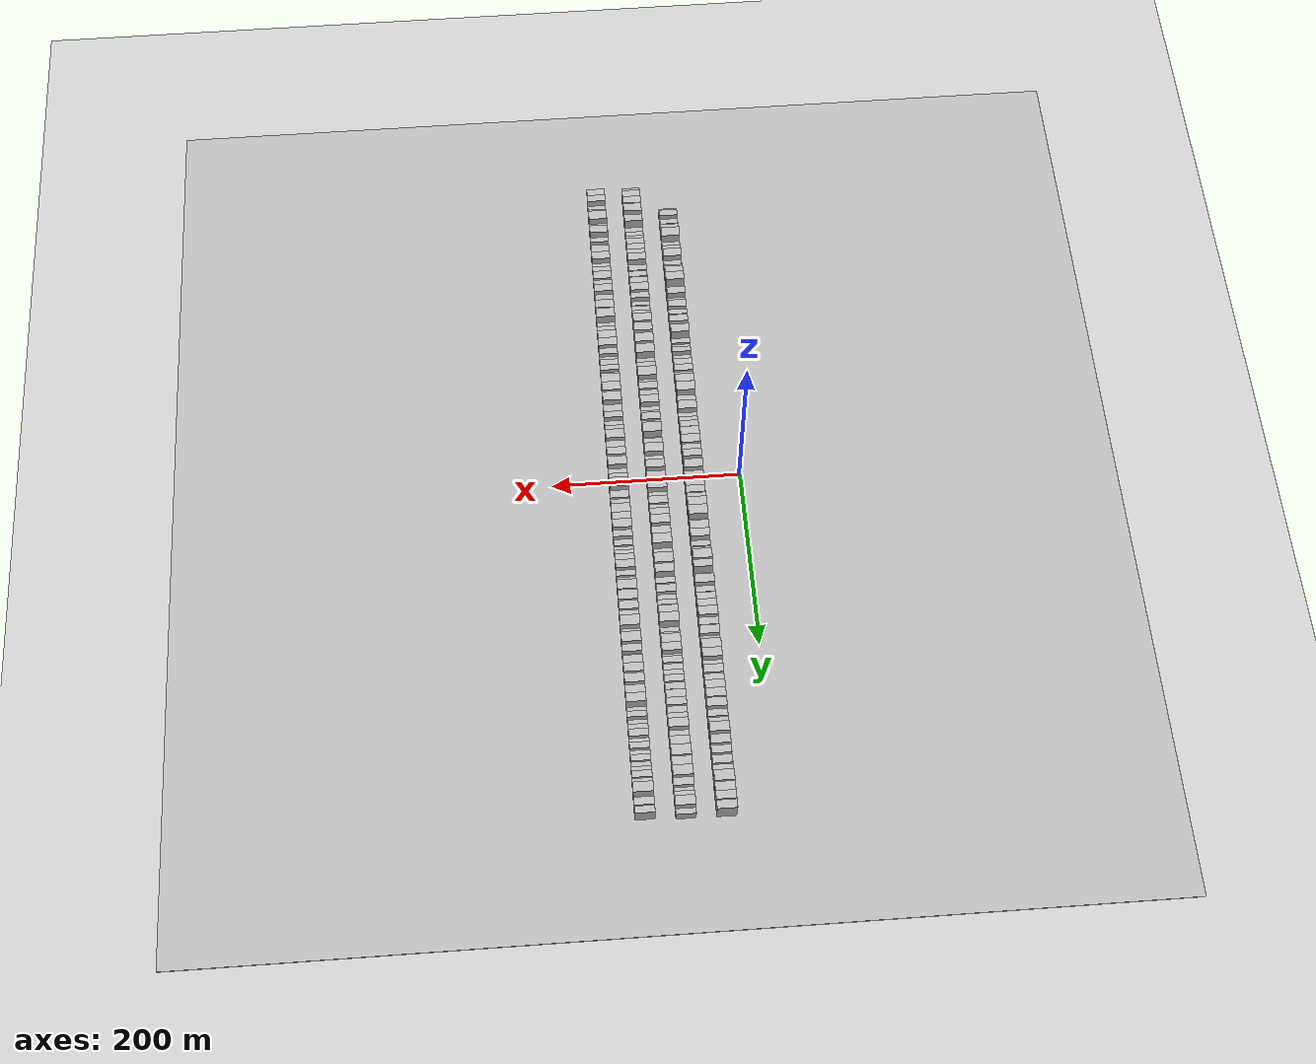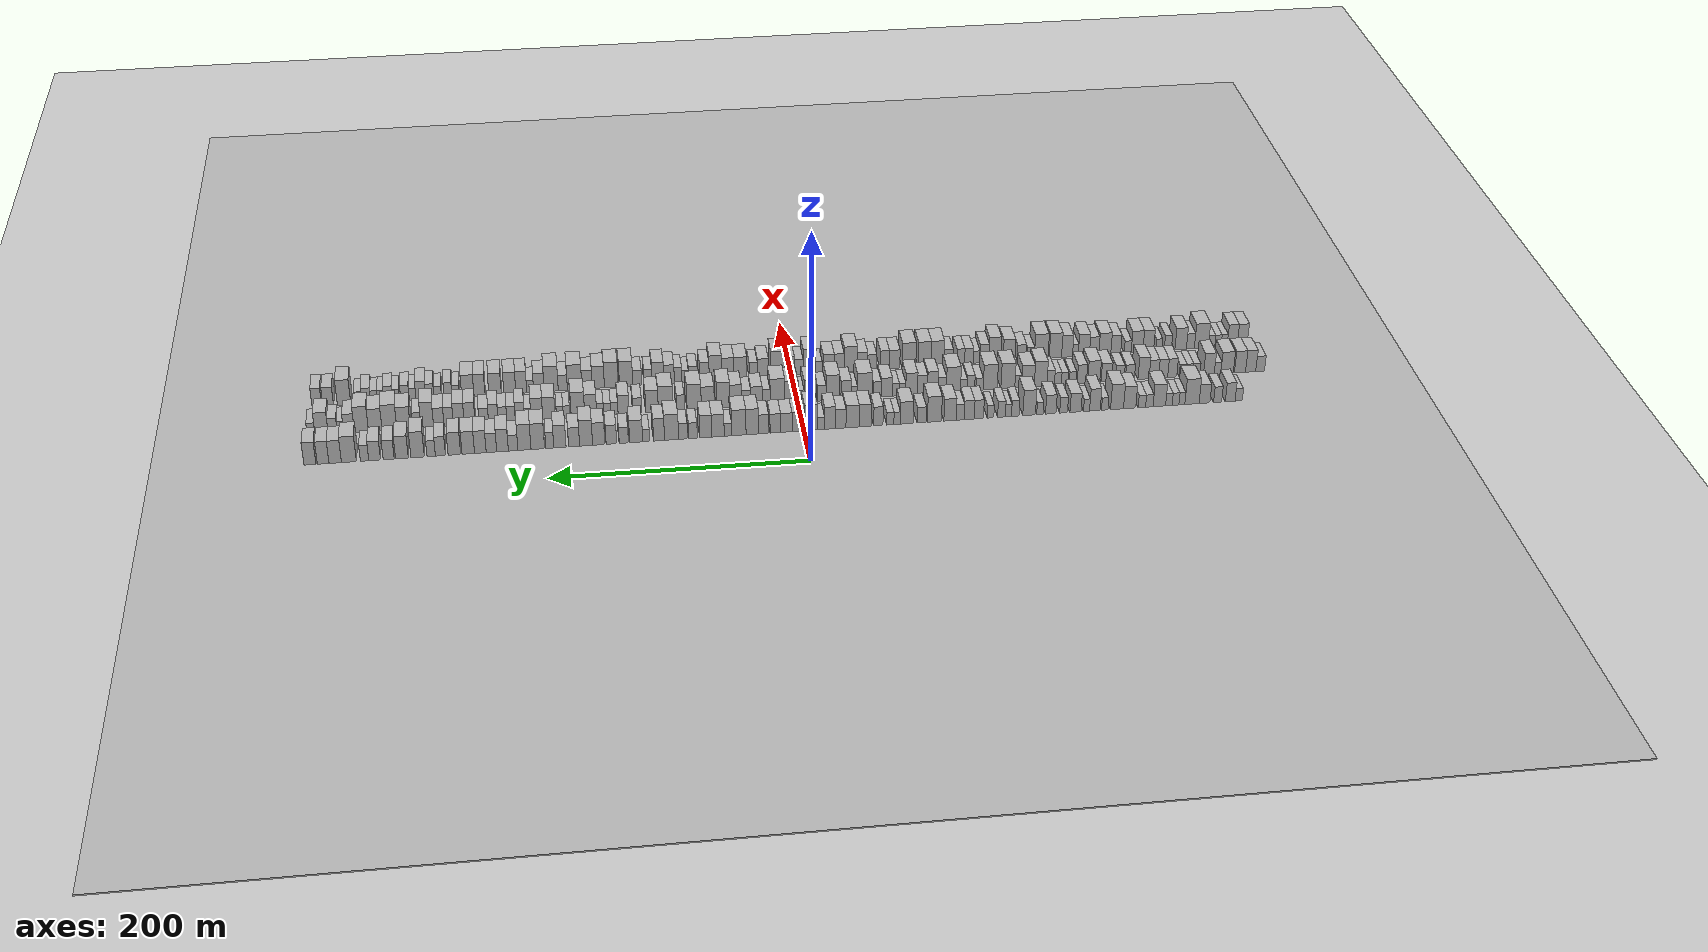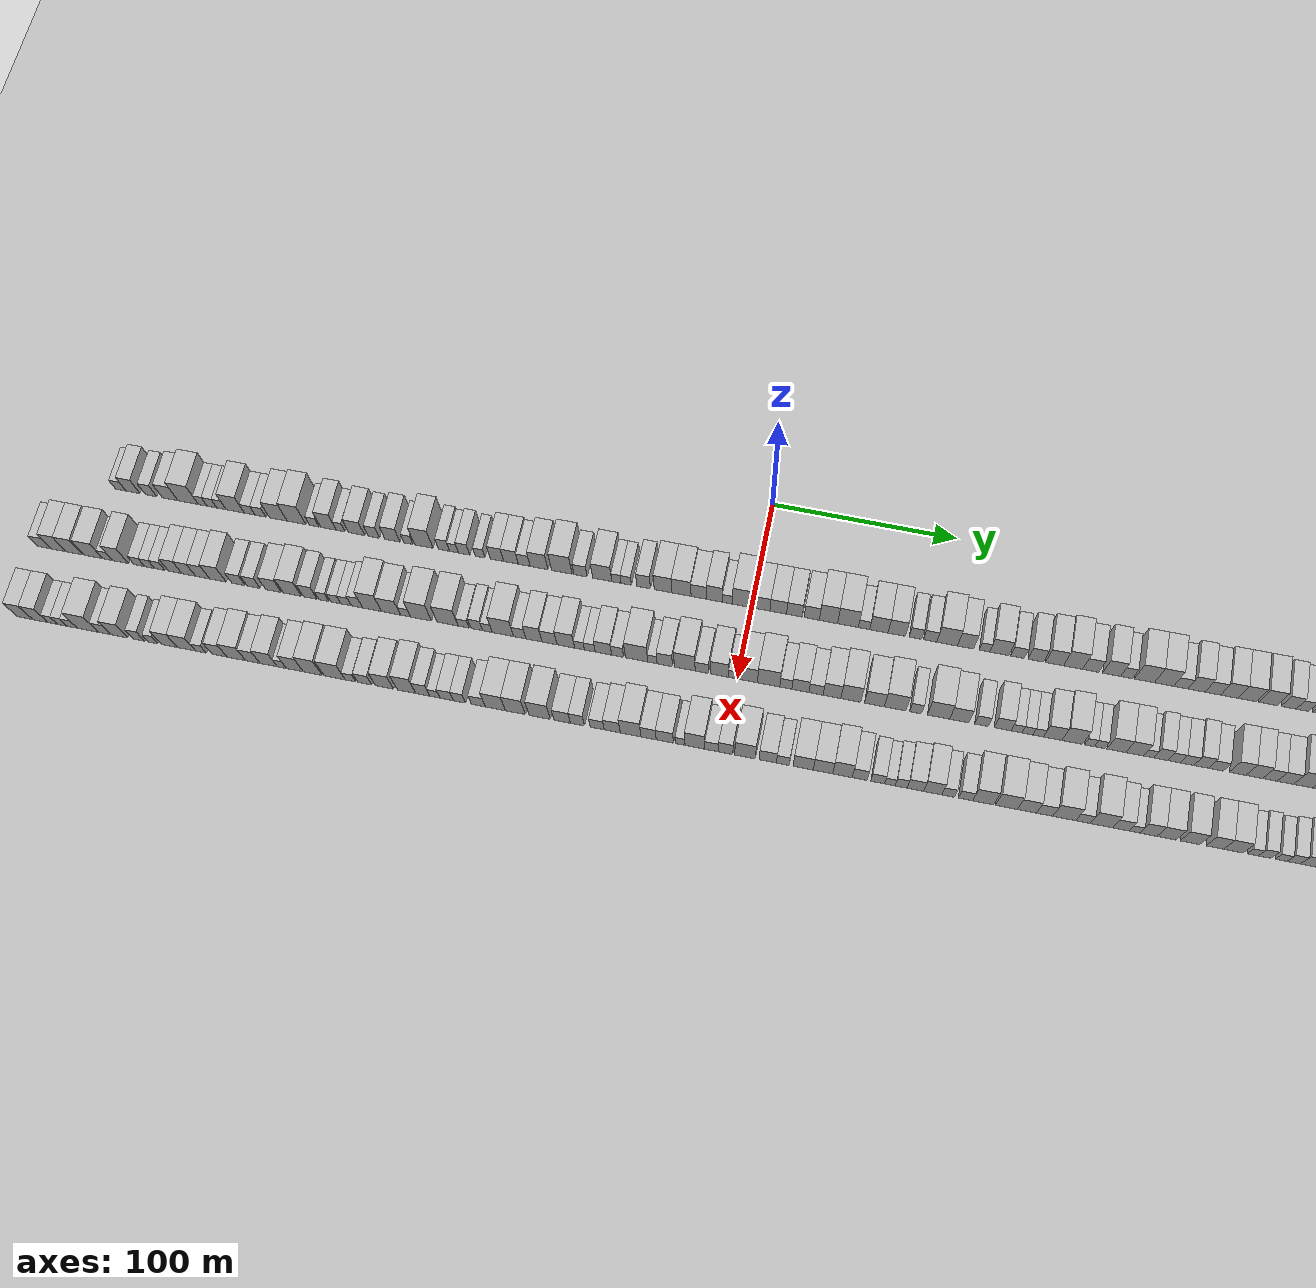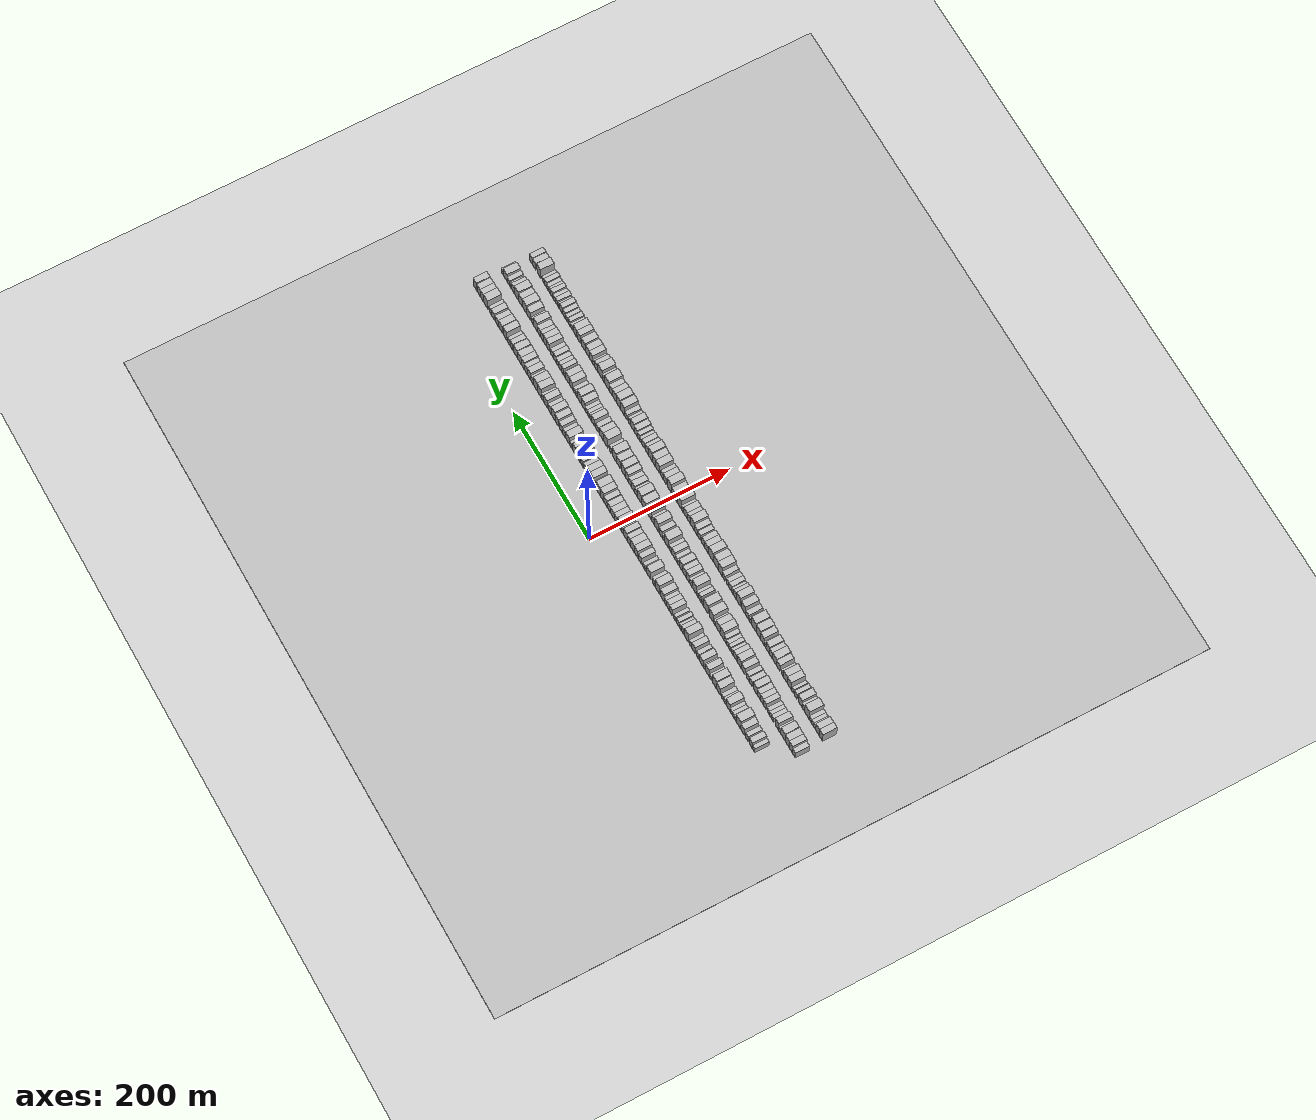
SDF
<?xml version="1.0" encoding="utf-8"?>

<sdf version="1.6">

   <world name="default">

      <gui fullscreen="0">

         <camera name="user_camera">

            <pose>-15 0 4.57585 0 0 0</pose>

            <view_controller>orbit</view_controller>

         </camera>

      </gui>

      <scene>

         <sky>

           <clouds>

             <speed>12</speed>

           </clouds>

         </sky>

         <ambient>0.4 0.4 0.4 1</ambient>

         <background>0.7 0.7 0.7 1</background>

         <shadows>1</shadows>

      </scene>

      <gravity>0 0 -9.8066</gravity>

      <magnetic_field>6e-06 2.3e-05 -4.2e-05</magnetic_field>

      <physics default="0" name="default_physics" type="ode">

         <ode>

            <solver>

               <type>quick</type>

               <iters>10</iters>

               <sor>1.0</sor>

               <use_dynamic_moi_rescaling>0</use_dynamic_moi_rescaling>

            </solver>

            <constraints>

               <cfm>0</cfm>

               <erp>0.2</erp>

               <contact_max_correcting_vel>100</contact_max_correcting_vel>

               <contact_surface_layer>0.001</contact_surface_layer>

            </constraints>

         </ode>

         <max_step_size>0.004</max_step_size>

         <real_time_factor>1</real_time_factor>

         <real_time_update_rate>250</real_time_update_rate>

      </physics>

      <light name="sun" type="directional">

         <cast_shadows>1</cast_shadows>

         <pose>0 0 10 0 0 0</pose>

         <diffuse>0.8 0.8 0.8 1</diffuse>

         <specular>0.2 0.2 0.2 1</specular>

         <attenuation>

            <range>1000</range>

            <constant>0.9</constant>

            <linear>0.01</linear>

            <quadratic>0.001</quadratic>

         </attenuation>

         <direction>-0.5 0.1 -0.9</direction>

      </light>

      <include>

         <name>ground_plane_1</name>

         <uri>model://HANNAS_ground_plane</uri>

         <pose>0 0 0  0 0 0</pose>

      </include>

      <include>

         <name>ground_plane_2</name>

         <uri>model://HANNAS_ground_plane</uri>

         <pose>100 0 0  0 0 0</pose>

      </include>

      <model name="building_1">

         <static>1</static>

         <pose frame="">50.0000 -347.2101 0 0.000000 0.000000 0.000000</pose>

         <link name="link">

            <pose frame="">0 0 6.00 0 0 0</pose>

            <collision name="collision">

               <geometry>

                  <box>

                     <size>20.0000 5.8599 12.0000</size>

                  </box>

               </geometry>

               <max_contacts>10</max_contacts>

               <surface>

                  <contact>

                     <ode/>

                  </contact>

                  <bounce/>

                  <friction>

                     <torsional>

                        <ode/>

                     </torsional>

                     <ode/>

                  </friction>

               </surface>

            </collision>

            <visual name="visual">

               <cast_shadows>0</cast_shadows>

               <geometry>

                  <box>

                     <size>20.0000 5.8599 12.0000</size>

                  </box>

               </geometry>

               <material>

                  <script>

                     <uri>model://HANNAS_wall/materials/scripts</uri>

                     <uri>model://HANNAS_wall/materials/textures</uri>

                     <name>vrc/HANNAS_wall</name>

                  </script>

               </material>

            </visual>

            <self_collide>0</self_collide>

            <enable_wind>0</enable_wind>

            <kinematic>0</kinematic>

         </link>

      </model>

      <model name="building_2">

         <static>1</static>

         <pose frame="">50.0000 -340.2969 0 0.000000 0.000000 0.000000</pose>

         <link name="link">

            <pose frame="">0 0 9.00 0 0 0</pose>

            <collision name="collision">

               <geometry>

                  <box>

                     <size>20.0000 7.9666 18.0000</size>

                  </box>

               </geometry>

               <max_contacts>10</max_contacts>

               <surface>

                  <contact>

                     <ode/>

                  </contact>

                  <bounce/>

                  <friction>

                     <torsional>

                        <ode/>

                     </torsional>

                     <ode/>

                  </friction>

               </surface>

            </collision>

            <visual name="visual">

               <cast_shadows>0</cast_shadows>

               <geometry>

                  <box>

                     <size>20.0000 7.9666 18.0000</size>

                  </box>

               </geometry>

               <material>

                  <script>

                     <uri>model://HANNAS_wall/materials/scripts</uri>

                     <uri>model://HANNAS_wall/materials/textures</uri>

                     <name>vrc/HANNAS_wall</name>

                  </script>

               </material>

            </visual>

            <self_collide>0</self_collide>

            <enable_wind>0</enable_wind>

            <kinematic>0</kinematic>

         </link>

      </model>

      <model name="building_3">

         <static>1</static>

         <pose frame="">50.0000 -330.0451 0 0.000000 0.000000 0.000000</pose>

         <link name="link">

            <pose frame="">0 0 7.50 0 0 0</pose>

            <collision name="collision">

               <geometry>

                  <box>

                     <size>20.0000 6.5369 15.0000</size>

                  </box>

               </geometry>

               <max_contacts>10</max_contacts>

               <surface>

                  <contact>

                     <ode/>

                  </contact>

                  <bounce/>

                  <friction>

                     <torsional>

                        <ode/>

                     </torsional>

                     <ode/>

                  </friction>

               </surface>

            </collision>

            <visual name="visual">

               <cast_shadows>0</cast_shadows>

               <geometry>

                  <box>

                     <size>20.0000 6.5369 15.0000</size>

                  </box>

               </geometry>

               <material>

                  <script>

                     <uri>model://HANNAS_wall/materials/scripts</uri>

                     <uri>model://HANNAS_wall/materials/textures</uri>

                     <name>vrc/HANNAS_wall</name>

                  </script>

               </material>

            </visual>

            <self_collide>0</self_collide>

            <enable_wind>0</enable_wind>

            <kinematic>0</kinematic>

         </link>

      </model>

      <model name="building_4">

         <static>1</static>

         <pose frame="">50.0000 -319.3938 0 0.000000 0.000000 0.000000</pose>

         <link name="link">

            <pose frame="">0 0 9.00 0 0 0</pose>

            <collision name="collision">

               <geometry>

                  <box>

                     <size>20.0000 8.7658 18.0000</size>

                  </box>

               </geometry>

               <max_contacts>10</max_contacts>

               <surface>

                  <contact>

                     <ode/>

                  </contact>

                  <bounce/>

                  <friction>

                     <torsional>

                        <ode/>

                     </torsional>

                     <ode/>

                  </friction>

               </surface>

            </collision>

            <visual name="visual">

               <cast_shadows>0</cast_shadows>

               <geometry>

                  <box>

                     <size>20.0000 8.7658 18.0000</size>

                  </box>

               </geometry>

               <material>

                  <script>

                     <uri>model://HANNAS_wall/materials/scripts</uri>

                     <uri>model://HANNAS_wall/materials/textures</uri>

                     <name>vrc/HANNAS_wall</name>

                  </script>

               </material>

            </visual>

            <self_collide>0</self_collide>

            <enable_wind>0</enable_wind>

            <kinematic>0</kinematic>

         </link>

      </model>

      <model name="building_5">

         <static>1</static>

         <pose frame="">50.0000 -309.2314 0 0.000000 0.000000 0.000000</pose>

         <link name="link">

            <pose frame="">0 0 12.00 0 0 0</pose>

            <collision name="collision">

               <geometry>

                  <box>

                     <size>20.0000 11.5589 24.0000</size>

                  </box>

               </geometry>

               <max_contacts>10</max_contacts>

               <surface>

                  <contact>

                     <ode/>

                  </contact>

                  <bounce/>

                  <friction>

                     <torsional>

                        <ode/>

                     </torsional>

                     <ode/>

                  </friction>

               </surface>

            </collision>

            <visual name="visual">

               <cast_shadows>0</cast_shadows>

               <geometry>

                  <box>

                     <size>20.0000 11.5589 24.0000</size>

                  </box>

               </geometry>

               <material>

                  <script>

                     <uri>model://HANNAS_wall/materials/scripts</uri>

                     <uri>model://HANNAS_wall/materials/textures</uri>

                     <name>vrc/HANNAS_wall</name>

                  </script>

               </material>

            </visual>

            <self_collide>0</self_collide>

            <enable_wind>0</enable_wind>

            <kinematic>0</kinematic>

         </link>

      </model>

      <model name="building_6">

         <static>1</static>

         <pose frame="">50.0000 -301.0503 0 0.000000 0.000000 0.000000</pose>

         <link name="link">

            <pose frame="">0 0 6.00 0 0 0</pose>

            <collision name="collision">

               <geometry>

                  <box>

                     <size>20.0000 4.8033 12.0000</size>

                  </box>

               </geometry>

               <max_contacts>10</max_contacts>

               <surface>

                  <contact>

                     <ode/>

                  </contact>

                  <bounce/>

                  <friction>

                     <torsional>

                        <ode/>

                     </torsional>

                     <ode/>

                  </friction>

               </surface>

            </collision>

            <visual name="visual">

               <cast_shadows>0</cast_shadows>

               <geometry>

                  <box>

                     <size>20.0000 4.8033 12.0000</size>

                  </box>

               </geometry>

               <material>

                  <script>

                     <uri>model://HANNAS_wall/materials/scripts</uri>

                     <uri>model://HANNAS_wall/materials/textures</uri>

                     <name>vrc/HANNAS_wall</name>

                  </script>

               </material>

            </visual>

            <self_collide>0</self_collide>

            <enable_wind>0</enable_wind>

            <kinematic>0</kinematic>

         </link>

      </model>

      <model name="building_7">

         <static>1</static>

         <pose frame="">50.0000 -295.8936 0 0.000000 0.000000 0.000000</pose>

         <link name="link">

            <pose frame="">0 0 6.00 0 0 0</pose>

            <collision name="collision">

               <geometry>

                  <box>

                     <size>20.0000 5.5101 12.0000</size>

                  </box>

               </geometry>

               <max_contacts>10</max_contacts>

               <surface>

                  <contact>

                     <ode/>

                  </contact>

                  <bounce/>

                  <friction>

                     <torsional>

                        <ode/>

                     </torsional>

                     <ode/>

                  </friction>

               </surface>

            </collision>

            <visual name="visual">

               <cast_shadows>0</cast_shadows>

               <geometry>

                  <box>

                     <size>20.0000 5.5101 12.0000</size>

                  </box>

               </geometry>

               <material>

                  <script>

                     <uri>model://HANNAS_wall/materials/scripts</uri>

                     <uri>model://HANNAS_wall/materials/textures</uri>

                     <name>vrc/HANNAS_wall</name>

                  </script>

               </material>

            </visual>

            <self_collide>0</self_collide>

            <enable_wind>0</enable_wind>

            <kinematic>0</kinematic>

         </link>

      </model>

      <model name="building_8">

         <static>1</static>

         <pose frame="">50.0000 -290.5220 0 0.000000 0.000000 0.000000</pose>

         <link name="link">

            <pose frame="">0 0 6.00 0 0 0</pose>

            <collision name="collision">

               <geometry>

                  <box>

                     <size>20.0000 5.2332 12.0000</size>

                  </box>

               </geometry>

               <max_contacts>10</max_contacts>

               <surface>

                  <contact>

                     <ode/>

                  </contact>

                  <bounce/>

                  <friction>

                     <torsional>

                        <ode/>

                     </torsional>

                     <ode/>

                  </friction>

               </surface>

            </collision>

            <visual name="visual">

               <cast_shadows>0</cast_shadows>

               <geometry>

                  <box>

                     <size>20.0000 5.2332 12.0000</size>

                  </box>

               </geometry>

               <material>

                  <script>

                     <uri>model://HANNAS_wall/materials/scripts</uri>

                     <uri>model://HANNAS_wall/materials/textures</uri>

                     <name>vrc/HANNAS_wall</name>

                  </script>

               </material>

            </visual>

            <self_collide>0</self_collide>

            <enable_wind>0</enable_wind>

            <kinematic>0</kinematic>

         </link>

      </model>

      <model name="building_9">

         <static>1</static>

         <pose frame="">50.0000 -282.7947 0 0.000000 0.000000 0.000000</pose>

         <link name="link">

            <pose frame="">0 0 10.50 0 0 0</pose>

            <collision name="collision">

               <geometry>

                  <box>

                     <size>20.0000 10.2213 21.0000</size>

                  </box>

               </geometry>

               <max_contacts>10</max_contacts>

               <surface>

                  <contact>

                     <ode/>

                  </contact>

                  <bounce/>

                  <friction>

                     <torsional>

                        <ode/>

                     </torsional>

                     <ode/>

                  </friction>

               </surface>

            </collision>

            <visual name="visual">

               <cast_shadows>0</cast_shadows>

               <geometry>

                  <box>

                     <size>20.0000 10.2213 21.0000</size>

                  </box>

               </geometry>

               <material>

                  <script>

                     <uri>model://HANNAS_wall/materials/scripts</uri>

                     <uri>model://HANNAS_wall/materials/textures</uri>

                     <name>vrc/HANNAS_wall</name>

                  </script>

               </material>

            </visual>

            <self_collide>0</self_collide>

            <enable_wind>0</enable_wind>

            <kinematic>0</kinematic>

         </link>

      </model>

      <model name="building_10">

         <static>1</static>

         <pose frame="">50.0000 -274.6927 0 0.000000 0.000000 0.000000</pose>

         <link name="link">

            <pose frame="">0 0 6.00 0 0 0</pose>

            <collision name="collision">

               <geometry>

                  <box>

                     <size>20.0000 5.9826 12.0000</size>

                  </box>

               </geometry>

               <max_contacts>10</max_contacts>

               <surface>

                  <contact>

                     <ode/>

                  </contact>

                  <bounce/>

                  <friction>

                     <torsional>

                        <ode/>

                     </torsional>

                     <ode/>

                  </friction>

               </surface>

            </collision>

            <visual name="visual">

               <cast_shadows>0</cast_shadows>

               <geometry>

                  <box>

                     <size>20.0000 5.9826 12.0000</size>

                  </box>

               </geometry>

               <material>

                  <script>

                     <uri>model://HANNAS_wall/materials/scripts</uri>

                     <uri>model://HANNAS_wall/materials/textures</uri>

                     <name>vrc/HANNAS_wall</name>

                  </script>

               </material>

            </visual>

            <self_collide>0</self_collide>

            <enable_wind>0</enable_wind>

            <kinematic>0</kinematic>

         </link>

      </model>

      <model name="building_11">

         <static>1</static>

         <pose frame="">50.0000 -268.7035 0 0.000000 0.000000 0.000000</pose>

         <link name="link">

            <pose frame="">0 0 6.00 0 0 0</pose>

            <collision name="collision">

               <geometry>

                  <box>

                     <size>20.0000 5.9959 12.0000</size>

                  </box>

               </geometry>

               <max_contacts>10</max_contacts>

               <surface>

                  <contact>

                     <ode/>

                  </contact>

                  <bounce/>

                  <friction>

                     <torsional>

                        <ode/>

                     </torsional>

                     <ode/>

                  </friction>

               </surface>

            </collision>

            <visual name="visual">

               <cast_shadows>0</cast_shadows>

               <geometry>

                  <box>

                     <size>20.0000 5.9959 12.0000</size>

                  </box>

               </geometry>

               <material>

                  <script>

                     <uri>model://HANNAS_wall/materials/scripts</uri>

                     <uri>model://HANNAS_wall/materials/textures</uri>

                     <name>vrc/HANNAS_wall</name>

                  </script>

               </material>

            </visual>

            <self_collide>0</self_collide>

            <enable_wind>0</enable_wind>

            <kinematic>0</kinematic>

         </link>

      </model>

      <model name="building_12">

         <static>1</static>

         <pose frame="">50.0000 -258.7774 0 0.000000 0.000000 0.000000</pose>

         <link name="link">

            <pose frame="">0 0 10.50 0 0 0</pose>

            <collision name="collision">

               <geometry>

                  <box>

                     <size>20.0000 9.8562 21.0000</size>

                  </box>

               </geometry>

               <max_contacts>10</max_contacts>

               <surface>

                  <contact>

                     <ode/>

                  </contact>

                  <bounce/>

                  <friction>

                     <torsional>

                        <ode/>

                     </torsional>

                     <ode/>

                  </friction>

               </surface>

            </collision>

            <visual name="visual">

               <cast_shadows>0</cast_shadows>

               <geometry>

                  <box>

                     <size>20.0000 9.8562 21.0000</size>

                  </box>

               </geometry>

               <material>

                  <script>

                     <uri>model://HANNAS_wall/materials/scripts</uri>

                     <uri>model://HANNAS_wall/materials/textures</uri>

                     <name>vrc/HANNAS_wall</name>

                  </script>

               </material>

            </visual>

            <self_collide>0</self_collide>

            <enable_wind>0</enable_wind>

            <kinematic>0</kinematic>

         </link>

      </model>

      <model name="building_13">

         <static>1</static>

         <pose frame="">50.0000 -248.6221 0 0.000000 0.000000 0.000000</pose>

         <link name="link">

            <pose frame="">0 0 12.00 0 0 0</pose>

            <collision name="collision">

               <geometry>

                  <box>

                     <size>20.0000 10.4544 24.0000</size>

                  </box>

               </geometry>

               <max_contacts>10</max_contacts>

               <surface>

                  <contact>

                     <ode/>

                  </contact>

                  <bounce/>

                  <friction>

                     <torsional>

                        <ode/>

                     </torsional>

                     <ode/>

                  </friction>

               </surface>

            </collision>

            <visual name="visual">

               <cast_shadows>0</cast_shadows>

               <geometry>

                  <box>

                     <size>20.0000 10.4544 24.0000</size>

                  </box>

               </geometry>

               <material>

                  <script>

                     <uri>model://HANNAS_wall/materials/scripts</uri>

                     <uri>model://HANNAS_wall/materials/textures</uri>

                     <name>vrc/HANNAS_wall</name>

                  </script>

               </material>

            </visual>

            <self_collide>0</self_collide>

            <enable_wind>0</enable_wind>

            <kinematic>0</kinematic>

         </link>

      </model>

      <model name="building_14">

         <static>1</static>

         <pose frame="">50.0000 -238.7557 0 0.000000 0.000000 0.000000</pose>

         <link name="link">

            <pose frame="">0 0 6.00 0 0 0</pose>

            <collision name="collision">

               <geometry>

                  <box>

                     <size>20.0000 5.2784 12.0000</size>

                  </box>

               </geometry>

               <max_contacts>10</max_contacts>

               <surface>

                  <contact>

                     <ode/>

                  </contact>

                  <bounce/>

                  <friction>

                     <torsional>

                        <ode/>

                     </torsional>

                     <ode/>

                  </friction>

               </surface>

            </collision>

            <visual name="visual">

               <cast_shadows>0</cast_shadows>

               <geometry>

                  <box>

                     <size>20.0000 5.2784 12.0000</size>

                  </box>

               </geometry>

               <material>

                  <script>

                     <uri>model://HANNAS_wall/materials/scripts</uri>

                     <uri>model://HANNAS_wall/materials/textures</uri>

                     <name>vrc/HANNAS_wall</name>

                  </script>

               </material>

            </visual>

            <self_collide>0</self_collide>

            <enable_wind>0</enable_wind>

            <kinematic>0</kinematic>

         </link>

      </model>

      <model name="building_15">

         <static>1</static>

         <pose frame="">50.0000 -230.8224 0 0.000000 0.000000 0.000000</pose>

         <link name="link">

            <pose frame="">0 0 10.50 0 0 0</pose>

            <collision name="collision">

               <geometry>

                  <box>

                     <size>20.0000 8.5884 21.0000</size>

                  </box>

               </geometry>

               <max_contacts>10</max_contacts>

               <surface>

                  <contact>

                     <ode/>

                  </contact>

                  <bounce/>

                  <friction>

                     <torsional>

                        <ode/>

                     </torsional>

                     <ode/>

                  </friction>

               </surface>

            </collision>

            <visual name="visual">

               <cast_shadows>0</cast_shadows>

               <geometry>

                  <box>

                     <size>20.0000 8.5884 21.0000</size>

                  </box>

               </geometry>

               <material>

                  <script>

                     <uri>model://HANNAS_wall/materials/scripts</uri>

                     <uri>model://HANNAS_wall/materials/textures</uri>

                     <name>vrc/HANNAS_wall</name>

                  </script>

               </material>

            </visual>

            <self_collide>0</self_collide>

            <enable_wind>0</enable_wind>

            <kinematic>0</kinematic>

         </link>

      </model>

      <model name="building_16">

         <static>1</static>

         <pose frame="">50.0000 -224.1120 0 0.000000 0.000000 0.000000</pose>

         <link name="link">

            <pose frame="">0 0 6.00 0 0 0</pose>

            <collision name="collision">

               <geometry>

                  <box>

                     <size>20.0000 4.8323 12.0000</size>

                  </box>

               </geometry>

               <max_contacts>10</max_contacts>

               <surface>

                  <contact>

                     <ode/>

                  </contact>

                  <bounce/>

                  <friction>

                     <torsional>

                        <ode/>

                     </torsional>

                     <ode/>

                  </friction>

               </surface>

            </collision>

            <visual name="visual">

               <cast_shadows>0</cast_shadows>

               <geometry>

                  <box>

                     <size>20.0000 4.8323 12.0000</size>

                  </box>

               </geometry>

               <material>

                  <script>

                     <uri>model://HANNAS_wall/materials/scripts</uri>

                     <uri>model://HANNAS_wall/materials/textures</uri>

                     <name>vrc/HANNAS_wall</name>

                  </script>

               </material>

            </visual>

            <self_collide>0</self_collide>

            <enable_wind>0</enable_wind>

            <kinematic>0</kinematic>

         </link>

      </model>

      <model name="building_17">

         <static>1</static>

         <pose frame="">50.0000 -215.2455 0 0.000000 0.000000 0.000000</pose>

         <link name="link">

            <pose frame="">0 0 9.00 0 0 0</pose>

            <collision name="collision">

               <geometry>

                  <box>

                     <size>20.0000 8.9008 18.0000</size>

                  </box>

               </geometry>

               <max_contacts>10</max_contacts>

               <surface>

                  <contact>

                     <ode/>

                  </contact>

                  <bounce/>

                  <friction>

                     <torsional>

                        <ode/>

                     </torsional>

                     <ode/>

                  </friction>

               </surface>

            </collision>

            <visual name="visual">

               <cast_shadows>0</cast_shadows>

               <geometry>

                  <box>

                     <size>20.0000 8.9008 18.0000</size>

                  </box>

               </geometry>

               <material>

                  <script>

                     <uri>model://HANNAS_wall/materials/scripts</uri>

                     <uri>model://HANNAS_wall/materials/textures</uri>

                     <name>vrc/HANNAS_wall</name>

                  </script>

               </material>

            </visual>

            <self_collide>0</self_collide>

            <enable_wind>0</enable_wind>

            <kinematic>0</kinematic>

         </link>

      </model>

      <model name="building_18">

         <static>1</static>

         <pose frame="">50.0000 -205.6938 0 0.000000 0.000000 0.000000</pose>

         <link name="link">

            <pose frame="">0 0 7.50 0 0 0</pose>

            <collision name="collision">

               <geometry>

                  <box>

                     <size>20.0000 6.2026 15.0000</size>

                  </box>

               </geometry>

               <max_contacts>10</max_contacts>

               <surface>

                  <contact>

                     <ode/>

                  </contact>

                  <bounce/>

                  <friction>

                     <torsional>

                        <ode/>

                     </torsional>

                     <ode/>

                  </friction>

               </surface>

            </collision>

            <visual name="visual">

               <cast_shadows>0</cast_shadows>

               <geometry>

                  <box>

                     <size>20.0000 6.2026 15.0000</size>

                  </box>

               </geometry>

               <material>

                  <script>

                     <uri>model://HANNAS_wall/materials/scripts</uri>

                     <uri>model://HANNAS_wall/materials/textures</uri>

                     <name>vrc/HANNAS_wall</name>

                  </script>

               </material>

            </visual>

            <self_collide>0</self_collide>

            <enable_wind>0</enable_wind>

            <kinematic>0</kinematic>

         </link>

      </model>

      <model name="building_19">

         <static>1</static>

         <pose frame="">50.0000 -195.4031 0 0.000000 0.000000 0.000000</pose>

         <link name="link">

            <pose frame="">0 0 9.00 0 0 0</pose>

            <collision name="collision">

               <geometry>

                  <box>

                     <size>20.0000 8.3786 18.0000</size>

                  </box>

               </geometry>

               <max_contacts>10</max_contacts>

               <surface>

                  <contact>

                     <ode/>

                  </contact>

                  <bounce/>

                  <friction>

                     <torsional>

                        <ode/>

                     </torsional>

                     <ode/>

                  </friction>

               </surface>

            </collision>

            <visual name="visual">

               <cast_shadows>0</cast_shadows>

               <geometry>

                  <box>

                     <size>20.0000 8.3786 18.0000</size>

                  </box>

               </geometry>

               <material>

                  <script>

                     <uri>model://HANNAS_wall/materials/scripts</uri>

                     <uri>model://HANNAS_wall/materials/textures</uri>

                     <name>vrc/HANNAS_wall</name>

                  </script>

               </material>

            </visual>

            <self_collide>0</self_collide>

            <enable_wind>0</enable_wind>

            <kinematic>0</kinematic>

         </link>

      </model>

      <model name="building_20">

         <static>1</static>

         <pose frame="">50.0000 -186.6804 0 0.000000 0.000000 0.000000</pose>

         <link name="link">

            <pose frame="">0 0 6.00 0 0 0</pose>

            <collision name="collision">

               <geometry>

                  <box>

                     <size>20.0000 5.0669 12.0000</size>

                  </box>

               </geometry>

               <max_contacts>10</max_contacts>

               <surface>

                  <contact>

                     <ode/>

                  </contact>

                  <bounce/>

                  <friction>

                     <torsional>

                        <ode/>

                     </torsional>

                     <ode/>

                  </friction>

               </surface>

            </collision>

            <visual name="visual">

               <cast_shadows>0</cast_shadows>

               <geometry>

                  <box>

                     <size>20.0000 5.0669 12.0000</size>

                  </box>

               </geometry>

               <material>

                  <script>

                     <uri>model://HANNAS_wall/materials/scripts</uri>

                     <uri>model://HANNAS_wall/materials/textures</uri>

                     <name>vrc/HANNAS_wall</name>

                  </script>

               </material>

            </visual>

            <self_collide>0</self_collide>

            <enable_wind>0</enable_wind>

            <kinematic>0</kinematic>

         </link>

      </model>

      <model name="building_21">

         <static>1</static>

         <pose frame="">50.0000 -178.0910 0 0.000000 0.000000 0.000000</pose>

         <link name="link">

            <pose frame="">0 0 12.00 0 0 0</pose>

            <collision name="collision">

               <geometry>

                  <box>

                     <size>20.0000 10.1119 24.0000</size>

                  </box>

               </geometry>

               <max_contacts>10</max_contacts>

               <surface>

                  <contact>

                     <ode/>

                  </contact>

                  <bounce/>

                  <friction>

                     <torsional>

                        <ode/>

                     </torsional>

                     <ode/>

                  </friction>

               </surface>

            </collision>

            <visual name="visual">

               <cast_shadows>0</cast_shadows>

               <geometry>

                  <box>

                     <size>20.0000 10.1119 24.0000</size>

                  </box>

               </geometry>

               <material>

                  <script>

                     <uri>model://HANNAS_wall/materials/scripts</uri>

                     <uri>model://HANNAS_wall/materials/textures</uri>

                     <name>vrc/HANNAS_wall</name>

                  </script>

               </material>

            </visual>

            <self_collide>0</self_collide>

            <enable_wind>0</enable_wind>

            <kinematic>0</kinematic>

         </link>

      </model>

      <model name="building_22">

         <static>1</static>

         <pose frame="">50.0000 -166.9902 0 0.000000 0.000000 0.000000</pose>

         <link name="link">

            <pose frame="">0 0 7.50 0 0 0</pose>

            <collision name="collision">

               <geometry>

                  <box>

                     <size>20.0000 6.0898 15.0000</size>

                  </box>

               </geometry>

               <max_contacts>10</max_contacts>

               <surface>

                  <contact>

                     <ode/>

                  </contact>

                  <bounce/>

                  <friction>

                     <torsional>

                        <ode/>

                     </torsional>

                     <ode/>

                  </friction>

               </surface>

            </collision>

            <visual name="visual">

               <cast_shadows>0</cast_shadows>

               <geometry>

                  <box>

                     <size>20.0000 6.0898 15.0000</size>

                  </box>

               </geometry>

               <material>

                  <script>

                     <uri>model://HANNAS_wall/materials/scripts</uri>

                     <uri>model://HANNAS_wall/materials/textures</uri>

                     <name>vrc/HANNAS_wall</name>

                  </script>

               </material>

            </visual>

            <self_collide>0</self_collide>

            <enable_wind>0</enable_wind>

            <kinematic>0</kinematic>

         </link>

      </model>

      <model name="building_23">

         <static>1</static>

         <pose frame="">50.0000 -161.5102 0 0.000000 0.000000 0.000000</pose>

         <link name="link">

            <pose frame="">0 0 6.00 0 0 0</pose>

            <collision name="collision">

               <geometry>

                  <box>

                     <size>20.0000 4.8701 12.0000</size>

                  </box>

               </geometry>

               <max_contacts>10</max_contacts>

               <surface>

                  <contact>

                     <ode/>

                  </contact>

                  <bounce/>

                  <friction>

                     <torsional>

                        <ode/>

                     </torsional>

                     <ode/>

                  </friction>

               </surface>

            </collision>

            <visual name="visual">

               <cast_shadows>0</cast_shadows>

               <geometry>

                  <box>

                     <size>20.0000 4.8701 12.0000</size>

                  </box>

               </geometry>

               <material>

                  <script>

                     <uri>model://HANNAS_wall/materials/scripts</uri>

                     <uri>model://HANNAS_wall/materials/textures</uri>

                     <name>vrc/HANNAS_wall</name>

                  </script>

               </material>

            </visual>

            <self_collide>0</self_collide>

            <enable_wind>0</enable_wind>

            <kinematic>0</kinematic>

         </link>

      </model>

      <model name="building_24">

         <static>1</static>

         <pose frame="">50.0000 -155.9890 0 0.000000 0.000000 0.000000</pose>

         <link name="link">

            <pose frame="">0 0 7.50 0 0 0</pose>

            <collision name="collision">

               <geometry>

                  <box>

                     <size>20.0000 6.1724 15.0000</size>

                  </box>

               </geometry>

               <max_contacts>10</max_contacts>

               <surface>

                  <contact>

                     <ode/>

                  </contact>

                  <bounce/>

                  <friction>

                     <torsional>

                        <ode/>

                     </torsional>

                     <ode/>

                  </friction>

               </surface>

            </collision>

            <visual name="visual">

               <cast_shadows>0</cast_shadows>

               <geometry>

                  <box>

                     <size>20.0000 6.1724 15.0000</size>

                  </box>

               </geometry>

               <material>

                  <script>

                     <uri>model://HANNAS_wall/materials/scripts</uri>

                     <uri>model://HANNAS_wall/materials/textures</uri>

                     <name>vrc/HANNAS_wall</name>

                  </script>

               </material>

            </visual>

            <self_collide>0</self_collide>

            <enable_wind>0</enable_wind>

            <kinematic>0</kinematic>

         </link>

      </model>

      <model name="building_25">

         <static>1</static>

         <pose frame="">50.0000 -147.2446 0 0.000000 0.000000 0.000000</pose>

         <link name="link">

            <pose frame="">0 0 6.00 0 0 0</pose>

            <collision name="collision">

               <geometry>

                  <box>

                     <size>20.0000 5.3164 12.0000</size>

                  </box>

               </geometry>

               <max_contacts>10</max_contacts>

               <surface>

                  <contact>

                     <ode/>

                  </contact>

                  <bounce/>

                  <friction>

                     <torsional>

                        <ode/>

                     </torsional>

                     <ode/>

                  </friction>

               </surface>

            </collision>

            <visual name="visual">

               <cast_shadows>0</cast_shadows>

               <geometry>

                  <box>

                     <size>20.0000 5.3164 12.0000</size>

                  </box>

               </geometry>

               <material>

                  <script>

                     <uri>model://HANNAS_wall/materials/scripts</uri>

                     <uri>model://HANNAS_wall/materials/textures</uri>

                     <name>vrc/HANNAS_wall</name>

                  </script>

               </material>

            </visual>

            <self_collide>0</self_collide>

            <enable_wind>0</enable_wind>

            <kinematic>0</kinematic>

         </link>

      </model>

      <model name="building_26">

         <static>1</static>

         <pose frame="">50.0000 -137.9398 0 0.000000 0.000000 0.000000</pose>

         <link name="link">

            <pose frame="">0 0 9.00 0 0 0</pose>

            <collision name="collision">

               <geometry>

                  <box>

                     <size>20.0000 7.2933 18.0000</size>

                  </box>

               </geometry>

               <max_contacts>10</max_contacts>

               <surface>

                  <contact>

                     <ode/>

                  </contact>

                  <bounce/>

                  <friction>

                     <torsional>

                        <ode/>

                     </torsional>

                     <ode/>

                  </friction>

               </surface>

            </collision>

            <visual name="visual">

               <cast_shadows>0</cast_shadows>

               <geometry>

                  <box>

                     <size>20.0000 7.2933 18.0000</size>

                  </box>

               </geometry>

               <material>

                  <script>

                     <uri>model://HANNAS_wall/materials/scripts</uri>

                     <uri>model://HANNAS_wall/materials/textures</uri>

                     <name>vrc/HANNAS_wall</name>

                  </script>

               </material>

            </visual>

            <self_collide>0</self_collide>

            <enable_wind>0</enable_wind>

            <kinematic>0</kinematic>

         </link>

      </model>

      <model name="building_27">

         <static>1</static>

         <pose frame="">50.0000 -130.3020 0 0.000000 0.000000 0.000000</pose>

         <link name="link">

            <pose frame="">0 0 9.00 0 0 0</pose>

            <collision name="collision">

               <geometry>

                  <box>

                     <size>20.0000 7.9821 18.0000</size>

                  </box>

               </geometry>

               <max_contacts>10</max_contacts>

               <surface>

                  <contact>

                     <ode/>

                  </contact>

                  <bounce/>

                  <friction>

                     <torsional>

                        <ode/>

                     </torsional>

                     <ode/>

                  </friction>

               </surface>

            </collision>

            <visual name="visual">

               <cast_shadows>0</cast_shadows>

               <geometry>

                  <box>

                     <size>20.0000 7.9821 18.0000</size>

                  </box>

               </geometry>

               <material>

                  <script>

                     <uri>model://HANNAS_wall/materials/scripts</uri>

                     <uri>model://HANNAS_wall/materials/textures</uri>

                     <name>vrc/HANNAS_wall</name>

                  </script>

               </material>

            </visual>

            <self_collide>0</self_collide>

            <enable_wind>0</enable_wind>

            <kinematic>0</kinematic>

         </link>

      </model>

      <model name="building_28">

         <static>1</static>

         <pose frame="">50.0000 -123.0889 0 0.000000 0.000000 0.000000</pose>

         <link name="link">

            <pose frame="">0 0 7.50 0 0 0</pose>

            <collision name="collision">

               <geometry>

                  <box>

                     <size>20.0000 6.4442 15.0000</size>

                  </box>

               </geometry>

               <max_contacts>10</max_contacts>

               <surface>

                  <contact>

                     <ode/>

                  </contact>

                  <bounce/>

                  <friction>

                     <torsional>

                        <ode/>

                     </torsional>

                     <ode/>

                  </friction>

               </surface>

            </collision>

            <visual name="visual">

               <cast_shadows>0</cast_shadows>

               <geometry>

                  <box>

                     <size>20.0000 6.4442 15.0000</size>

                  </box>

               </geometry>

               <material>

                  <script>

                     <uri>model://HANNAS_wall/materials/scripts</uri>

                     <uri>model://HANNAS_wall/materials/textures</uri>

                     <name>vrc/HANNAS_wall</name>

                  </script>

               </material>

            </visual>

            <self_collide>0</self_collide>

            <enable_wind>0</enable_wind>

            <kinematic>0</kinematic>

         </link>

      </model>

      <model name="building_29">

         <static>1</static>

         <pose frame="">50.0000 -115.0239 0 0.000000 0.000000 0.000000</pose>

         <link name="link">

            <pose frame="">0 0 10.50 0 0 0</pose>

            <collision name="collision">

               <geometry>

                  <box>

                     <size>20.0000 9.6858 21.0000</size>

                  </box>

               </geometry>

               <max_contacts>10</max_contacts>

               <surface>

                  <contact>

                     <ode/>

                  </contact>

                  <bounce/>

                  <friction>

                     <torsional>

                        <ode/>

                     </torsional>

                     <ode/>

                  </friction>

               </surface>

            </collision>

            <visual name="visual">

               <cast_shadows>0</cast_shadows>

               <geometry>

                  <box>

                     <size>20.0000 9.6858 21.0000</size>

                  </box>

               </geometry>

               <material>

                  <script>

                     <uri>model://HANNAS_wall/materials/scripts</uri>

                     <uri>model://HANNAS_wall/materials/textures</uri>

                     <name>vrc/HANNAS_wall</name>

                  </script>

               </material>

            </visual>

            <self_collide>0</self_collide>

            <enable_wind>0</enable_wind>

            <kinematic>0</kinematic>

         </link>

      </model>

      <model name="building_30">

         <static>1</static>

         <pose frame="">50.0000 -102.6167 0 0.000000 0.000000 0.000000</pose>

         <link name="link">

            <pose frame="">0 0 12.00 0 0 0</pose>

            <collision name="collision">

               <geometry>

                  <box>

                     <size>20.0000 11.1286 24.0000</size>

                  </box>

               </geometry>

               <max_contacts>10</max_contacts>

               <surface>

                  <contact>

                     <ode/>

                  </contact>

                  <bounce/>

                  <friction>

                     <torsional>

                        <ode/>

                     </torsional>

                     <ode/>

                  </friction>

               </surface>

            </collision>

            <visual name="visual">

               <cast_shadows>0</cast_shadows>

               <geometry>

                  <box>

                     <size>20.0000 11.1286 24.0000</size>

                  </box>

               </geometry>

               <material>

                  <script>

                     <uri>model://HANNAS_wall/materials/scripts</uri>

                     <uri>model://HANNAS_wall/materials/textures</uri>

                     <name>vrc/HANNAS_wall</name>

                  </script>

               </material>

            </visual>

            <self_collide>0</self_collide>

            <enable_wind>0</enable_wind>

            <kinematic>0</kinematic>

         </link>

      </model>

      <model name="building_31">

         <static>1</static>

         <pose frame="">50.0000 -92.4663 0 0.000000 0.000000 0.000000</pose>

         <link name="link">

            <pose frame="">0 0 7.50 0 0 0</pose>

            <collision name="collision">

               <geometry>

                  <box>

                     <size>20.0000 7.1721 15.0000</size>

                  </box>

               </geometry>

               <max_contacts>10</max_contacts>

               <surface>

                  <contact>

                     <ode/>

                  </contact>

                  <bounce/>

                  <friction>

                     <torsional>

                        <ode/>

                     </torsional>

                     <ode/>

                  </friction>

               </surface>

            </collision>

            <visual name="visual">

               <cast_shadows>0</cast_shadows>

               <geometry>

                  <box>

                     <size>20.0000 7.1721 15.0000</size>

                  </box>

               </geometry>

               <material>

                  <script>

                     <uri>model://HANNAS_wall/materials/scripts</uri>

                     <uri>model://HANNAS_wall/materials/textures</uri>

                     <name>vrc/HANNAS_wall</name>

                  </script>

               </material>

            </visual>

            <self_collide>0</self_collide>

            <enable_wind>0</enable_wind>

            <kinematic>0</kinematic>

         </link>

      </model>

      <model name="building_32">

         <static>1</static>

         <pose frame="">50.0000 -80.6968 0 0.000000 0.000000 0.000000</pose>

         <link name="link">

            <pose frame="">0 0 10.50 0 0 0</pose>

            <collision name="collision">

               <geometry>

                  <box>

                     <size>20.0000 10.3671 21.0000</size>

                  </box>

               </geometry>

               <max_contacts>10</max_contacts>

               <surface>

                  <contact>

                     <ode/>

                  </contact>

                  <bounce/>

                  <friction>

                     <torsional>

                        <ode/>

                     </torsional>

                     <ode/>

                  </friction>

               </surface>

            </collision>

            <visual name="visual">

               <cast_shadows>0</cast_shadows>

               <geometry>

                  <box>

                     <size>20.0000 10.3671 21.0000</size>

                  </box>

               </geometry>

               <material>

                  <script>

                     <uri>model://HANNAS_wall/materials/scripts</uri>

                     <uri>model://HANNAS_wall/materials/textures</uri>

                     <name>vrc/HANNAS_wall</name>

                  </script>

               </material>

            </visual>

            <self_collide>0</self_collide>

            <enable_wind>0</enable_wind>

            <kinematic>0</kinematic>

         </link>

      </model>

      <model name="building_33">

         <static>1</static>

         <pose frame="">50.0000 -73.0282 0 0.000000 0.000000 0.000000</pose>

         <link name="link">

            <pose frame="">0 0 6.00 0 0 0</pose>

            <collision name="collision">

               <geometry>

                  <box>

                     <size>20.0000 4.9700 12.0000</size>

                  </box>

               </geometry>

               <max_contacts>10</max_contacts>

               <surface>

                  <contact>

                     <ode/>

                  </contact>

                  <bounce/>

                  <friction>

                     <torsional>

                        <ode/>

                     </torsional>

                     <ode/>

                  </friction>

               </surface>

            </collision>

            <visual name="visual">

               <cast_shadows>0</cast_shadows>

               <geometry>

                  <box>

                     <size>20.0000 4.9700 12.0000</size>

                  </box>

               </geometry>

               <material>

                  <script>

                     <uri>model://HANNAS_wall/materials/scripts</uri>

                     <uri>model://HANNAS_wall/materials/textures</uri>

                     <name>vrc/HANNAS_wall</name>

                  </script>

               </material>

            </visual>

            <self_collide>0</self_collide>

            <enable_wind>0</enable_wind>

            <kinematic>0</kinematic>

         </link>

      </model>

      <model name="building_34">

         <static>1</static>

         <pose frame="">50.0000 -67.7406 0 0.000000 0.000000 0.000000</pose>

         <link name="link">

            <pose frame="">0 0 6.00 0 0 0</pose>

            <collision name="collision">

               <geometry>

                  <box>

                     <size>20.0000 5.6054 12.0000</size>

                  </box>

               </geometry>

               <max_contacts>10</max_contacts>

               <surface>

                  <contact>

                     <ode/>

                  </contact>

                  <bounce/>

                  <friction>

                     <torsional>

                        <ode/>

                     </torsional>

                     <ode/>

                  </friction>

               </surface>

            </collision>

            <visual name="visual">

               <cast_shadows>0</cast_shadows>

               <geometry>

                  <box>

                     <size>20.0000 5.6054 12.0000</size>

                  </box>

               </geometry>

               <material>

                  <script>

                     <uri>model://HANNAS_wall/materials/scripts</uri>

                     <uri>model://HANNAS_wall/materials/textures</uri>

                     <name>vrc/HANNAS_wall</name>

                  </script>

               </material>

            </visual>

            <self_collide>0</self_collide>

            <enable_wind>0</enable_wind>

            <kinematic>0</kinematic>

         </link>

      </model>

      <model name="building_35">

         <static>1</static>

         <pose frame="">50.0000 -58.2778 0 0.000000 0.000000 0.000000</pose>

         <link name="link">

            <pose frame="">0 0 9.00 0 0 0</pose>

            <collision name="collision">

               <geometry>

                  <box>

                     <size>20.0000 7.3202 18.0000</size>

                  </box>

               </geometry>

               <max_contacts>10</max_contacts>

               <surface>

                  <contact>

                     <ode/>

                  </contact>

                  <bounce/>

                  <friction>

                     <torsional>

                        <ode/>

                     </torsional>

                     <ode/>

                  </friction>

               </surface>

            </collision>

            <visual name="visual">

               <cast_shadows>0</cast_shadows>

               <geometry>

                  <box>

                     <size>20.0000 7.3202 18.0000</size>

                  </box>

               </geometry>

               <material>

                  <script>

                     <uri>model://HANNAS_wall/materials/scripts</uri>

                     <uri>model://HANNAS_wall/materials/textures</uri>

                     <name>vrc/HANNAS_wall</name>

                  </script>

               </material>

            </visual>

            <self_collide>0</self_collide>

            <enable_wind>0</enable_wind>

            <kinematic>0</kinematic>

         </link>

      </model>

      <model name="building_36">

         <static>1</static>

         <pose frame="">50.0000 -47.8521 0 0.000000 0.000000 0.000000</pose>

         <link name="link">

            <pose frame="">0 0 10.50 0 0 0</pose>

            <collision name="collision">

               <geometry>

                  <box>

                     <size>20.0000 9.5311 21.0000</size>

                  </box>

               </geometry>

               <max_contacts>10</max_contacts>

               <surface>

                  <contact>

                     <ode/>

                  </contact>

                  <bounce/>

                  <friction>

                     <torsional>

                        <ode/>

                     </torsional>

                     <ode/>

                  </friction>

               </surface>

            </collision>

            <visual name="visual">

               <cast_shadows>0</cast_shadows>

               <geometry>

                  <box>

                     <size>20.0000 9.5311 21.0000</size>

                  </box>

               </geometry>

               <material>

                  <script>

                     <uri>model://HANNAS_wall/materials/scripts</uri>

                     <uri>model://HANNAS_wall/materials/textures</uri>

                     <name>vrc/HANNAS_wall</name>

                  </script>

               </material>

            </visual>

            <self_collide>0</self_collide>

            <enable_wind>0</enable_wind>

            <kinematic>0</kinematic>

         </link>

      </model>

      <model name="building_37">

         <static>1</static>

         <pose frame="">50.0000 -37.9294 0 0.000000 0.000000 0.000000</pose>

         <link name="link">

            <pose frame="">0 0 10.50 0 0 0</pose>

            <collision name="collision">

               <geometry>

                  <box>

                     <size>20.0000 10.3145 21.0000</size>

                  </box>

               </geometry>

               <max_contacts>10</max_contacts>

               <surface>

                  <contact>

                     <ode/>

                  </contact>

                  <bounce/>

                  <friction>

                     <torsional>

                        <ode/>

                     </torsional>

                     <ode/>

                  </friction>

               </surface>

            </collision>

            <visual name="visual">

               <cast_shadows>0</cast_shadows>

               <geometry>

                  <box>

                     <size>20.0000 10.3145 21.0000</size>

                  </box>

               </geometry>

               <material>

                  <script>

                     <uri>model://HANNAS_wall/materials/scripts</uri>

                     <uri>model://HANNAS_wall/materials/textures</uri>

                     <name>vrc/HANNAS_wall</name>

                  </script>

               </material>

            </visual>

            <self_collide>0</self_collide>

            <enable_wind>0</enable_wind>

            <kinematic>0</kinematic>

         </link>

      </model>

      <model name="building_38">

         <static>1</static>

         <pose frame="">50.0000 -28.6333 0 0.000000 0.000000 0.000000</pose>

         <link name="link">

            <pose frame="">0 0 9.00 0 0 0</pose>

            <collision name="collision">

               <geometry>

                  <box>

                     <size>20.0000 8.2775 18.0000</size>

                  </box>

               </geometry>

               <max_contacts>10</max_contacts>

               <surface>

                  <contact>

                     <ode/>

                  </contact>

                  <bounce/>

                  <friction>

                     <torsional>

                        <ode/>

                     </torsional>

                     <ode/>

                  </friction>

               </surface>

            </collision>

            <visual name="visual">

               <cast_shadows>0</cast_shadows>

               <geometry>

                  <box>

                     <size>20.0000 8.2775 18.0000</size>

                  </box>

               </geometry>

               <material>

                  <script>

                     <uri>model://HANNAS_wall/materials/scripts</uri>

                     <uri>model://HANNAS_wall/materials/textures</uri>

                     <name>vrc/HANNAS_wall</name>

                  </script>

               </material>

            </visual>

            <self_collide>0</self_collide>

            <enable_wind>0</enable_wind>

            <kinematic>0</kinematic>

         </link>

      </model>

      <model name="building_39">

         <static>1</static>

         <pose frame="">50.0000 -20.2456 0 0.000000 0.000000 0.000000</pose>

         <link name="link">

            <pose frame="">0 0 10.50 0 0 0</pose>

            <collision name="collision">

               <geometry>

                  <box>

                     <size>20.0000 8.4980 21.0000</size>

                  </box>

               </geometry>

               <max_contacts>10</max_contacts>

               <surface>

                  <contact>

                     <ode/>

                  </contact>

                  <bounce/>

                  <friction>

                     <torsional>

                        <ode/>

                     </torsional>

                     <ode/>

                  </friction>

               </surface>

            </collision>

            <visual name="visual">

               <cast_shadows>0</cast_shadows>

               <geometry>

                  <box>

                     <size>20.0000 8.4980 21.0000</size>

                  </box>

               </geometry>

               <material>

                  <script>

                     <uri>model://HANNAS_wall/materials/scripts</uri>

                     <uri>model://HANNAS_wall/materials/textures</uri>

                     <name>vrc/HANNAS_wall</name>

                  </script>

               </material>

            </visual>

            <self_collide>0</self_collide>

            <enable_wind>0</enable_wind>

            <kinematic>0</kinematic>

         </link>

      </model>

      <model name="building_40">

         <static>1</static>

         <pose frame="">50.0000 -13.2256 0 0.000000 0.000000 0.000000</pose>

         <link name="link">

            <pose frame="">0 0 6.00 0 0 0</pose>

            <collision name="collision">

               <geometry>

                  <box>

                     <size>20.0000 5.5419 12.0000</size>

                  </box>

               </geometry>

               <max_contacts>10</max_contacts>

               <surface>

                  <contact>

                     <ode/>

                  </contact>

                  <bounce/>

                  <friction>

                     <torsional>

                        <ode/>

                     </torsional>

                     <ode/>

                  </friction>

               </surface>

            </collision>

            <visual name="visual">

               <cast_shadows>0</cast_shadows>

               <geometry>

                  <box>

                     <size>20.0000 5.5419 12.0000</size>

                  </box>

               </geometry>

               <material>

                  <script>

                     <uri>model://HANNAS_wall/materials/scripts</uri>

                     <uri>model://HANNAS_wall/materials/textures</uri>

                     <name>vrc/HANNAS_wall</name>

                  </script>

               </material>

            </visual>

            <self_collide>0</self_collide>

            <enable_wind>0</enable_wind>

            <kinematic>0</kinematic>

         </link>

      </model>

      <model name="building_41">

         <static>1</static>

         <pose frame="">50.0000 -5.3358 0 0.000000 0.000000 0.000000</pose>

         <link name="link">

            <pose frame="">0 0 12.00 0 0 0</pose>

            <collision name="collision">

               <geometry>

                  <box>

                     <size>20.0000 10.2376 24.0000</size>

                  </box>

               </geometry>

               <max_contacts>10</max_contacts>

               <surface>

                  <contact>

                     <ode/>

                  </contact>

                  <bounce/>

                  <friction>

                     <torsional>

                        <ode/>

                     </torsional>

                     <ode/>

                  </friction>

               </surface>

            </collision>

            <visual name="visual">

               <cast_shadows>0</cast_shadows>

               <geometry>

                  <box>

                     <size>20.0000 10.2376 24.0000</size>

                  </box>

               </geometry>

               <material>

                  <script>

                     <uri>model://HANNAS_wall/materials/scripts</uri>

                     <uri>model://HANNAS_wall/materials/textures</uri>

                     <name>vrc/HANNAS_wall</name>

                  </script>

               </material>

            </visual>

            <self_collide>0</self_collide>

            <enable_wind>0</enable_wind>

            <kinematic>0</kinematic>

         </link>

      </model>

      <model name="building_42">

         <static>1</static>

         <pose frame="">50.0000 5.1504 0 0.000000 0.000000 0.000000</pose>

         <link name="link">

            <pose frame="">0 0 9.00 0 0 0</pose>

            <collision name="collision">

               <geometry>

                  <box>

                     <size>20.0000 8.7349 18.0000</size>

                  </box>

               </geometry>

               <max_contacts>10</max_contacts>

               <surface>

                  <contact>

                     <ode/>

                  </contact>

                  <bounce/>

                  <friction>

                     <torsional>

                        <ode/>

                     </torsional>

                     <ode/>

                  </friction>

               </surface>

            </collision>

            <visual name="visual">

               <cast_shadows>0</cast_shadows>

               <geometry>

                  <box>

                     <size>20.0000 8.7349 18.0000</size>

                  </box>

               </geometry>

               <material>

                  <script>

                     <uri>model://HANNAS_wall/materials/scripts</uri>

                     <uri>model://HANNAS_wall/materials/textures</uri>

                     <name>vrc/HANNAS_wall</name>

                  </script>

               </material>

            </visual>

            <self_collide>0</self_collide>

            <enable_wind>0</enable_wind>

            <kinematic>0</kinematic>

         </link>

      </model>

      <model name="building_43">

         <static>1</static>

         <pose frame="">50.0000 13.9626 0 0.000000 0.000000 0.000000</pose>

         <link name="link">

            <pose frame="">0 0 9.00 0 0 0</pose>

            <collision name="collision">

               <geometry>

                  <box>

                     <size>20.0000 8.8895 18.0000</size>

                  </box>

               </geometry>

               <max_contacts>10</max_contacts>

               <surface>

                  <contact>

                     <ode/>

                  </contact>

                  <bounce/>

                  <friction>

                     <torsional>

                        <ode/>

                     </torsional>

                     <ode/>

                  </friction>

               </surface>

            </collision>

            <visual name="visual">

               <cast_shadows>0</cast_shadows>

               <geometry>

                  <box>

                     <size>20.0000 8.8895 18.0000</size>

                  </box>

               </geometry>

               <material>

                  <script>

                     <uri>model://HANNAS_wall/materials/scripts</uri>

                     <uri>model://HANNAS_wall/materials/textures</uri>

                     <name>vrc/HANNAS_wall</name>

                  </script>

               </material>

            </visual>

            <self_collide>0</self_collide>

            <enable_wind>0</enable_wind>

            <kinematic>0</kinematic>

         </link>

      </model>

      <model name="building_44">

         <static>1</static>

         <pose frame="">50.0000 22.5887 0 0.000000 0.000000 0.000000</pose>

         <link name="link">

            <pose frame="">0 0 9.00 0 0 0</pose>

            <collision name="collision">

               <geometry>

                  <box>

                     <size>20.0000 8.3627 18.0000</size>

                  </box>

               </geometry>

               <max_contacts>10</max_contacts>

               <surface>

                  <contact>

                     <ode/>

                  </contact>

                  <bounce/>

                  <friction>

                     <torsional>

                        <ode/>

                     </torsional>

                     <ode/>

                  </friction>

               </surface>

            </collision>

            <visual name="visual">

               <cast_shadows>0</cast_shadows>

               <geometry>

                  <box>

                     <size>20.0000 8.3627 18.0000</size>

                  </box>

               </geometry>

               <material>

                  <script>

                     <uri>model://HANNAS_wall/materials/scripts</uri>

                     <uri>model://HANNAS_wall/materials/textures</uri>

                     <name>vrc/HANNAS_wall</name>

                  </script>

               </material>

            </visual>

            <self_collide>0</self_collide>

            <enable_wind>0</enable_wind>

            <kinematic>0</kinematic>

         </link>

      </model>

      <model name="building_45">

         <static>1</static>

         <pose frame="">50.0000 31.8233 0 0.000000 0.000000 0.000000</pose>

         <link name="link">

            <pose frame="">0 0 9.00 0 0 0</pose>

            <collision name="collision">

               <geometry>

                  <box>

                     <size>20.0000 8.1066 18.0000</size>

                  </box>

               </geometry>

               <max_contacts>10</max_contacts>

               <surface>

                  <contact>

                     <ode/>

                  </contact>

                  <bounce/>

                  <friction>

                     <torsional>

                        <ode/>

                     </torsional>

                     <ode/>

                  </friction>

               </surface>

            </collision>

            <visual name="visual">

               <cast_shadows>0</cast_shadows>

               <geometry>

                  <box>

                     <size>20.0000 8.1066 18.0000</size>

                  </box>

               </geometry>

               <material>

                  <script>

                     <uri>model://HANNAS_wall/materials/scripts</uri>

                     <uri>model://HANNAS_wall/materials/textures</uri>

                     <name>vrc/HANNAS_wall</name>

                  </script>

               </material>

            </visual>

            <self_collide>0</self_collide>

            <enable_wind>0</enable_wind>

            <kinematic>0</kinematic>

         </link>

      </model>

      <model name="building_46">

         <static>1</static>

         <pose frame="">50.0000 40.6943 0 0.000000 0.000000 0.000000</pose>

         <link name="link">

            <pose frame="">0 0 12.00 0 0 0</pose>

            <collision name="collision">

               <geometry>

                  <box>

                     <size>20.0000 9.6353 24.0000</size>

                  </box>

               </geometry>

               <max_contacts>10</max_contacts>

               <surface>

                  <contact>

                     <ode/>

                  </contact>

                  <bounce/>

                  <friction>

                     <torsional>

                        <ode/>

                     </torsional>

                     <ode/>

                  </friction>

               </surface>

            </collision>

            <visual name="visual">

               <cast_shadows>0</cast_shadows>

               <geometry>

                  <box>

                     <size>20.0000 9.6353 24.0000</size>

                  </box>

               </geometry>

               <material>

                  <script>

                     <uri>model://HANNAS_wall/materials/scripts</uri>

                     <uri>model://HANNAS_wall/materials/textures</uri>

                     <name>vrc/HANNAS_wall</name>

                  </script>

               </material>

            </visual>

            <self_collide>0</self_collide>

            <enable_wind>0</enable_wind>

            <kinematic>0</kinematic>

         </link>

      </model>

      <model name="building_47">

         <static>1</static>

         <pose frame="">50.0000 51.0428 0 0.000000 0.000000 0.000000</pose>

         <link name="link">

            <pose frame="">0 0 12.00 0 0 0</pose>

            <collision name="collision">

               <geometry>

                  <box>

                     <size>20.0000 11.0618 24.0000</size>

                  </box>

               </geometry>

               <max_contacts>10</max_contacts>

               <surface>

                  <contact>

                     <ode/>

                  </contact>

                  <bounce/>

                  <friction>

                     <torsional>

                        <ode/>

                     </torsional>

                     <ode/>

                  </friction>

               </surface>

            </collision>

            <visual name="visual">

               <cast_shadows>0</cast_shadows>

               <geometry>

                  <box>

                     <size>20.0000 11.0618 24.0000</size>

                  </box>

               </geometry>

               <material>

                  <script>

                     <uri>model://HANNAS_wall/materials/scripts</uri>

                     <uri>model://HANNAS_wall/materials/textures</uri>

                     <name>vrc/HANNAS_wall</name>

                  </script>

               </material>

            </visual>

            <self_collide>0</self_collide>

            <enable_wind>0</enable_wind>

            <kinematic>0</kinematic>

         </link>

      </model>

      <model name="building_48">

         <static>1</static>

         <pose frame="">50.0000 59.5618 0 0.000000 0.000000 0.000000</pose>

         <link name="link">

            <pose frame="">0 0 6.00 0 0 0</pose>

            <collision name="collision">

               <geometry>

                  <box>

                     <size>20.0000 5.9762 12.0000</size>

                  </box>

               </geometry>

               <max_contacts>10</max_contacts>

               <surface>

                  <contact>

                     <ode/>

                  </contact>

                  <bounce/>

                  <friction>

                     <torsional>

                        <ode/>

                     </torsional>

                     <ode/>

                  </friction>

               </surface>

            </collision>

            <visual name="visual">

               <cast_shadows>0</cast_shadows>

               <geometry>

                  <box>

                     <size>20.0000 5.9762 12.0000</size>

                  </box>

               </geometry>

               <material>

                  <script>

                     <uri>model://HANNAS_wall/materials/scripts</uri>

                     <uri>model://HANNAS_wall/materials/textures</uri>

                     <name>vrc/HANNAS_wall</name>

                  </script>

               </material>

            </visual>

            <self_collide>0</self_collide>

            <enable_wind>0</enable_wind>

            <kinematic>0</kinematic>

         </link>

      </model>

      <model name="building_49">

         <static>1</static>

         <pose frame="">50.0000 67.4101 0 0.000000 0.000000 0.000000</pose>

         <link name="link">

            <pose frame="">0 0 10.50 0 0 0</pose>

            <collision name="collision">

               <geometry>

                  <box>

                     <size>20.0000 9.7205 21.0000</size>

                  </box>

               </geometry>

               <max_contacts>10</max_contacts>

               <surface>

                  <contact>

                     <ode/>

                  </contact>

                  <bounce/>

                  <friction>

                     <torsional>

                        <ode/>

                     </torsional>

                     <ode/>

                  </friction>

               </surface>

            </collision>

            <visual name="visual">

               <cast_shadows>0</cast_shadows>

               <geometry>

                  <box>

                     <size>20.0000 9.7205 21.0000</size>

                  </box>

               </geometry>

               <material>

                  <script>

                     <uri>model://HANNAS_wall/materials/scripts</uri>

                     <uri>model://HANNAS_wall/materials/textures</uri>

                     <name>vrc/HANNAS_wall</name>

                  </script>

               </material>

            </visual>

            <self_collide>0</self_collide>

            <enable_wind>0</enable_wind>

            <kinematic>0</kinematic>

         </link>

      </model>

      <model name="building_50">

         <static>1</static>

         <pose frame="">50.0000 76.8824 0 0.000000 0.000000 0.000000</pose>

         <link name="link">

            <pose frame="">0 0 10.50 0 0 0</pose>

            <collision name="collision">

               <geometry>

                  <box>

                     <size>20.0000 9.2241 21.0000</size>

                  </box>

               </geometry>

               <max_contacts>10</max_contacts>

               <surface>

                  <contact>

                     <ode/>

                  </contact>

                  <bounce/>

                  <friction>

                     <torsional>

                        <ode/>

                     </torsional>

                     <ode/>

                  </friction>

               </surface>

            </collision>

            <visual name="visual">

               <cast_shadows>0</cast_shadows>

               <geometry>

                  <box>

                     <size>20.0000 9.2241 21.0000</size>

                  </box>

               </geometry>

               <material>

                  <script>

                     <uri>model://HANNAS_wall/materials/scripts</uri>

                     <uri>model://HANNAS_wall/materials/textures</uri>

                     <name>vrc/HANNAS_wall</name>

                  </script>

               </material>

            </visual>

            <self_collide>0</self_collide>

            <enable_wind>0</enable_wind>

            <kinematic>0</kinematic>

         </link>

      </model>

      <model name="building_51">

         <static>1</static>

         <pose frame="">50.0000 86.7952 0 0.000000 0.000000 0.000000</pose>

         <link name="link">

            <pose frame="">0 0 7.50 0 0 0</pose>

            <collision name="collision">

               <geometry>

                  <box>

                     <size>20.0000 6.6013 15.0000</size>

                  </box>

               </geometry>

               <max_contacts>10</max_contacts>

               <surface>

                  <contact>

                     <ode/>

                  </contact>

                  <bounce/>

                  <friction>

                     <torsional>

                        <ode/>

                     </torsional>

                     <ode/>

                  </friction>

               </surface>

            </collision>

            <visual name="visual">

               <cast_shadows>0</cast_shadows>

               <geometry>

                  <box>

                     <size>20.0000 6.6013 15.0000</size>

                  </box>

               </geometry>

               <material>

                  <script>

                     <uri>model://HANNAS_wall/materials/scripts</uri>

                     <uri>model://HANNAS_wall/materials/textures</uri>

                     <name>vrc/HANNAS_wall</name>

                  </script>

               </material>

            </visual>

            <self_collide>0</self_collide>

            <enable_wind>0</enable_wind>

            <kinematic>0</kinematic>

         </link>

      </model>

      <model name="building_52">

         <static>1</static>

         <pose frame="">50.0000 94.5593 0 0.000000 0.000000 0.000000</pose>

         <link name="link">

            <pose frame="">0 0 7.50 0 0 0</pose>

            <collision name="collision">

               <geometry>

                  <box>

                     <size>20.0000 6.9269 15.0000</size>

                  </box>

               </geometry>

               <max_contacts>10</max_contacts>

               <surface>

                  <contact>

                     <ode/>

                  </contact>

                  <bounce/>

                  <friction>

                     <torsional>

                        <ode/>

                     </torsional>

                     <ode/>

                  </friction>

               </surface>

            </collision>

            <visual name="visual">

               <cast_shadows>0</cast_shadows>

               <geometry>

                  <box>

                     <size>20.0000 6.9269 15.0000</size>

                  </box>

               </geometry>

               <material>

                  <script>

                     <uri>model://HANNAS_wall/materials/scripts</uri>

                     <uri>model://HANNAS_wall/materials/textures</uri>

                     <name>vrc/HANNAS_wall</name>

                  </script>

               </material>

            </visual>

            <self_collide>0</self_collide>

            <enable_wind>0</enable_wind>

            <kinematic>0</kinematic>

         </link>

      </model>

      <model name="building_53">

         <static>1</static>

         <pose frame="">50.0000 103.4918 0 0.000000 0.000000 0.000000</pose>

         <link name="link">

            <pose frame="">0 0 12.00 0 0 0</pose>

            <collision name="collision">

               <geometry>

                  <box>

                     <size>20.0000 10.9381 24.0000</size>

                  </box>

               </geometry>

               <max_contacts>10</max_contacts>

               <surface>

                  <contact>

                     <ode/>

                  </contact>

                  <bounce/>

                  <friction>

                     <torsional>

                        <ode/>

                     </torsional>

                     <ode/>

                  </friction>

               </surface>

            </collision>

            <visual name="visual">

               <cast_shadows>0</cast_shadows>

               <geometry>

                  <box>

                     <size>20.0000 10.9381 24.0000</size>

                  </box>

               </geometry>

               <material>

                  <script>

                     <uri>model://HANNAS_wall/materials/scripts</uri>

                     <uri>model://HANNAS_wall/materials/textures</uri>

                     <name>vrc/HANNAS_wall</name>

                  </script>

               </material>

            </visual>

            <self_collide>0</self_collide>

            <enable_wind>0</enable_wind>

            <kinematic>0</kinematic>

         </link>

      </model>

      <model name="building_54">

         <static>1</static>

         <pose frame="">50.0000 113.1980 0 0.000000 0.000000 0.000000</pose>

         <link name="link">

            <pose frame="">0 0 10.50 0 0 0</pose>

            <collision name="collision">

               <geometry>

                  <box>

                     <size>20.0000 8.4742 21.0000</size>

                  </box>

               </geometry>

               <max_contacts>10</max_contacts>

               <surface>

                  <contact>

                     <ode/>

                  </contact>

                  <bounce/>

                  <friction>

                     <torsional>

                        <ode/>

                     </torsional>

                     <ode/>

                  </friction>

               </surface>

            </collision>

            <visual name="visual">

               <cast_shadows>0</cast_shadows>

               <geometry>

                  <box>

                     <size>20.0000 8.4742 21.0000</size>

                  </box>

               </geometry>

               <material>

                  <script>

                     <uri>model://HANNAS_wall/materials/scripts</uri>

                     <uri>model://HANNAS_wall/materials/textures</uri>

                     <name>vrc/HANNAS_wall</name>

                  </script>

               </material>

            </visual>

            <self_collide>0</self_collide>

            <enable_wind>0</enable_wind>

            <kinematic>0</kinematic>

         </link>

      </model>

      <model name="building_55">

         <static>1</static>

         <pose frame="">50.0000 123.1543 0 0.000000 0.000000 0.000000</pose>

         <link name="link">

            <pose frame="">0 0 6.00 0 0 0</pose>

            <collision name="collision">

               <geometry>

                  <box>

                     <size>20.0000 5.4384 12.0000</size>

                  </box>

               </geometry>

               <max_contacts>10</max_contacts>

               <surface>

                  <contact>

                     <ode/>

                  </contact>

                  <bounce/>

                  <friction>

                     <torsional>

                        <ode/>

                     </torsional>

                     <ode/>

                  </friction>

               </surface>

            </collision>

            <visual name="visual">

               <cast_shadows>0</cast_shadows>

               <geometry>

                  <box>

                     <size>20.0000 5.4384 12.0000</size>

                  </box>

               </geometry>

               <material>

                  <script>

                     <uri>model://HANNAS_wall/materials/scripts</uri>

                     <uri>model://HANNAS_wall/materials/textures</uri>

                     <name>vrc/HANNAS_wall</name>

                  </script>

               </material>

            </visual>

            <self_collide>0</self_collide>

            <enable_wind>0</enable_wind>

            <kinematic>0</kinematic>

         </link>

      </model>

      <model name="building_56">

         <static>1</static>

         <pose frame="">50.0000 130.8927 0 0.000000 0.000000 0.000000</pose>

         <link name="link">

            <pose frame="">0 0 10.50 0 0 0</pose>

            <collision name="collision">

               <geometry>

                  <box>

                     <size>20.0000 10.0384 21.0000</size>

                  </box>

               </geometry>

               <max_contacts>10</max_contacts>

               <surface>

                  <contact>

                     <ode/>

                  </contact>

                  <bounce/>

                  <friction>

                     <torsional>

                        <ode/>

                     </torsional>

                     <ode/>

                  </friction>

               </surface>

            </collision>

            <visual name="visual">

               <cast_shadows>0</cast_shadows>

               <geometry>

                  <box>

                     <size>20.0000 10.0384 21.0000</size>

                  </box>

               </geometry>

               <material>

                  <script>

                     <uri>model://HANNAS_wall/materials/scripts</uri>

                     <uri>model://HANNAS_wall/materials/textures</uri>

                     <name>vrc/HANNAS_wall</name>

                  </script>

               </material>

            </visual>

            <self_collide>0</self_collide>

            <enable_wind>0</enable_wind>

            <kinematic>0</kinematic>

         </link>

      </model>

      <model name="building_57">

         <static>1</static>

         <pose frame="">50.0000 140.4306 0 0.000000 0.000000 0.000000</pose>

         <link name="link">

            <pose frame="">0 0 7.50 0 0 0</pose>

            <collision name="collision">

               <geometry>

                  <box>

                     <size>20.0000 7.0374 15.0000</size>

                  </box>

               </geometry>

               <max_contacts>10</max_contacts>

               <surface>

                  <contact>

                     <ode/>

                  </contact>

                  <bounce/>

                  <friction>

                     <torsional>

                        <ode/>

                     </torsional>

                     <ode/>

                  </friction>

               </surface>

            </collision>

            <visual name="visual">

               <cast_shadows>0</cast_shadows>

               <geometry>

                  <box>

                     <size>20.0000 7.0374 15.0000</size>

                  </box>

               </geometry>

               <material>

                  <script>

                     <uri>model://HANNAS_wall/materials/scripts</uri>

                     <uri>model://HANNAS_wall/materials/textures</uri>

                     <name>vrc/HANNAS_wall</name>

                  </script>

               </material>

            </visual>

            <self_collide>0</self_collide>

            <enable_wind>0</enable_wind>

            <kinematic>0</kinematic>

         </link>

      </model>

      <model name="building_58">

         <static>1</static>

         <pose frame="">50.0000 150.0106 0 0.000000 0.000000 0.000000</pose>

         <link name="link">

            <pose frame="">0 0 9.00 0 0 0</pose>

            <collision name="collision">

               <geometry>

                  <box>

                     <size>20.0000 8.1225 18.0000</size>

                  </box>

               </geometry>

               <max_contacts>10</max_contacts>

               <surface>

                  <contact>

                     <ode/>

                  </contact>

                  <bounce/>

                  <friction>

                     <torsional>

                        <ode/>

                     </torsional>

                     <ode/>

                  </friction>

               </surface>

            </collision>

            <visual name="visual">

               <cast_shadows>0</cast_shadows>

               <geometry>

                  <box>

                     <size>20.0000 8.1225 18.0000</size>

                  </box>

               </geometry>

               <material>

                  <script>

                     <uri>model://HANNAS_wall/materials/scripts</uri>

                     <uri>model://HANNAS_wall/materials/textures</uri>

                     <name>vrc/HANNAS_wall</name>

                  </script>

               </material>

            </visual>

            <self_collide>0</self_collide>

            <enable_wind>0</enable_wind>

            <kinematic>0</kinematic>

         </link>

      </model>

      <model name="building_59">

         <static>1</static>

         <pose frame="">50.0000 159.7908 0 0.000000 0.000000 0.000000</pose>

         <link name="link">

            <pose frame="">0 0 10.50 0 0 0</pose>

            <collision name="collision">

               <geometry>

                  <box>

                     <size>20.0000 9.4380 21.0000</size>

                  </box>

               </geometry>

               <max_contacts>10</max_contacts>

               <surface>

                  <contact>

                     <ode/>

                  </contact>

                  <bounce/>

                  <friction>

                     <torsional>

                        <ode/>

                     </torsional>

                     <ode/>

                  </friction>

               </surface>

            </collision>

            <visual name="visual">

               <cast_shadows>0</cast_shadows>

               <geometry>

                  <box>

                     <size>20.0000 9.4380 21.0000</size>

                  </box>

               </geometry>

               <material>

                  <script>

                     <uri>model://HANNAS_wall/materials/scripts</uri>

                     <uri>model://HANNAS_wall/materials/textures</uri>

                     <name>vrc/HANNAS_wall</name>

                  </script>

               </material>

            </visual>

            <self_collide>0</self_collide>

            <enable_wind>0</enable_wind>

            <kinematic>0</kinematic>

         </link>

      </model>

      <model name="building_60">

         <static>1</static>

         <pose frame="">50.0000 169.4967 0 0.000000 0.000000 0.000000</pose>

         <link name="link">

            <pose frame="">0 0 12.00 0 0 0</pose>

            <collision name="collision">

               <geometry>

                  <box>

                     <size>20.0000 9.9737 24.0000</size>

                  </box>

               </geometry>

               <max_contacts>10</max_contacts>

               <surface>

                  <contact>

                     <ode/>

                  </contact>

                  <bounce/>

                  <friction>

                     <torsional>

                        <ode/>

                     </torsional>

                     <ode/>

                  </friction>

               </surface>

            </collision>

            <visual name="visual">

               <cast_shadows>0</cast_shadows>

               <geometry>

                  <box>

                     <size>20.0000 9.9737 24.0000</size>

                  </box>

               </geometry>

               <material>

                  <script>

                     <uri>model://HANNAS_wall/materials/scripts</uri>

                     <uri>model://HANNAS_wall/materials/textures</uri>

                     <name>vrc/HANNAS_wall</name>

                  </script>

               </material>

            </visual>

            <self_collide>0</self_collide>

            <enable_wind>0</enable_wind>

            <kinematic>0</kinematic>

         </link>

      </model>

      <model name="building_61">

         <static>1</static>

         <pose frame="">50.0000 178.6921 0 0.000000 0.000000 0.000000</pose>

         <link name="link">

            <pose frame="">0 0 9.00 0 0 0</pose>

            <collision name="collision">

               <geometry>

                  <box>

                     <size>20.0000 8.4172 18.0000</size>

                  </box>

               </geometry>

               <max_contacts>10</max_contacts>

               <surface>

                  <contact>

                     <ode/>

                  </contact>

                  <bounce/>

                  <friction>

                     <torsional>

                        <ode/>

                     </torsional>

                     <ode/>

                  </friction>

               </surface>

            </collision>

            <visual name="visual">

               <cast_shadows>0</cast_shadows>

               <geometry>

                  <box>

                     <size>20.0000 8.4172 18.0000</size>

                  </box>

               </geometry>

               <material>

                  <script>

                     <uri>model://HANNAS_wall/materials/scripts</uri>

                     <uri>model://HANNAS_wall/materials/textures</uri>

                     <name>vrc/HANNAS_wall</name>

                  </script>

               </material>

            </visual>

            <self_collide>0</self_collide>

            <enable_wind>0</enable_wind>

            <kinematic>0</kinematic>

         </link>

      </model>

      <model name="building_62">

         <static>1</static>

         <pose frame="">50.0000 189.6006 0 0.000000 0.000000 0.000000</pose>

         <link name="link">

            <pose frame="">0 0 10.50 0 0 0</pose>

            <collision name="collision">

               <geometry>

                  <box>

                     <size>20.0000 9.3999 21.0000</size>

                  </box>

               </geometry>

               <max_contacts>10</max_contacts>

               <surface>

                  <contact>

                     <ode/>

                  </contact>

                  <bounce/>

                  <friction>

                     <torsional>

                        <ode/>

                     </torsional>

                     <ode/>

                  </friction>

               </surface>

            </collision>

            <visual name="visual">

               <cast_shadows>0</cast_shadows>

               <geometry>

                  <box>

                     <size>20.0000 9.3999 21.0000</size>

                  </box>

               </geometry>

               <material>

                  <script>

                     <uri>model://HANNAS_wall/materials/scripts</uri>

                     <uri>model://HANNAS_wall/materials/textures</uri>

                     <name>vrc/HANNAS_wall</name>

                  </script>

               </material>

            </visual>

            <self_collide>0</self_collide>

            <enable_wind>0</enable_wind>

            <kinematic>0</kinematic>

         </link>

      </model>

      <model name="building_63">

         <static>1</static>

         <pose frame="">50.0000 197.3361 0 0.000000 0.000000 0.000000</pose>

         <link name="link">

            <pose frame="">0 0 7.50 0 0 0</pose>

            <collision name="collision">

               <geometry>

                  <box>

                     <size>20.0000 6.0712 15.0000</size>

                  </box>

               </geometry>

               <max_contacts>10</max_contacts>

               <surface>

                  <contact>

                     <ode/>

                  </contact>

                  <bounce/>

                  <friction>

                     <torsional>

                        <ode/>

                     </torsional>

                     <ode/>

                  </friction>

               </surface>

            </collision>

            <visual name="visual">

               <cast_shadows>0</cast_shadows>

               <geometry>

                  <box>

                     <size>20.0000 6.0712 15.0000</size>

                  </box>

               </geometry>

               <material>

                  <script>

                     <uri>model://HANNAS_wall/materials/scripts</uri>

                     <uri>model://HANNAS_wall/materials/textures</uri>

                     <name>vrc/HANNAS_wall</name>

                  </script>

               </material>

            </visual>

            <self_collide>0</self_collide>

            <enable_wind>0</enable_wind>

            <kinematic>0</kinematic>

         </link>

      </model>

      <model name="building_64">

         <static>1</static>

         <pose frame="">50.0000 206.5770 0 0.000000 0.000000 0.000000</pose>

         <link name="link">

            <pose frame="">0 0 12.00 0 0 0</pose>

            <collision name="collision">

               <geometry>

                  <box>

                     <size>20.0000 10.4105 24.0000</size>

                  </box>

               </geometry>

               <max_contacts>10</max_contacts>

               <surface>

                  <contact>

                     <ode/>

                  </contact>

                  <bounce/>

                  <friction>

                     <torsional>

                        <ode/>

                     </torsional>

                     <ode/>

                  </friction>

               </surface>

            </collision>

            <visual name="visual">

               <cast_shadows>0</cast_shadows>

               <geometry>

                  <box>

                     <size>20.0000 10.4105 24.0000</size>

                  </box>

               </geometry>

               <material>

                  <script>

                     <uri>model://HANNAS_wall/materials/scripts</uri>

                     <uri>model://HANNAS_wall/materials/textures</uri>

                     <name>vrc/HANNAS_wall</name>

                  </script>

               </material>

            </visual>

            <self_collide>0</self_collide>

            <enable_wind>0</enable_wind>

            <kinematic>0</kinematic>

         </link>

      </model>

      <model name="building_65">

         <static>1</static>

         <pose frame="">50.0000 216.7912 0 0.000000 0.000000 0.000000</pose>

         <link name="link">

            <pose frame="">0 0 12.00 0 0 0</pose>

            <collision name="collision">

               <geometry>

                  <box>

                     <size>20.0000 10.0179 24.0000</size>

                  </box>

               </geometry>

               <max_contacts>10</max_contacts>

               <surface>

                  <contact>

                     <ode/>

                  </contact>

                  <bounce/>

                  <friction>

                     <torsional>

                        <ode/>

                     </torsional>

                     <ode/>

                  </friction>

               </surface>

            </collision>

            <visual name="visual">

               <cast_shadows>0</cast_shadows>

               <geometry>

                  <box>

                     <size>20.0000 10.0179 24.0000</size>

                  </box>

               </geometry>

               <material>

                  <script>

                     <uri>model://HANNAS_wall/materials/scripts</uri>

                     <uri>model://HANNAS_wall/materials/textures</uri>

                     <name>vrc/HANNAS_wall</name>

                  </script>

               </material>

            </visual>

            <self_collide>0</self_collide>

            <enable_wind>0</enable_wind>

            <kinematic>0</kinematic>

         </link>

      </model>

      <model name="building_66">

         <static>1</static>

         <pose frame="">50.0000 225.4448 0 0.000000 0.000000 0.000000</pose>

         <link name="link">

            <pose frame="">0 0 7.50 0 0 0</pose>

            <collision name="collision">

               <geometry>

                  <box>

                     <size>20.0000 7.2893 15.0000</size>

                  </box>

               </geometry>

               <max_contacts>10</max_contacts>

               <surface>

                  <contact>

                     <ode/>

                  </contact>

                  <bounce/>

                  <friction>

                     <torsional>

                        <ode/>

                     </torsional>

                     <ode/>

                  </friction>

               </surface>

            </collision>

            <visual name="visual">

               <cast_shadows>0</cast_shadows>

               <geometry>

                  <box>

                     <size>20.0000 7.2893 15.0000</size>

                  </box>

               </geometry>

               <material>

                  <script>

                     <uri>model://HANNAS_wall/materials/scripts</uri>

                     <uri>model://HANNAS_wall/materials/textures</uri>

                     <name>vrc/HANNAS_wall</name>

                  </script>

               </material>

            </visual>

            <self_collide>0</self_collide>

            <enable_wind>0</enable_wind>

            <kinematic>0</kinematic>

         </link>

      </model>

      <model name="building_67">

         <static>1</static>

         <pose frame="">50.0000 233.5340 0 0.000000 0.000000 0.000000</pose>

         <link name="link">

            <pose frame="">0 0 10.50 0 0 0</pose>

            <collision name="collision">

               <geometry>

                  <box>

                     <size>20.0000 8.8891 21.0000</size>

                  </box>

               </geometry>

               <max_contacts>10</max_contacts>

               <surface>

                  <contact>

                     <ode/>

                  </contact>

                  <bounce/>

                  <friction>

                     <torsional>

                        <ode/>

                     </torsional>

                     <ode/>

                  </friction>

               </surface>

            </collision>

            <visual name="visual">

               <cast_shadows>0</cast_shadows>

               <geometry>

                  <box>

                     <size>20.0000 8.8891 21.0000</size>

                  </box>

               </geometry>

               <material>

                  <script>

                     <uri>model://HANNAS_wall/materials/scripts</uri>

                     <uri>model://HANNAS_wall/materials/textures</uri>

                     <name>vrc/HANNAS_wall</name>

                  </script>

               </material>

            </visual>

            <self_collide>0</self_collide>

            <enable_wind>0</enable_wind>

            <kinematic>0</kinematic>

         </link>

      </model>

      <model name="building_68">

         <static>1</static>

         <pose frame="">50.0000 242.0202 0 0.000000 0.000000 0.000000</pose>

         <link name="link">

            <pose frame="">0 0 9.00 0 0 0</pose>

            <collision name="collision">

               <geometry>

                  <box>

                     <size>20.0000 8.0832 18.0000</size>

                  </box>

               </geometry>

               <max_contacts>10</max_contacts>

               <surface>

                  <contact>

                     <ode/>

                  </contact>

                  <bounce/>

                  <friction>

                     <torsional>

                        <ode/>

                     </torsional>

                     <ode/>

                  </friction>

               </surface>

            </collision>

            <visual name="visual">

               <cast_shadows>0</cast_shadows>

               <geometry>

                  <box>

                     <size>20.0000 8.0832 18.0000</size>

                  </box>

               </geometry>

               <material>

                  <script>

                     <uri>model://HANNAS_wall/materials/scripts</uri>

                     <uri>model://HANNAS_wall/materials/textures</uri>

                     <name>vrc/HANNAS_wall</name>

                  </script>

               </material>

            </visual>

            <self_collide>0</self_collide>

            <enable_wind>0</enable_wind>

            <kinematic>0</kinematic>

         </link>

      </model>

      <model name="building_69">

         <static>1</static>

         <pose frame="">50.0000 250.4958 0 0.000000 0.000000 0.000000</pose>

         <link name="link">

            <pose frame="">0 0 10.50 0 0 0</pose>

            <collision name="collision">

               <geometry>

                  <box>

                     <size>20.0000 8.8679 21.0000</size>

                  </box>

               </geometry>

               <max_contacts>10</max_contacts>

               <surface>

                  <contact>

                     <ode/>

                  </contact>

                  <bounce/>

                  <friction>

                     <torsional>

                        <ode/>

                     </torsional>

                     <ode/>

                  </friction>

               </surface>

            </collision>

            <visual name="visual">

               <cast_shadows>0</cast_shadows>

               <geometry>

                  <box>

                     <size>20.0000 8.8679 21.0000</size>

                  </box>

               </geometry>

               <material>

                  <script>

                     <uri>model://HANNAS_wall/materials/scripts</uri>

                     <uri>model://HANNAS_wall/materials/textures</uri>

                     <name>vrc/HANNAS_wall</name>

                  </script>

               </material>

            </visual>

            <self_collide>0</self_collide>

            <enable_wind>0</enable_wind>

            <kinematic>0</kinematic>

         </link>

      </model>

      <model name="building_70">

         <static>1</static>

         <pose frame="">50.0000 259.7075 0 0.000000 0.000000 0.000000</pose>

         <link name="link">

            <pose frame="">0 0 10.50 0 0 0</pose>

            <collision name="collision">

               <geometry>

                  <box>

                     <size>20.0000 9.5554 21.0000</size>

                  </box>

               </geometry>

               <max_contacts>10</max_contacts>

               <surface>

                  <contact>

                     <ode/>

                  </contact>

                  <bounce/>

                  <friction>

                     <torsional>

                        <ode/>

                     </torsional>

                     <ode/>

                  </friction>

               </surface>

            </collision>

            <visual name="visual">

               <cast_shadows>0</cast_shadows>

               <geometry>

                  <box>

                     <size>20.0000 9.5554 21.0000</size>

                  </box>

               </geometry>

               <material>

                  <script>

                     <uri>model://HANNAS_wall/materials/scripts</uri>

                     <uri>model://HANNAS_wall/materials/textures</uri>

                     <name>vrc/HANNAS_wall</name>

                  </script>

               </material>

            </visual>

            <self_collide>0</self_collide>

            <enable_wind>0</enable_wind>

            <kinematic>0</kinematic>

         </link>

      </model>

      <model name="building_71">

         <static>1</static>

         <pose frame="">50.0000 270.2743 0 0.000000 0.000000 0.000000</pose>

         <link name="link">

            <pose frame="">0 0 10.50 0 0 0</pose>

            <collision name="collision">

               <geometry>

                  <box>

                     <size>20.0000 9.5782 21.0000</size>

                  </box>

               </geometry>

               <max_contacts>10</max_contacts>

               <surface>

                  <contact>

                     <ode/>

                  </contact>

                  <bounce/>

                  <friction>

                     <torsional>

                        <ode/>

                     </torsional>

                     <ode/>

                  </friction>

               </surface>

            </collision>

            <visual name="visual">

               <cast_shadows>0</cast_shadows>

               <geometry>

                  <box>

                     <size>20.0000 9.5782 21.0000</size>

                  </box>

               </geometry>

               <material>

                  <script>

                     <uri>model://HANNAS_wall/materials/scripts</uri>

                     <uri>model://HANNAS_wall/materials/textures</uri>

                     <name>vrc/HANNAS_wall</name>

                  </script>

               </material>

            </visual>

            <self_collide>0</self_collide>

            <enable_wind>0</enable_wind>

            <kinematic>0</kinematic>

         </link>

      </model>

      <model name="building_72">

         <static>1</static>

         <pose frame="">50.0000 280.9077 0 0.000000 0.000000 0.000000</pose>

         <link name="link">

            <pose frame="">0 0 9.00 0 0 0</pose>

            <collision name="collision">

               <geometry>

                  <box>

                     <size>20.0000 7.6887 18.0000</size>

                  </box>

               </geometry>

               <max_contacts>10</max_contacts>

               <surface>

                  <contact>

                     <ode/>

                  </contact>

                  <bounce/>

                  <friction>

                     <torsional>

                        <ode/>

                     </torsional>

                     <ode/>

                  </friction>

               </surface>

            </collision>

            <visual name="visual">

               <cast_shadows>0</cast_shadows>

               <geometry>

                  <box>

                     <size>20.0000 7.6887 18.0000</size>

                  </box>

               </geometry>

               <material>

                  <script>

                     <uri>model://HANNAS_wall/materials/scripts</uri>

                     <uri>model://HANNAS_wall/materials/textures</uri>

                     <name>vrc/HANNAS_wall</name>

                  </script>

               </material>

            </visual>

            <self_collide>0</self_collide>

            <enable_wind>0</enable_wind>

            <kinematic>0</kinematic>

         </link>

      </model>

      <model name="building_73">

         <static>1</static>

         <pose frame="">50.0000 287.9304 0 0.000000 0.000000 0.000000</pose>

         <link name="link">

            <pose frame="">0 0 7.50 0 0 0</pose>

            <collision name="collision">

               <geometry>

                  <box>

                     <size>20.0000 6.3568 15.0000</size>

                  </box>

               </geometry>

               <max_contacts>10</max_contacts>

               <surface>

                  <contact>

                     <ode/>

                  </contact>

                  <bounce/>

                  <friction>

                     <torsional>

                        <ode/>

                     </torsional>

                     <ode/>

                  </friction>

               </surface>

            </collision>

            <visual name="visual">

               <cast_shadows>0</cast_shadows>

               <geometry>

                  <box>

                     <size>20.0000 6.3568 15.0000</size>

                  </box>

               </geometry>

               <material>

                  <script>

                     <uri>model://HANNAS_wall/materials/scripts</uri>

                     <uri>model://HANNAS_wall/materials/textures</uri>

                     <name>vrc/HANNAS_wall</name>

                  </script>

               </material>

            </visual>

            <self_collide>0</self_collide>

            <enable_wind>0</enable_wind>

            <kinematic>0</kinematic>

         </link>

      </model>

      <model name="building_74">

         <static>1</static>

         <pose frame="">50.0000 298.2210 0 0.000000 0.000000 0.000000</pose>

         <link name="link">

            <pose frame="">0 0 12.00 0 0 0</pose>

            <collision name="collision">

               <geometry>

                  <box>

                     <size>20.0000 10.2245 24.0000</size>

                  </box>

               </geometry>

               <max_contacts>10</max_contacts>

               <surface>

                  <contact>

                     <ode/>

                  </contact>

                  <bounce/>

                  <friction>

                     <torsional>

                        <ode/>

                     </torsional>

                     <ode/>

                  </friction>

               </surface>

            </collision>

            <visual name="visual">

               <cast_shadows>0</cast_shadows>

               <geometry>

                  <box>

                     <size>20.0000 10.2245 24.0000</size>

                  </box>

               </geometry>

               <material>

                  <script>

                     <uri>model://HANNAS_wall/materials/scripts</uri>

                     <uri>model://HANNAS_wall/materials/textures</uri>

                     <name>vrc/HANNAS_wall</name>

                  </script>

               </material>

            </visual>

            <self_collide>0</self_collide>

            <enable_wind>0</enable_wind>

            <kinematic>0</kinematic>

         </link>

      </model>

      <model name="building_75">

         <static>1</static>

         <pose frame="">50.0000 310.1647 0 0.000000 0.000000 0.000000</pose>

         <link name="link">

            <pose frame="">0 0 10.50 0 0 0</pose>

            <collision name="collision">

               <geometry>

                  <box>

                     <size>20.0000 9.6628 21.0000</size>

                  </box>

               </geometry>

               <max_contacts>10</max_contacts>

               <surface>

                  <contact>

                     <ode/>

                  </contact>

                  <bounce/>

                  <friction>

                     <torsional>

                        <ode/>

                     </torsional>

                     <ode/>

                  </friction>

               </surface>

            </collision>

            <visual name="visual">

               <cast_shadows>0</cast_shadows>

               <geometry>

                  <box>

                     <size>20.0000 9.6628 21.0000</size>

                  </box>

               </geometry>

               <material>

                  <script>

                     <uri>model://HANNAS_wall/materials/scripts</uri>

                     <uri>model://HANNAS_wall/materials/textures</uri>

                     <name>vrc/HANNAS_wall</name>

                  </script>

               </material>

            </visual>

            <self_collide>0</self_collide>

            <enable_wind>0</enable_wind>

            <kinematic>0</kinematic>

         </link>

      </model>

      <model name="building_76">

         <static>1</static>

         <pose frame="">50.0000 320.1760 0 0.000000 0.000000 0.000000</pose>

         <link name="link">

            <pose frame="">0 0 9.00 0 0 0</pose>

            <collision name="collision">

               <geometry>

                  <box>

                     <size>20.0000 8.3598 18.0000</size>

                  </box>

               </geometry>

               <max_contacts>10</max_contacts>

               <surface>

                  <contact>

                     <ode/>

                  </contact>

                  <bounce/>

                  <friction>

                     <torsional>

                        <ode/>

                     </torsional>

                     <ode/>

                  </friction>

               </surface>

            </collision>

            <visual name="visual">

               <cast_shadows>0</cast_shadows>

               <geometry>

                  <box>

                     <size>20.0000 8.3598 18.0000</size>

                  </box>

               </geometry>

               <material>

                  <script>

                     <uri>model://HANNAS_wall/materials/scripts</uri>

                     <uri>model://HANNAS_wall/materials/textures</uri>

                     <name>vrc/HANNAS_wall</name>

                  </script>

               </material>

            </visual>

            <self_collide>0</self_collide>

            <enable_wind>0</enable_wind>

            <kinematic>0</kinematic>

         </link>

      </model>

      <model name="building_77">

         <static>1</static>

         <pose frame="">50.0000 330.7754 0 0.000000 0.000000 0.000000</pose>

         <link name="link">

            <pose frame="">0 0 9.00 0 0 0</pose>

            <collision name="collision">

               <geometry>

                  <box>

                     <size>20.0000 8.8390 18.0000</size>

                  </box>

               </geometry>

               <max_contacts>10</max_contacts>

               <surface>

                  <contact>

                     <ode/>

                  </contact>

                  <bounce/>

                  <friction>

                     <torsional>

                        <ode/>

                     </torsional>

                     <ode/>

                  </friction>

               </surface>

            </collision>

            <visual name="visual">

               <cast_shadows>0</cast_shadows>

               <geometry>

                  <box>

                     <size>20.0000 8.8390 18.0000</size>

                  </box>

               </geometry>

               <material>

                  <script>

                     <uri>model://HANNAS_wall/materials/scripts</uri>

                     <uri>model://HANNAS_wall/materials/textures</uri>

                     <name>vrc/HANNAS_wall</name>

                  </script>

               </material>

            </visual>

            <self_collide>0</self_collide>

            <enable_wind>0</enable_wind>

            <kinematic>0</kinematic>

         </link>

      </model>

      <model name="building_78">

         <static>1</static>

         <pose frame="">50.0000 338.3656 0 0.000000 0.000000 0.000000</pose>

         <link name="link">

            <pose frame="">0 0 7.50 0 0 0</pose>

            <collision name="collision">

               <geometry>

                  <box>

                     <size>20.0000 6.3414 15.0000</size>

                  </box>

               </geometry>

               <max_contacts>10</max_contacts>

               <surface>

                  <contact>

                     <ode/>

                  </contact>

                  <bounce/>

                  <friction>

                     <torsional>

                        <ode/>

                     </torsional>

                     <ode/>

                  </friction>

               </surface>

            </collision>

            <visual name="visual">

               <cast_shadows>0</cast_shadows>

               <geometry>

                  <box>

                     <size>20.0000 6.3414 15.0000</size>

                  </box>

               </geometry>

               <material>

                  <script>

                     <uri>model://HANNAS_wall/materials/scripts</uri>

                     <uri>model://HANNAS_wall/materials/textures</uri>

                     <name>vrc/HANNAS_wall</name>

                  </script>

               </material>

            </visual>

            <self_collide>0</self_collide>

            <enable_wind>0</enable_wind>

            <kinematic>0</kinematic>

         </link>

      </model>

      <model name="building_79">

         <static>1</static>

         <pose frame="">50.0000 350.1771 0 0.000000 0.000000 0.000000</pose>

         <link name="link">

            <pose frame="">0 0 12.00 0 0 0</pose>

            <collision name="collision">

               <geometry>

                  <box>

                     <size>20.0000 11.2818 24.0000</size>

                  </box>

               </geometry>

               <max_contacts>10</max_contacts>

               <surface>

                  <contact>

                     <ode/>

                  </contact>

                  <bounce/>

                  <friction>

                     <torsional>

                        <ode/>

                     </torsional>

                     <ode/>

                  </friction>

               </surface>

            </collision>

            <visual name="visual">

               <cast_shadows>0</cast_shadows>

               <geometry>

                  <box>

                     <size>20.0000 11.2818 24.0000</size>

                  </box>

               </geometry>

               <material>

                  <script>

                     <uri>model://HANNAS_wall/materials/scripts</uri>

                     <uri>model://HANNAS_wall/materials/textures</uri>

                     <name>vrc/HANNAS_wall</name>

                  </script>

               </material>

            </visual>

            <self_collide>0</self_collide>

            <enable_wind>0</enable_wind>

            <kinematic>0</kinematic>

         </link>

      </model>

      <model name="building_80">

         <static>1</static>

         <pose frame="">50.0000 360.5152 0 0.000000 0.000000 0.000000</pose>

         <link name="link">

            <pose frame="">0 0 10.50 0 0 0</pose>

            <collision name="collision">

               <geometry>

                  <box>

                     <size>20.0000 9.3943 21.0000</size>

                  </box>

               </geometry>

               <max_contacts>10</max_contacts>

               <surface>

                  <contact>

                     <ode/>

                  </contact>

                  <bounce/>

                  <friction>

                     <torsional>

                        <ode/>

                     </torsional>

                     <ode/>

                  </friction>

               </surface>

            </collision>

            <visual name="visual">

               <cast_shadows>0</cast_shadows>

               <geometry>

                  <box>

                     <size>20.0000 9.3943 21.0000</size>

                  </box>

               </geometry>

               <material>

                  <script>

                     <uri>model://HANNAS_wall/materials/scripts</uri>

                     <uri>model://HANNAS_wall/materials/textures</uri>

                     <name>vrc/HANNAS_wall</name>

                  </script>

               </material>

            </visual>

            <self_collide>0</self_collide>

            <enable_wind>0</enable_wind>

            <kinematic>0</kinematic>

         </link>

      </model>

      <model name="building_81">

         <static>1</static>

         <pose frame="">50.0000 369.6231 0 0.000000 0.000000 0.000000</pose>

         <link name="link">

            <pose frame="">0 0 10.50 0 0 0</pose>

            <collision name="collision">

               <geometry>

                  <box>

                     <size>20.0000 8.8216 21.0000</size>

                  </box>

               </geometry>

               <max_contacts>10</max_contacts>

               <surface>

                  <contact>

                     <ode/>

                  </contact>

                  <bounce/>

                  <friction>

                     <torsional>

                        <ode/>

                     </torsional>

                     <ode/>

                  </friction>

               </surface>

            </collision>

            <visual name="visual">

               <cast_shadows>0</cast_shadows>

               <geometry>

                  <box>

                     <size>20.0000 8.8216 21.0000</size>

                  </box>

               </geometry>

               <material>

                  <script>

                     <uri>model://HANNAS_wall/materials/scripts</uri>

                     <uri>model://HANNAS_wall/materials/textures</uri>

                     <name>vrc/HANNAS_wall</name>

                  </script>

               </material>

            </visual>

            <self_collide>0</self_collide>

            <enable_wind>0</enable_wind>

            <kinematic>0</kinematic>

         </link>

      </model>

      <model name="building_82">

         <static>1</static>

         <pose frame="">50.0000 379.5538 0 0.000000 0.000000 0.000000</pose>

         <link name="link">

            <pose frame="">0 0 10.50 0 0 0</pose>

            <collision name="collision">

               <geometry>

                  <box>

                     <size>20.0000 9.0398 21.0000</size>

                  </box>

               </geometry>

               <max_contacts>10</max_contacts>

               <surface>

                  <contact>

                     <ode/>

                  </contact>

                  <bounce/>

                  <friction>

                     <torsional>

                        <ode/>

                     </torsional>

                     <ode/>

                  </friction>

               </surface>

            </collision>

            <visual name="visual">

               <cast_shadows>0</cast_shadows>

               <geometry>

                  <box>

                     <size>20.0000 9.0398 21.0000</size>

                  </box>

               </geometry>

               <material>

                  <script>

                     <uri>model://HANNAS_wall/materials/scripts</uri>

                     <uri>model://HANNAS_wall/materials/textures</uri>

                     <name>vrc/HANNAS_wall</name>

                  </script>

               </material>

            </visual>

            <self_collide>0</self_collide>

            <enable_wind>0</enable_wind>

            <kinematic>0</kinematic>

         </link>

      </model>

      <model name="building_83">

         <static>1</static>

         <pose frame="">90.0000 -376.3585 0 0.000000 0.000000 0.000000</pose>

         <link name="link">

            <pose frame="">0 0 7.50 0 0 0</pose>

            <collision name="collision">

               <geometry>

                  <box>

                     <size>20.0000 7.2830 15.0000</size>

                  </box>

               </geometry>

               <max_contacts>10</max_contacts>

               <surface>

                  <contact>

                     <ode/>

                  </contact>

                  <bounce/>

                  <friction>

                     <torsional>

                        <ode/>

                     </torsional>

                     <ode/>

                  </friction>

               </surface>

            </collision>

            <visual name="visual">

               <cast_shadows>0</cast_shadows>

               <geometry>

                  <box>

                     <size>20.0000 7.2830 15.0000</size>

                  </box>

               </geometry>

               <material>

                  <script>

                     <uri>model://HANNAS_wall/materials/scripts</uri>

                     <uri>model://HANNAS_wall/materials/textures</uri>

                     <name>vrc/HANNAS_wall</name>

                  </script>

               </material>

            </visual>

            <self_collide>0</self_collide>

            <enable_wind>0</enable_wind>

            <kinematic>0</kinematic>

         </link>

      </model>

      <model name="building_84">

         <static>1</static>

         <pose frame="">90.0000 -368.4605 0 0.000000 0.000000 0.000000</pose>

         <link name="link">

            <pose frame="">0 0 10.50 0 0 0</pose>

            <collision name="collision">

               <geometry>

                  <box>

                     <size>20.0000 8.5130 21.0000</size>

                  </box>

               </geometry>

               <max_contacts>10</max_contacts>

               <surface>

                  <contact>

                     <ode/>

                  </contact>

                  <bounce/>

                  <friction>

                     <torsional>

                        <ode/>

                     </torsional>

                     <ode/>

                  </friction>

               </surface>

            </collision>

            <visual name="visual">

               <cast_shadows>0</cast_shadows>

               <geometry>

                  <box>

                     <size>20.0000 8.5130 21.0000</size>

                  </box>

               </geometry>

               <material>

                  <script>

                     <uri>model://HANNAS_wall/materials/scripts</uri>

                     <uri>model://HANNAS_wall/materials/textures</uri>

                     <name>vrc/HANNAS_wall</name>

                  </script>

               </material>

            </visual>

            <self_collide>0</self_collide>

            <enable_wind>0</enable_wind>

            <kinematic>0</kinematic>

         </link>

      </model>

      <model name="building_85">

         <static>1</static>

         <pose frame="">90.0000 -359.6305 0 0.000000 0.000000 0.000000</pose>

         <link name="link">

            <pose frame="">0 0 10.50 0 0 0</pose>

            <collision name="collision">

               <geometry>

                  <box>

                     <size>20.0000 9.1469 21.0000</size>

                  </box>

               </geometry>

               <max_contacts>10</max_contacts>

               <surface>

                  <contact>

                     <ode/>

                  </contact>

                  <bounce/>

                  <friction>

                     <torsional>

                        <ode/>

                     </torsional>

                     <ode/>

                  </friction>

               </surface>

            </collision>

            <visual name="visual">

               <cast_shadows>0</cast_shadows>

               <geometry>

                  <box>

                     <size>20.0000 9.1469 21.0000</size>

                  </box>

               </geometry>

               <material>

                  <script>

                     <uri>model://HANNAS_wall/materials/scripts</uri>

                     <uri>model://HANNAS_wall/materials/textures</uri>

                     <name>vrc/HANNAS_wall</name>

                  </script>

               </material>

            </visual>

            <self_collide>0</self_collide>

            <enable_wind>0</enable_wind>

            <kinematic>0</kinematic>

         </link>

      </model>

      <model name="building_86">

         <static>1</static>

         <pose frame="">90.0000 -348.8910 0 0.000000 0.000000 0.000000</pose>

         <link name="link">

            <pose frame="">0 0 10.50 0 0 0</pose>

            <collision name="collision">

               <geometry>

                  <box>

                     <size>20.0000 10.3321 21.0000</size>

                  </box>

               </geometry>

               <max_contacts>10</max_contacts>

               <surface>

                  <contact>

                     <ode/>

                  </contact>

                  <bounce/>

                  <friction>

                     <torsional>

                        <ode/>

                     </torsional>

                     <ode/>

                  </friction>

               </surface>

            </collision>

            <visual name="visual">

               <cast_shadows>0</cast_shadows>

               <geometry>

                  <box>

                     <size>20.0000 10.3321 21.0000</size>

                  </box>

               </geometry>

               <material>

                  <script>

                     <uri>model://HANNAS_wall/materials/scripts</uri>

                     <uri>model://HANNAS_wall/materials/textures</uri>

                     <name>vrc/HANNAS_wall</name>

                  </script>

               </material>

            </visual>

            <self_collide>0</self_collide>

            <enable_wind>0</enable_wind>

            <kinematic>0</kinematic>

         </link>

      </model>

      <model name="building_87">

         <static>1</static>

         <pose frame="">90.0000 -341.0014 0 0.000000 0.000000 0.000000</pose>

         <link name="link">

            <pose frame="">0 0 6.00 0 0 0</pose>

            <collision name="collision">

               <geometry>

                  <box>

                     <size>20.0000 5.4469 12.0000</size>

                  </box>

               </geometry>

               <max_contacts>10</max_contacts>

               <surface>

                  <contact>

                     <ode/>

                  </contact>

                  <bounce/>

                  <friction>

                     <torsional>

                        <ode/>

                     </torsional>

                     <ode/>

                  </friction>

               </surface>

            </collision>

            <visual name="visual">

               <cast_shadows>0</cast_shadows>

               <geometry>

                  <box>

                     <size>20.0000 5.4469 12.0000</size>

                  </box>

               </geometry>

               <material>

                  <script>

                     <uri>model://HANNAS_wall/materials/scripts</uri>

                     <uri>model://HANNAS_wall/materials/textures</uri>

                     <name>vrc/HANNAS_wall</name>

                  </script>

               </material>

            </visual>

            <self_collide>0</self_collide>

            <enable_wind>0</enable_wind>

            <kinematic>0</kinematic>

         </link>

      </model>

      <model name="building_88">

         <static>1</static>

         <pose frame="">90.0000 -333.8398 0 0.000000 0.000000 0.000000</pose>

         <link name="link">

            <pose frame="">0 0 10.50 0 0 0</pose>

            <collision name="collision">

               <geometry>

                  <box>

                     <size>20.0000 8.8764 21.0000</size>

                  </box>

               </geometry>

               <max_contacts>10</max_contacts>

               <surface>

                  <contact>

                     <ode/>

                  </contact>

                  <bounce/>

                  <friction>

                     <torsional>

                        <ode/>

                     </torsional>

                     <ode/>

                  </friction>

               </surface>

            </collision>

            <visual name="visual">

               <cast_shadows>0</cast_shadows>

               <geometry>

                  <box>

                     <size>20.0000 8.8764 21.0000</size>

                  </box>

               </geometry>

               <material>

                  <script>

                     <uri>model://HANNAS_wall/materials/scripts</uri>

                     <uri>model://HANNAS_wall/materials/textures</uri>

                     <name>vrc/HANNAS_wall</name>

                  </script>

               </material>

            </visual>

            <self_collide>0</self_collide>

            <enable_wind>0</enable_wind>

            <kinematic>0</kinematic>

         </link>

      </model>

      <model name="building_89">

         <static>1</static>

         <pose frame="">90.0000 -323.4327 0 0.000000 0.000000 0.000000</pose>

         <link name="link">

            <pose frame="">0 0 6.00 0 0 0</pose>

            <collision name="collision">

               <geometry>

                  <box>

                     <size>20.0000 5.9376 12.0000</size>

                  </box>

               </geometry>

               <max_contacts>10</max_contacts>

               <surface>

                  <contact>

                     <ode/>

                  </contact>

                  <bounce/>

                  <friction>

                     <torsional>

                        <ode/>

                     </torsional>

                     <ode/>

                  </friction>

               </surface>

            </collision>

            <visual name="visual">

               <cast_shadows>0</cast_shadows>

               <geometry>

                  <box>

                     <size>20.0000 5.9376 12.0000</size>

                  </box>

               </geometry>

               <material>

                  <script>

                     <uri>model://HANNAS_wall/materials/scripts</uri>

                     <uri>model://HANNAS_wall/materials/textures</uri>

                     <name>vrc/HANNAS_wall</name>

                  </script>

               </material>

            </visual>

            <self_collide>0</self_collide>

            <enable_wind>0</enable_wind>

            <kinematic>0</kinematic>

         </link>

      </model>

      <model name="building_90">

         <static>1</static>

         <pose frame="">90.0000 -317.7315 0 0.000000 0.000000 0.000000</pose>

         <link name="link">

            <pose frame="">0 0 6.00 0 0 0</pose>

            <collision name="collision">

               <geometry>

                  <box>

                     <size>20.0000 5.4647 12.0000</size>

                  </box>

               </geometry>

               <max_contacts>10</max_contacts>

               <surface>

                  <contact>

                     <ode/>

                  </contact>

                  <bounce/>

                  <friction>

                     <torsional>

                        <ode/>

                     </torsional>

                     <ode/>

                  </friction>

               </surface>

            </collision>

            <visual name="visual">

               <cast_shadows>0</cast_shadows>

               <geometry>

                  <box>

                     <size>20.0000 5.4647 12.0000</size>

                  </box>

               </geometry>

               <material>

                  <script>

                     <uri>model://HANNAS_wall/materials/scripts</uri>

                     <uri>model://HANNAS_wall/materials/textures</uri>

                     <name>vrc/HANNAS_wall</name>

                  </script>

               </material>

            </visual>

            <self_collide>0</self_collide>

            <enable_wind>0</enable_wind>

            <kinematic>0</kinematic>

         </link>

      </model>

      <model name="building_91">

         <static>1</static>

         <pose frame="">90.0000 -312.1527 0 0.000000 0.000000 0.000000</pose>

         <link name="link">

            <pose frame="">0 0 6.00 0 0 0</pose>

            <collision name="collision">

               <geometry>

                  <box>

                     <size>20.0000 5.6929 12.0000</size>

                  </box>

               </geometry>

               <max_contacts>10</max_contacts>

               <surface>

                  <contact>

                     <ode/>

                  </contact>

                  <bounce/>

                  <friction>

                     <torsional>

                        <ode/>

                     </torsional>

                     <ode/>

                  </friction>

               </surface>

            </collision>

            <visual name="visual">

               <cast_shadows>0</cast_shadows>

               <geometry>

                  <box>

                     <size>20.0000 5.6929 12.0000</size>

                  </box>

               </geometry>

               <material>

                  <script>

                     <uri>model://HANNAS_wall/materials/scripts</uri>

                     <uri>model://HANNAS_wall/materials/textures</uri>

                     <name>vrc/HANNAS_wall</name>

                  </script>

               </material>

            </visual>

            <self_collide>0</self_collide>

            <enable_wind>0</enable_wind>

            <kinematic>0</kinematic>

         </link>

      </model>

      <model name="building_92">

         <static>1</static>

         <pose frame="">90.0000 -303.5715 0 0.000000 0.000000 0.000000</pose>

         <link name="link">

            <pose frame="">0 0 9.00 0 0 0</pose>

            <collision name="collision">

               <geometry>

                  <box>

                     <size>20.0000 7.4697 18.0000</size>

                  </box>

               </geometry>

               <max_contacts>10</max_contacts>

               <surface>

                  <contact>

                     <ode/>

                  </contact>

                  <bounce/>

                  <friction>

                     <torsional>

                        <ode/>

                     </torsional>

                     <ode/>

                  </friction>

               </surface>

            </collision>

            <visual name="visual">

               <cast_shadows>0</cast_shadows>

               <geometry>

                  <box>

                     <size>20.0000 7.4697 18.0000</size>

                  </box>

               </geometry>

               <material>

                  <script>

                     <uri>model://HANNAS_wall/materials/scripts</uri>

                     <uri>model://HANNAS_wall/materials/textures</uri>

                     <name>vrc/HANNAS_wall</name>

                  </script>

               </material>

            </visual>

            <self_collide>0</self_collide>

            <enable_wind>0</enable_wind>

            <kinematic>0</kinematic>

         </link>

      </model>

      <model name="building_93">

         <static>1</static>

         <pose frame="">90.0000 -296.0632 0 0.000000 0.000000 0.000000</pose>

         <link name="link">

            <pose frame="">0 0 9.00 0 0 0</pose>

            <collision name="collision">

               <geometry>

                  <box>

                     <size>20.0000 7.5468 18.0000</size>

                  </box>

               </geometry>

               <max_contacts>10</max_contacts>

               <surface>

                  <contact>

                     <ode/>

                  </contact>

                  <bounce/>

                  <friction>

                     <torsional>

                        <ode/>

                     </torsional>

                     <ode/>

                  </friction>

               </surface>

            </collision>

            <visual name="visual">

               <cast_shadows>0</cast_shadows>

               <geometry>

                  <box>

                     <size>20.0000 7.5468 18.0000</size>

                  </box>

               </geometry>

               <material>

                  <script>

                     <uri>model://HANNAS_wall/materials/scripts</uri>

                     <uri>model://HANNAS_wall/materials/textures</uri>

                     <name>vrc/HANNAS_wall</name>

                  </script>

               </material>

            </visual>

            <self_collide>0</self_collide>

            <enable_wind>0</enable_wind>

            <kinematic>0</kinematic>

         </link>

      </model>

      <model name="building_94">

         <static>1</static>

         <pose frame="">90.0000 -288.4073 0 0.000000 0.000000 0.000000</pose>

         <link name="link">

            <pose frame="">0 0 9.00 0 0 0</pose>

            <collision name="collision">

               <geometry>

                  <box>

                     <size>20.0000 7.7650 18.0000</size>

                  </box>

               </geometry>

               <max_contacts>10</max_contacts>

               <surface>

                  <contact>

                     <ode/>

                  </contact>

                  <bounce/>

                  <friction>

                     <torsional>

                        <ode/>

                     </torsional>

                     <ode/>

                  </friction>

               </surface>

            </collision>

            <visual name="visual">

               <cast_shadows>0</cast_shadows>

               <geometry>

                  <box>

                     <size>20.0000 7.7650 18.0000</size>

                  </box>

               </geometry>

               <material>

                  <script>

                     <uri>model://HANNAS_wall/materials/scripts</uri>

                     <uri>model://HANNAS_wall/materials/textures</uri>

                     <name>vrc/HANNAS_wall</name>

                  </script>

               </material>

            </visual>

            <self_collide>0</self_collide>

            <enable_wind>0</enable_wind>

            <kinematic>0</kinematic>

         </link>

      </model>

      <model name="building_95">

         <static>1</static>

         <pose frame="">90.0000 -279.9620 0 0.000000 0.000000 0.000000</pose>

         <link name="link">

            <pose frame="">0 0 10.50 0 0 0</pose>

            <collision name="collision">

               <geometry>

                  <box>

                     <size>20.0000 9.1255 21.0000</size>

                  </box>

               </geometry>

               <max_contacts>10</max_contacts>

               <surface>

                  <contact>

                     <ode/>

                  </contact>

                  <bounce/>

                  <friction>

                     <torsional>

                        <ode/>

                     </torsional>

                     <ode/>

                  </friction>

               </surface>

            </collision>

            <visual name="visual">

               <cast_shadows>0</cast_shadows>

               <geometry>

                  <box>

                     <size>20.0000 9.1255 21.0000</size>

                  </box>

               </geometry>

               <material>

                  <script>

                     <uri>model://HANNAS_wall/materials/scripts</uri>

                     <uri>model://HANNAS_wall/materials/textures</uri>

                     <name>vrc/HANNAS_wall</name>

                  </script>

               </material>

            </visual>

            <self_collide>0</self_collide>

            <enable_wind>0</enable_wind>

            <kinematic>0</kinematic>

         </link>

      </model>

      <model name="building_96">

         <static>1</static>

         <pose frame="">90.0000 -268.6611 0 0.000000 0.000000 0.000000</pose>

         <link name="link">

            <pose frame="">0 0 7.50 0 0 0</pose>

            <collision name="collision">

               <geometry>

                  <box>

                     <size>20.0000 7.4763 15.0000</size>

                  </box>

               </geometry>

               <max_contacts>10</max_contacts>

               <surface>

                  <contact>

                     <ode/>

                  </contact>

                  <bounce/>

                  <friction>

                     <torsional>

                        <ode/>

                     </torsional>

                     <ode/>

                  </friction>

               </surface>

            </collision>

            <visual name="visual">

               <cast_shadows>0</cast_shadows>

               <geometry>

                  <box>

                     <size>20.0000 7.4763 15.0000</size>

                  </box>

               </geometry>

               <material>

                  <script>

                     <uri>model://HANNAS_wall/materials/scripts</uri>

                     <uri>model://HANNAS_wall/materials/textures</uri>

                     <name>vrc/HANNAS_wall</name>

                  </script>

               </material>

            </visual>

            <self_collide>0</self_collide>

            <enable_wind>0</enable_wind>

            <kinematic>0</kinematic>

         </link>

      </model>

      <model name="building_97">

         <static>1</static>

         <pose frame="">90.0000 -260.3277 0 0.000000 0.000000 0.000000</pose>

         <link name="link">

            <pose frame="">0 0 7.50 0 0 0</pose>

            <collision name="collision">

               <geometry>

                  <box>

                     <size>20.0000 7.1905 15.0000</size>

                  </box>

               </geometry>

               <max_contacts>10</max_contacts>

               <surface>

                  <contact>

                     <ode/>

                  </contact>

                  <bounce/>

                  <friction>

                     <torsional>

                        <ode/>

                     </torsional>

                     <ode/>

                  </friction>

               </surface>

            </collision>

            <visual name="visual">

               <cast_shadows>0</cast_shadows>

               <geometry>

                  <box>

                     <size>20.0000 7.1905 15.0000</size>

                  </box>

               </geometry>

               <material>

                  <script>

                     <uri>model://HANNAS_wall/materials/scripts</uri>

                     <uri>model://HANNAS_wall/materials/textures</uri>

                     <name>vrc/HANNAS_wall</name>

                  </script>

               </material>

            </visual>

            <self_collide>0</self_collide>

            <enable_wind>0</enable_wind>

            <kinematic>0</kinematic>

         </link>

      </model>

      <model name="building_98">

         <static>1</static>

         <pose frame="">90.0000 -249.4045 0 0.000000 0.000000 0.000000</pose>

         <link name="link">

            <pose frame="">0 0 9.00 0 0 0</pose>

            <collision name="collision">

               <geometry>

                  <box>

                     <size>20.0000 8.6558 18.0000</size>

                  </box>

               </geometry>

               <max_contacts>10</max_contacts>

               <surface>

                  <contact>

                     <ode/>

                  </contact>

                  <bounce/>

                  <friction>

                     <torsional>

                        <ode/>

                     </torsional>

                     <ode/>

                  </friction>

               </surface>

            </collision>

            <visual name="visual">

               <cast_shadows>0</cast_shadows>

               <geometry>

                  <box>

                     <size>20.0000 8.6558 18.0000</size>

                  </box>

               </geometry>

               <material>

                  <script>

                     <uri>model://HANNAS_wall/materials/scripts</uri>

                     <uri>model://HANNAS_wall/materials/textures</uri>

                     <name>vrc/HANNAS_wall</name>

                  </script>

               </material>

            </visual>

            <self_collide>0</self_collide>

            <enable_wind>0</enable_wind>

            <kinematic>0</kinematic>

         </link>

      </model>

      <model name="building_99">

         <static>1</static>

         <pose frame="">90.0000 -239.0733 0 0.000000 0.000000 0.000000</pose>

         <link name="link">

            <pose frame="">0 0 10.50 0 0 0</pose>

            <collision name="collision">

               <geometry>

                  <box>

                     <size>20.0000 10.0066 21.0000</size>

                  </box>

               </geometry>

               <max_contacts>10</max_contacts>

               <surface>

                  <contact>

                     <ode/>

                  </contact>

                  <bounce/>

                  <friction>

                     <torsional>

                        <ode/>

                     </torsional>

                     <ode/>

                  </friction>

               </surface>

            </collision>

            <visual name="visual">

               <cast_shadows>0</cast_shadows>

               <geometry>

                  <box>

                     <size>20.0000 10.0066 21.0000</size>

                  </box>

               </geometry>

               <material>

                  <script>

                     <uri>model://HANNAS_wall/materials/scripts</uri>

                     <uri>model://HANNAS_wall/materials/textures</uri>

                     <name>vrc/HANNAS_wall</name>

                  </script>

               </material>

            </visual>

            <self_collide>0</self_collide>

            <enable_wind>0</enable_wind>

            <kinematic>0</kinematic>

         </link>

      </model>

      <model name="building_100">

         <static>1</static>

         <pose frame="">90.0000 -229.3037 0 0.000000 0.000000 0.000000</pose>

         <link name="link">

            <pose frame="">0 0 9.00 0 0 0</pose>

            <collision name="collision">

               <geometry>

                  <box>

                     <size>20.0000 7.5325 18.0000</size>

                  </box>

               </geometry>

               <max_contacts>10</max_contacts>

               <surface>

                  <contact>

                     <ode/>

                  </contact>

                  <bounce/>

                  <friction>

                     <torsional>

                        <ode/>

                     </torsional>

                     <ode/>

                  </friction>

               </surface>

            </collision>

            <visual name="visual">

               <cast_shadows>0</cast_shadows>

               <geometry>

                  <box>

                     <size>20.0000 7.5325 18.0000</size>

                  </box>

               </geometry>

               <material>

                  <script>

                     <uri>model://HANNAS_wall/materials/scripts</uri>

                     <uri>model://HANNAS_wall/materials/textures</uri>

                     <name>vrc/HANNAS_wall</name>

                  </script>

               </material>

            </visual>

            <self_collide>0</self_collide>

            <enable_wind>0</enable_wind>

            <kinematic>0</kinematic>

         </link>

      </model>

      <model name="building_101">

         <static>1</static>

         <pose frame="">90.0000 -221.8185 0 0.000000 0.000000 0.000000</pose>

         <link name="link">

            <pose frame="">0 0 6.00 0 0 0</pose>

            <collision name="collision">

               <geometry>

                  <box>

                     <size>20.0000 5.4380 12.0000</size>

                  </box>

               </geometry>

               <max_contacts>10</max_contacts>

               <surface>

                  <contact>

                     <ode/>

                  </contact>

                  <bounce/>

                  <friction>

                     <torsional>

                        <ode/>

                     </torsional>

                     <ode/>

                  </friction>

               </surface>

            </collision>

            <visual name="visual">

               <cast_shadows>0</cast_shadows>

               <geometry>

                  <box>

                     <size>20.0000 5.4380 12.0000</size>

                  </box>

               </geometry>

               <material>

                  <script>

                     <uri>model://HANNAS_wall/materials/scripts</uri>

                     <uri>model://HANNAS_wall/materials/textures</uri>

                     <name>vrc/HANNAS_wall</name>

                  </script>

               </material>

            </visual>

            <self_collide>0</self_collide>

            <enable_wind>0</enable_wind>

            <kinematic>0</kinematic>

         </link>

      </model>

      <model name="building_102">

         <static>1</static>

         <pose frame="">90.0000 -215.3519 0 0.000000 0.000000 0.000000</pose>

         <link name="link">

            <pose frame="">0 0 6.00 0 0 0</pose>

            <collision name="collision">

               <geometry>

                  <box>

                     <size>20.0000 5.4952 12.0000</size>

                  </box>

               </geometry>

               <max_contacts>10</max_contacts>

               <surface>

                  <contact>

                     <ode/>

                  </contact>

                  <bounce/>

                  <friction>

                     <torsional>

                        <ode/>

                     </torsional>

                     <ode/>

                  </friction>

               </surface>

            </collision>

            <visual name="visual">

               <cast_shadows>0</cast_shadows>

               <geometry>

                  <box>

                     <size>20.0000 5.4952 12.0000</size>

                  </box>

               </geometry>

               <material>

                  <script>

                     <uri>model://HANNAS_wall/materials/scripts</uri>

                     <uri>model://HANNAS_wall/materials/textures</uri>

                     <name>vrc/HANNAS_wall</name>

                  </script>

               </material>

            </visual>

            <self_collide>0</self_collide>

            <enable_wind>0</enable_wind>

            <kinematic>0</kinematic>

         </link>

      </model>

      <model name="building_103">

         <static>1</static>

         <pose frame="">90.0000 -209.7659 0 0.000000 0.000000 0.000000</pose>

         <link name="link">

            <pose frame="">0 0 6.00 0 0 0</pose>

            <collision name="collision">

               <geometry>

                  <box>

                     <size>20.0000 5.6768 12.0000</size>

                  </box>

               </geometry>

               <max_contacts>10</max_contacts>

               <surface>

                  <contact>

                     <ode/>

                  </contact>

                  <bounce/>

                  <friction>

                     <torsional>

                        <ode/>

                     </torsional>

                     <ode/>

                  </friction>

               </surface>

            </collision>

            <visual name="visual">

               <cast_shadows>0</cast_shadows>

               <geometry>

                  <box>

                     <size>20.0000 5.6768 12.0000</size>

                  </box>

               </geometry>

               <material>

                  <script>

                     <uri>model://HANNAS_wall/materials/scripts</uri>

                     <uri>model://HANNAS_wall/materials/textures</uri>

                     <name>vrc/HANNAS_wall</name>

                  </script>

               </material>

            </visual>

            <self_collide>0</self_collide>

            <enable_wind>0</enable_wind>

            <kinematic>0</kinematic>

         </link>

      </model>

      <model name="building_104">

         <static>1</static>

         <pose frame="">90.0000 -203.8306 0 0.000000 0.000000 0.000000</pose>

         <link name="link">

            <pose frame="">0 0 7.50 0 0 0</pose>

            <collision name="collision">

               <geometry>

                  <box>

                     <size>20.0000 6.1937 15.0000</size>

                  </box>

               </geometry>

               <max_contacts>10</max_contacts>

               <surface>

                  <contact>

                     <ode/>

                  </contact>

                  <bounce/>

                  <friction>

                     <torsional>

                        <ode/>

                     </torsional>

                     <ode/>

                  </friction>

               </surface>

            </collision>

            <visual name="visual">

               <cast_shadows>0</cast_shadows>

               <geometry>

                  <box>

                     <size>20.0000 6.1937 15.0000</size>

                  </box>

               </geometry>

               <material>

                  <script>

                     <uri>model://HANNAS_wall/materials/scripts</uri>

                     <uri>model://HANNAS_wall/materials/textures</uri>

                     <name>vrc/HANNAS_wall</name>

                  </script>

               </material>

            </visual>

            <self_collide>0</self_collide>

            <enable_wind>0</enable_wind>

            <kinematic>0</kinematic>

         </link>

      </model>

      <model name="building_105">

         <static>1</static>

         <pose frame="">90.0000 -195.6100 0 0.000000 0.000000 0.000000</pose>

         <link name="link">

            <pose frame="">0 0 12.00 0 0 0</pose>

            <collision name="collision">

               <geometry>

                  <box>

                     <size>20.0000 10.2477 24.0000</size>

                  </box>

               </geometry>

               <max_contacts>10</max_contacts>

               <surface>

                  <contact>

                     <ode/>

                  </contact>

                  <bounce/>

                  <friction>

                     <torsional>

                        <ode/>

                     </torsional>

                     <ode/>

                  </friction>

               </surface>

            </collision>

            <visual name="visual">

               <cast_shadows>0</cast_shadows>

               <geometry>

                  <box>

                     <size>20.0000 10.2477 24.0000</size>

                  </box>

               </geometry>

               <material>

                  <script>

                     <uri>model://HANNAS_wall/materials/scripts</uri>

                     <uri>model://HANNAS_wall/materials/textures</uri>

                     <name>vrc/HANNAS_wall</name>

                  </script>

               </material>

            </visual>

            <self_collide>0</self_collide>

            <enable_wind>0</enable_wind>

            <kinematic>0</kinematic>

         </link>

      </model>

      <model name="building_106">

         <static>1</static>

         <pose frame="">90.0000 -185.3101 0 0.000000 0.000000 0.000000</pose>

         <link name="link">

            <pose frame="">0 0 10.50 0 0 0</pose>

            <collision name="collision">

               <geometry>

                  <box>

                     <size>20.0000 10.3520 21.0000</size>

                  </box>

               </geometry>

               <max_contacts>10</max_contacts>

               <surface>

                  <contact>

                     <ode/>

                  </contact>

                  <bounce/>

                  <friction>

                     <torsional>

                        <ode/>

                     </torsional>

                     <ode/>

                  </friction>

               </surface>

            </collision>

            <visual name="visual">

               <cast_shadows>0</cast_shadows>

               <geometry>

                  <box>

                     <size>20.0000 10.3520 21.0000</size>

                  </box>

               </geometry>

               <material>

                  <script>

                     <uri>model://HANNAS_wall/materials/scripts</uri>

                     <uri>model://HANNAS_wall/materials/textures</uri>

                     <name>vrc/HANNAS_wall</name>

                  </script>

               </material>

            </visual>

            <self_collide>0</self_collide>

            <enable_wind>0</enable_wind>

            <kinematic>0</kinematic>

         </link>

      </model>

      <model name="building_107">

         <static>1</static>

         <pose frame="">90.0000 -177.4071 0 0.000000 0.000000 0.000000</pose>

         <link name="link">

            <pose frame="">0 0 6.00 0 0 0</pose>

            <collision name="collision">

               <geometry>

                  <box>

                     <size>20.0000 5.4541 12.0000</size>

                  </box>

               </geometry>

               <max_contacts>10</max_contacts>

               <surface>

                  <contact>

                     <ode/>

                  </contact>

                  <bounce/>

                  <friction>

                     <torsional>

                        <ode/>

                     </torsional>

                     <ode/>

                  </friction>

               </surface>

            </collision>

            <visual name="visual">

               <cast_shadows>0</cast_shadows>

               <geometry>

                  <box>

                     <size>20.0000 5.4541 12.0000</size>

                  </box>

               </geometry>

               <material>

                  <script>

                     <uri>model://HANNAS_wall/materials/scripts</uri>

                     <uri>model://HANNAS_wall/materials/textures</uri>

                     <name>vrc/HANNAS_wall</name>

                  </script>

               </material>

            </visual>

            <self_collide>0</self_collide>

            <enable_wind>0</enable_wind>

            <kinematic>0</kinematic>

         </link>

      </model>

      <model name="building_108">

         <static>1</static>

         <pose frame="">90.0000 -169.0125 0 0.000000 0.000000 0.000000</pose>

         <link name="link">

            <pose frame="">0 0 12.00 0 0 0</pose>

            <collision name="collision">

               <geometry>

                  <box>

                     <size>20.0000 11.3349 24.0000</size>

                  </box>

               </geometry>

               <max_contacts>10</max_contacts>

               <surface>

                  <contact>

                     <ode/>

                  </contact>

                  <bounce/>

                  <friction>

                     <torsional>

                        <ode/>

                     </torsional>

                     <ode/>

                  </friction>

               </surface>

            </collision>

            <visual name="visual">

               <cast_shadows>0</cast_shadows>

               <geometry>

                  <box>

                     <size>20.0000 11.3349 24.0000</size>

                  </box>

               </geometry>

               <material>

                  <script>

                     <uri>model://HANNAS_wall/materials/scripts</uri>

                     <uri>model://HANNAS_wall/materials/textures</uri>

                     <name>vrc/HANNAS_wall</name>

                  </script>

               </material>

            </visual>

            <self_collide>0</self_collide>

            <enable_wind>0</enable_wind>

            <kinematic>0</kinematic>

         </link>

      </model>

      <model name="building_109">

         <static>1</static>

         <pose frame="">90.0000 -154.6408 0 0.000000 0.000000 0.000000</pose>

         <link name="link">

            <pose frame="">0 0 12.00 0 0 0</pose>

            <collision name="collision">

               <geometry>

                  <box>

                     <size>20.0000 11.4085 24.0000</size>

                  </box>

               </geometry>

               <max_contacts>10</max_contacts>

               <surface>

                  <contact>

                     <ode/>

                  </contact>

                  <bounce/>

                  <friction>

                     <torsional>

                        <ode/>

                     </torsional>

                     <ode/>

                  </friction>

               </surface>

            </collision>

            <visual name="visual">

               <cast_shadows>0</cast_shadows>

               <geometry>

                  <box>

                     <size>20.0000 11.4085 24.0000</size>

                  </box>

               </geometry>

               <material>

                  <script>

                     <uri>model://HANNAS_wall/materials/scripts</uri>

                     <uri>model://HANNAS_wall/materials/textures</uri>

                     <name>vrc/HANNAS_wall</name>

                  </script>

               </material>

            </visual>

            <self_collide>0</self_collide>

            <enable_wind>0</enable_wind>

            <kinematic>0</kinematic>

         </link>

      </model>

      <model name="building_110">

         <static>1</static>

         <pose frame="">90.0000 -145.9780 0 0.000000 0.000000 0.000000</pose>

         <link name="link">

            <pose frame="">0 0 6.00 0 0 0</pose>

            <collision name="collision">

               <geometry>

                  <box>

                     <size>20.0000 5.9173 12.0000</size>

                  </box>

               </geometry>

               <max_contacts>10</max_contacts>

               <surface>

                  <contact>

                     <ode/>

                  </contact>

                  <bounce/>

                  <friction>

                     <torsional>

                        <ode/>

                     </torsional>

                     <ode/>

                  </friction>

               </surface>

            </collision>

            <visual name="visual">

               <cast_shadows>0</cast_shadows>

               <geometry>

                  <box>

                     <size>20.0000 5.9173 12.0000</size>

                  </box>

               </geometry>

               <material>

                  <script>

                     <uri>model://HANNAS_wall/materials/scripts</uri>

                     <uri>model://HANNAS_wall/materials/textures</uri>

                     <name>vrc/HANNAS_wall</name>

                  </script>

               </material>

            </visual>

            <self_collide>0</self_collide>

            <enable_wind>0</enable_wind>

            <kinematic>0</kinematic>

         </link>

      </model>

      <model name="building_111">

         <static>1</static>

         <pose frame="">90.0000 -138.9313 0 0.000000 0.000000 0.000000</pose>

         <link name="link">

            <pose frame="">0 0 7.50 0 0 0</pose>

            <collision name="collision">

               <geometry>

                  <box>

                     <size>20.0000 6.1761 15.0000</size>

                  </box>

               </geometry>

               <max_contacts>10</max_contacts>

               <surface>

                  <contact>

                     <ode/>

                  </contact>

                  <bounce/>

                  <friction>

                     <torsional>

                        <ode/>

                     </torsional>

                     <ode/>

                  </friction>

               </surface>

            </collision>

            <visual name="visual">

               <cast_shadows>0</cast_shadows>

               <geometry>

                  <box>

                     <size>20.0000 6.1761 15.0000</size>

                  </box>

               </geometry>

               <material>

                  <script>

                     <uri>model://HANNAS_wall/materials/scripts</uri>

                     <uri>model://HANNAS_wall/materials/textures</uri>

                     <name>vrc/HANNAS_wall</name>

                  </script>

               </material>

            </visual>

            <self_collide>0</self_collide>

            <enable_wind>0</enable_wind>

            <kinematic>0</kinematic>

         </link>

      </model>

      <model name="building_112">

         <static>1</static>

         <pose frame="">90.0000 -133.1968 0 0.000000 0.000000 0.000000</pose>

         <link name="link">

            <pose frame="">0 0 6.00 0 0 0</pose>

            <collision name="collision">

               <geometry>

                  <box>

                     <size>20.0000 5.2930 12.0000</size>

                  </box>

               </geometry>

               <max_contacts>10</max_contacts>

               <surface>

                  <contact>

                     <ode/>

                  </contact>

                  <bounce/>

                  <friction>

                     <torsional>

                        <ode/>

                     </torsional>

                     <ode/>

                  </friction>

               </surface>

            </collision>

            <visual name="visual">

               <cast_shadows>0</cast_shadows>

               <geometry>

                  <box>

                     <size>20.0000 5.2930 12.0000</size>

                  </box>

               </geometry>

               <material>

                  <script>

                     <uri>model://HANNAS_wall/materials/scripts</uri>

                     <uri>model://HANNAS_wall/materials/textures</uri>

                     <name>vrc/HANNAS_wall</name>

                  </script>

               </material>

            </visual>

            <self_collide>0</self_collide>

            <enable_wind>0</enable_wind>

            <kinematic>0</kinematic>

         </link>

      </model>

      <model name="building_113">

         <static>1</static>

         <pose frame="">90.0000 -124.8135 0 0.000000 0.000000 0.000000</pose>

         <link name="link">

            <pose frame="">0 0 12.00 0 0 0</pose>

            <collision name="collision">

               <geometry>

                  <box>

                     <size>20.0000 11.4736 24.0000</size>

                  </box>

               </geometry>

               <max_contacts>10</max_contacts>

               <surface>

                  <contact>

                     <ode/>

                  </contact>

                  <bounce/>

                  <friction>

                     <torsional>

                        <ode/>

                     </torsional>

                     <ode/>

                  </friction>

               </surface>

            </collision>

            <visual name="visual">

               <cast_shadows>0</cast_shadows>

               <geometry>

                  <box>

                     <size>20.0000 11.4736 24.0000</size>

                  </box>

               </geometry>

               <material>

                  <script>

                     <uri>model://HANNAS_wall/materials/scripts</uri>

                     <uri>model://HANNAS_wall/materials/textures</uri>

                     <name>vrc/HANNAS_wall</name>

                  </script>

               </material>

            </visual>

            <self_collide>0</self_collide>

            <enable_wind>0</enable_wind>

            <kinematic>0</kinematic>

         </link>

      </model>

      <model name="building_114">

         <static>1</static>

         <pose frame="">90.0000 -115.7517 0 0.000000 0.000000 0.000000</pose>

         <link name="link">

            <pose frame="">0 0 7.50 0 0 0</pose>

            <collision name="collision">

               <geometry>

                  <box>

                     <size>20.0000 6.6500 15.0000</size>

                  </box>

               </geometry>

               <max_contacts>10</max_contacts>

               <surface>

                  <contact>

                     <ode/>

                  </contact>

                  <bounce/>

                  <friction>

                     <torsional>

                        <ode/>

                     </torsional>

                     <ode/>

                  </friction>

               </surface>

            </collision>

            <visual name="visual">

               <cast_shadows>0</cast_shadows>

               <geometry>

                  <box>

                     <size>20.0000 6.6500 15.0000</size>

                  </box>

               </geometry>

               <material>

                  <script>

                     <uri>model://HANNAS_wall/materials/scripts</uri>

                     <uri>model://HANNAS_wall/materials/textures</uri>

                     <name>vrc/HANNAS_wall</name>

                  </script>

               </material>

            </visual>

            <self_collide>0</self_collide>

            <enable_wind>0</enable_wind>

            <kinematic>0</kinematic>

         </link>

      </model>

      <model name="building_115">

         <static>1</static>

         <pose frame="">90.0000 -108.1377 0 0.000000 0.000000 0.000000</pose>

         <link name="link">

            <pose frame="">0 0 10.50 0 0 0</pose>

            <collision name="collision">

               <geometry>

                  <box>

                     <size>20.0000 8.5780 21.0000</size>

                  </box>

               </geometry>

               <max_contacts>10</max_contacts>

               <surface>

                  <contact>

                     <ode/>

                  </contact>

                  <bounce/>

                  <friction>

                     <torsional>

                        <ode/>

                     </torsional>

                     <ode/>

                  </friction>

               </surface>

            </collision>

            <visual name="visual">

               <cast_shadows>0</cast_shadows>

               <geometry>

                  <box>

                     <size>20.0000 8.5780 21.0000</size>

                  </box>

               </geometry>

               <material>

                  <script>

                     <uri>model://HANNAS_wall/materials/scripts</uri>

                     <uri>model://HANNAS_wall/materials/textures</uri>

                     <name>vrc/HANNAS_wall</name>

                  </script>

               </material>

            </visual>

            <self_collide>0</self_collide>

            <enable_wind>0</enable_wind>

            <kinematic>0</kinematic>

         </link>

      </model>

      <model name="building_116">

         <static>1</static>

         <pose frame="">90.0000 -99.8163 0 0.000000 0.000000 0.000000</pose>

         <link name="link">

            <pose frame="">0 0 9.00 0 0 0</pose>

            <collision name="collision">

               <geometry>

                  <box>

                     <size>20.0000 8.0649 18.0000</size>

                  </box>

               </geometry>

               <max_contacts>10</max_contacts>

               <surface>

                  <contact>

                     <ode/>

                  </contact>

                  <bounce/>

                  <friction>

                     <torsional>

                        <ode/>

                     </torsional>

                     <ode/>

                  </friction>

               </surface>

            </collision>

            <visual name="visual">

               <cast_shadows>0</cast_shadows>

               <geometry>

                  <box>

                     <size>20.0000 8.0649 18.0000</size>

                  </box>

               </geometry>

               <material>

                  <script>

                     <uri>model://HANNAS_wall/materials/scripts</uri>

                     <uri>model://HANNAS_wall/materials/textures</uri>

                     <name>vrc/HANNAS_wall</name>

                  </script>

               </material>

            </visual>

            <self_collide>0</self_collide>

            <enable_wind>0</enable_wind>

            <kinematic>0</kinematic>

         </link>

      </model>

      <model name="building_117">

         <static>1</static>

         <pose frame="">90.0000 -91.0506 0 0.000000 0.000000 0.000000</pose>

         <link name="link">

            <pose frame="">0 0 10.50 0 0 0</pose>

            <collision name="collision">

               <geometry>

                  <box>

                     <size>20.0000 9.4666 21.0000</size>

                  </box>

               </geometry>

               <max_contacts>10</max_contacts>

               <surface>

                  <contact>

                     <ode/>

                  </contact>

                  <bounce/>

                  <friction>

                     <torsional>

                        <ode/>

                     </torsional>

                     <ode/>

                  </friction>

               </surface>

            </collision>

            <visual name="visual">

               <cast_shadows>0</cast_shadows>

               <geometry>

                  <box>

                     <size>20.0000 9.4666 21.0000</size>

                  </box>

               </geometry>

               <material>

                  <script>

                     <uri>model://HANNAS_wall/materials/scripts</uri>

                     <uri>model://HANNAS_wall/materials/textures</uri>

                     <name>vrc/HANNAS_wall</name>

                  </script>

               </material>

            </visual>

            <self_collide>0</self_collide>

            <enable_wind>0</enable_wind>

            <kinematic>0</kinematic>

         </link>

      </model>

      <model name="building_118">

         <static>1</static>

         <pose frame="">90.0000 -83.7427 0 0.000000 0.000000 0.000000</pose>

         <link name="link">

            <pose frame="">0 0 6.00 0 0 0</pose>

            <collision name="collision">

               <geometry>

                  <box>

                     <size>20.0000 5.1492 12.0000</size>

                  </box>

               </geometry>

               <max_contacts>10</max_contacts>

               <surface>

                  <contact>

                     <ode/>

                  </contact>

                  <bounce/>

                  <friction>

                     <torsional>

                        <ode/>

                     </torsional>

                     <ode/>

                  </friction>

               </surface>

            </collision>

            <visual name="visual">

               <cast_shadows>0</cast_shadows>

               <geometry>

                  <box>

                     <size>20.0000 5.1492 12.0000</size>

                  </box>

               </geometry>

               <material>

                  <script>

                     <uri>model://HANNAS_wall/materials/scripts</uri>

                     <uri>model://HANNAS_wall/materials/textures</uri>

                     <name>vrc/HANNAS_wall</name>

                  </script>

               </material>

            </visual>

            <self_collide>0</self_collide>

            <enable_wind>0</enable_wind>

            <kinematic>0</kinematic>

         </link>

      </model>

      <model name="building_119">

         <static>1</static>

         <pose frame="">90.0000 -78.2927 0 0.000000 0.000000 0.000000</pose>

         <link name="link">

            <pose frame="">0 0 6.00 0 0 0</pose>

            <collision name="collision">

               <geometry>

                  <box>

                     <size>20.0000 5.7506 12.0000</size>

                  </box>

               </geometry>

               <max_contacts>10</max_contacts>

               <surface>

                  <contact>

                     <ode/>

                  </contact>

                  <bounce/>

                  <friction>

                     <torsional>

                        <ode/>

                     </torsional>

                     <ode/>

                  </friction>

               </surface>

            </collision>

            <visual name="visual">

               <cast_shadows>0</cast_shadows>

               <geometry>

                  <box>

                     <size>20.0000 5.7506 12.0000</size>

                  </box>

               </geometry>

               <material>

                  <script>

                     <uri>model://HANNAS_wall/materials/scripts</uri>

                     <uri>model://HANNAS_wall/materials/textures</uri>

                     <name>vrc/HANNAS_wall</name>

                  </script>

               </material>

            </visual>

            <self_collide>0</self_collide>

            <enable_wind>0</enable_wind>

            <kinematic>0</kinematic>

         </link>

      </model>

      <model name="building_120">

         <static>1</static>

         <pose frame="">90.0000 -71.0356 0 0.000000 0.000000 0.000000</pose>

         <link name="link">

            <pose frame="">0 0 9.00 0 0 0</pose>

            <collision name="collision">

               <geometry>

                  <box>

                     <size>20.0000 8.7636 18.0000</size>

                  </box>

               </geometry>

               <max_contacts>10</max_contacts>

               <surface>

                  <contact>

                     <ode/>

                  </contact>

                  <bounce/>

                  <friction>

                     <torsional>

                        <ode/>

                     </torsional>

                     <ode/>

                  </friction>

               </surface>

            </collision>

            <visual name="visual">

               <cast_shadows>0</cast_shadows>

               <geometry>

                  <box>

                     <size>20.0000 8.7636 18.0000</size>

                  </box>

               </geometry>

               <material>

                  <script>

                     <uri>model://HANNAS_wall/materials/scripts</uri>

                     <uri>model://HANNAS_wall/materials/textures</uri>

                     <name>vrc/HANNAS_wall</name>

                  </script>

               </material>

            </visual>

            <self_collide>0</self_collide>

            <enable_wind>0</enable_wind>

            <kinematic>0</kinematic>

         </link>

      </model>

      <model name="building_121">

         <static>1</static>

         <pose frame="">90.0000 -63.4785 0 0.000000 0.000000 0.000000</pose>

         <link name="link">

            <pose frame="">0 0 7.50 0 0 0</pose>

            <collision name="collision">

               <geometry>

                  <box>

                     <size>20.0000 6.3506 15.0000</size>

                  </box>

               </geometry>

               <max_contacts>10</max_contacts>

               <surface>

                  <contact>

                     <ode/>

                  </contact>

                  <bounce/>

                  <friction>

                     <torsional>

                        <ode/>

                     </torsional>

                     <ode/>

                  </friction>

               </surface>

            </collision>

            <visual name="visual">

               <cast_shadows>0</cast_shadows>

               <geometry>

                  <box>

                     <size>20.0000 6.3506 15.0000</size>

                  </box>

               </geometry>

               <material>

                  <script>

                     <uri>model://HANNAS_wall/materials/scripts</uri>

                     <uri>model://HANNAS_wall/materials/textures</uri>

                     <name>vrc/HANNAS_wall</name>

                  </script>

               </material>

            </visual>

            <self_collide>0</self_collide>

            <enable_wind>0</enable_wind>

            <kinematic>0</kinematic>

         </link>

      </model>

      <model name="building_122">

         <static>1</static>

         <pose frame="">90.0000 -53.3800 0 0.000000 0.000000 0.000000</pose>

         <link name="link">

            <pose frame="">0 0 12.00 0 0 0</pose>

            <collision name="collision">

               <geometry>

                  <box>

                     <size>20.0000 11.8463 24.0000</size>

                  </box>

               </geometry>

               <max_contacts>10</max_contacts>

               <surface>

                  <contact>

                     <ode/>

                  </contact>

                  <bounce/>

                  <friction>

                     <torsional>

                        <ode/>

                     </torsional>

                     <ode/>

                  </friction>

               </surface>

            </collision>

            <visual name="visual">

               <cast_shadows>0</cast_shadows>

               <geometry>

                  <box>

                     <size>20.0000 11.8463 24.0000</size>

                  </box>

               </geometry>

               <material>

                  <script>

                     <uri>model://HANNAS_wall/materials/scripts</uri>

                     <uri>model://HANNAS_wall/materials/textures</uri>

                     <name>vrc/HANNAS_wall</name>

                  </script>

               </material>

            </visual>

            <self_collide>0</self_collide>

            <enable_wind>0</enable_wind>

            <kinematic>0</kinematic>

         </link>

      </model>

      <model name="building_123">

         <static>1</static>

         <pose frame="">90.0000 -45.0195 0 0.000000 0.000000 0.000000</pose>

         <link name="link">

            <pose frame="">0 0 6.00 0 0 0</pose>

            <collision name="collision">

               <geometry>

                  <box>

                     <size>20.0000 4.8748 12.0000</size>

                  </box>

               </geometry>

               <max_contacts>10</max_contacts>

               <surface>

                  <contact>

                     <ode/>

                  </contact>

                  <bounce/>

                  <friction>

                     <torsional>

                        <ode/>

                     </torsional>

                     <ode/>

                  </friction>

               </surface>

            </collision>

            <visual name="visual">

               <cast_shadows>0</cast_shadows>

               <geometry>

                  <box>

                     <size>20.0000 4.8748 12.0000</size>

                  </box>

               </geometry>

               <material>

                  <script>

                     <uri>model://HANNAS_wall/materials/scripts</uri>

                     <uri>model://HANNAS_wall/materials/textures</uri>

                     <name>vrc/HANNAS_wall</name>

                  </script>

               </material>

            </visual>

            <self_collide>0</self_collide>

            <enable_wind>0</enable_wind>

            <kinematic>0</kinematic>

         </link>

      </model>

      <model name="building_124">

         <static>1</static>

         <pose frame="">90.0000 -38.4785 0 0.000000 0.000000 0.000000</pose>

         <link name="link">

            <pose frame="">0 0 9.00 0 0 0</pose>

            <collision name="collision">

               <geometry>

                  <box>

                     <size>20.0000 8.2070 18.0000</size>

                  </box>

               </geometry>

               <max_contacts>10</max_contacts>

               <surface>

                  <contact>

                     <ode/>

                  </contact>

                  <bounce/>

                  <friction>

                     <torsional>

                        <ode/>

                     </torsional>

                     <ode/>

                  </friction>

               </surface>

            </collision>

            <visual name="visual">

               <cast_shadows>0</cast_shadows>

               <geometry>

                  <box>

                     <size>20.0000 8.2070 18.0000</size>

                  </box>

               </geometry>

               <material>

                  <script>

                     <uri>model://HANNAS_wall/materials/scripts</uri>

                     <uri>model://HANNAS_wall/materials/textures</uri>

                     <name>vrc/HANNAS_wall</name>

                  </script>

               </material>

            </visual>

            <self_collide>0</self_collide>

            <enable_wind>0</enable_wind>

            <kinematic>0</kinematic>

         </link>

      </model>

      <model name="building_125">

         <static>1</static>

         <pose frame="">90.0000 -27.8990 0 0.000000 0.000000 0.000000</pose>

         <link name="link">

            <pose frame="">0 0 12.00 0 0 0</pose>

            <collision name="collision">

               <geometry>

                  <box>

                     <size>20.0000 10.9520 24.0000</size>

                  </box>

               </geometry>

               <max_contacts>10</max_contacts>

               <surface>

                  <contact>

                     <ode/>

                  </contact>

                  <bounce/>

                  <friction>

                     <torsional>

                        <ode/>

                     </torsional>

                     <ode/>

                  </friction>

               </surface>

            </collision>

            <visual name="visual">

               <cast_shadows>0</cast_shadows>

               <geometry>

                  <box>

                     <size>20.0000 10.9520 24.0000</size>

                  </box>

               </geometry>

               <material>

                  <script>

                     <uri>model://HANNAS_wall/materials/scripts</uri>

                     <uri>model://HANNAS_wall/materials/textures</uri>

                     <name>vrc/HANNAS_wall</name>

                  </script>

               </material>

            </visual>

            <self_collide>0</self_collide>

            <enable_wind>0</enable_wind>

            <kinematic>0</kinematic>

         </link>

      </model>

      <model name="building_126">

         <static>1</static>

         <pose frame="">90.0000 -18.9340 0 0.000000 0.000000 0.000000</pose>

         <link name="link">

            <pose frame="">0 0 7.50 0 0 0</pose>

            <collision name="collision">

               <geometry>

                  <box>

                     <size>20.0000 6.9781 15.0000</size>

                  </box>

               </geometry>

               <max_contacts>10</max_contacts>

               <surface>

                  <contact>

                     <ode/>

                  </contact>

                  <bounce/>

                  <friction>

                     <torsional>

                        <ode/>

                     </torsional>

                     <ode/>

                  </friction>

               </surface>

            </collision>

            <visual name="visual">

               <cast_shadows>0</cast_shadows>

               <geometry>

                  <box>

                     <size>20.0000 6.9781 15.0000</size>

                  </box>

               </geometry>

               <material>

                  <script>

                     <uri>model://HANNAS_wall/materials/scripts</uri>

                     <uri>model://HANNAS_wall/materials/textures</uri>

                     <name>vrc/HANNAS_wall</name>

                  </script>

               </material>

            </visual>

            <self_collide>0</self_collide>

            <enable_wind>0</enable_wind>

            <kinematic>0</kinematic>

         </link>

      </model>

      <model name="building_127">

         <static>1</static>

         <pose frame="">90.0000 -9.6669 0 0.000000 0.000000 0.000000</pose>

         <link name="link">

            <pose frame="">0 0 10.50 0 0 0</pose>

            <collision name="collision">

               <geometry>

                  <box>

                     <size>20.0000 9.5561 21.0000</size>

                  </box>

               </geometry>

               <max_contacts>10</max_contacts>

               <surface>

                  <contact>

                     <ode/>

                  </contact>

                  <bounce/>

                  <friction>

                     <torsional>

                        <ode/>

                     </torsional>

                     <ode/>

                  </friction>

               </surface>

            </collision>

            <visual name="visual">

               <cast_shadows>0</cast_shadows>

               <geometry>

                  <box>

                     <size>20.0000 9.5561 21.0000</size>

                  </box>

               </geometry>

               <material>

                  <script>

                     <uri>model://HANNAS_wall/materials/scripts</uri>

                     <uri>model://HANNAS_wall/materials/textures</uri>

                     <name>vrc/HANNAS_wall</name>

                  </script>

               </material>

            </visual>

            <self_collide>0</self_collide>

            <enable_wind>0</enable_wind>

            <kinematic>0</kinematic>

         </link>

      </model>

      <model name="building_128">

         <static>1</static>

         <pose frame="">90.0000 -2.4647 0 0.000000 0.000000 0.000000</pose>

         <link name="link">

            <pose frame="">0 0 6.00 0 0 0</pose>

            <collision name="collision">

               <geometry>

                  <box>

                     <size>20.0000 4.8483 12.0000</size>

                  </box>

               </geometry>

               <max_contacts>10</max_contacts>

               <surface>

                  <contact>

                     <ode/>

                  </contact>

                  <bounce/>

                  <friction>

                     <torsional>

                        <ode/>

                     </torsional>

                     <ode/>

                  </friction>

               </surface>

            </collision>

            <visual name="visual">

               <cast_shadows>0</cast_shadows>

               <geometry>

                  <box>

                     <size>20.0000 4.8483 12.0000</size>

                  </box>

               </geometry>

               <material>

                  <script>

                     <uri>model://HANNAS_wall/materials/scripts</uri>

                     <uri>model://HANNAS_wall/materials/textures</uri>

                     <name>vrc/HANNAS_wall</name>

                  </script>

               </material>

            </visual>

            <self_collide>0</self_collide>

            <enable_wind>0</enable_wind>

            <kinematic>0</kinematic>

         </link>

      </model>

      <model name="building_129">

         <static>1</static>

         <pose frame="">90.0000 5.2081 0 0.000000 0.000000 0.000000</pose>

         <link name="link">

            <pose frame="">0 0 10.50 0 0 0</pose>

            <collision name="collision">

               <geometry>

                  <box>

                     <size>20.0000 10.4973 21.0000</size>

                  </box>

               </geometry>

               <max_contacts>10</max_contacts>

               <surface>

                  <contact>

                     <ode/>

                  </contact>

                  <bounce/>

                  <friction>

                     <torsional>

                        <ode/>

                     </torsional>

                     <ode/>

                  </friction>

               </surface>

            </collision>

            <visual name="visual">

               <cast_shadows>0</cast_shadows>

               <geometry>

                  <box>

                     <size>20.0000 10.4973 21.0000</size>

                  </box>

               </geometry>

               <material>

                  <script>

                     <uri>model://HANNAS_wall/materials/scripts</uri>

                     <uri>model://HANNAS_wall/materials/textures</uri>

                     <name>vrc/HANNAS_wall</name>

                  </script>

               </material>

            </visual>

            <self_collide>0</self_collide>

            <enable_wind>0</enable_wind>

            <kinematic>0</kinematic>

         </link>

      </model>

      <model name="building_130">

         <static>1</static>

         <pose frame="">90.0000 16.3154 0 0.000000 0.000000 0.000000</pose>

         <link name="link">

            <pose frame="">0 0 12.00 0 0 0</pose>

            <collision name="collision">

               <geometry>

                  <box>

                     <size>20.0000 11.7172 24.0000</size>

                  </box>

               </geometry>

               <max_contacts>10</max_contacts>

               <surface>

                  <contact>

                     <ode/>

                  </contact>

                  <bounce/>

                  <friction>

                     <torsional>

                        <ode/>

                     </torsional>

                     <ode/>

                  </friction>

               </surface>

            </collision>

            <visual name="visual">

               <cast_shadows>0</cast_shadows>

               <geometry>

                  <box>

                     <size>20.0000 11.7172 24.0000</size>

                  </box>

               </geometry>

               <material>

                  <script>

                     <uri>model://HANNAS_wall/materials/scripts</uri>

                     <uri>model://HANNAS_wall/materials/textures</uri>

                     <name>vrc/HANNAS_wall</name>

                  </script>

               </material>

            </visual>

            <self_collide>0</self_collide>

            <enable_wind>0</enable_wind>

            <kinematic>0</kinematic>

         </link>

      </model>

      <model name="building_131">

         <static>1</static>

         <pose frame="">90.0000 25.3400 0 0.000000 0.000000 0.000000</pose>

         <link name="link">

            <pose frame="">0 0 7.50 0 0 0</pose>

            <collision name="collision">

               <geometry>

                  <box>

                     <size>20.0000 6.3320 15.0000</size>

                  </box>

               </geometry>

               <max_contacts>10</max_contacts>

               <surface>

                  <contact>

                     <ode/>

                  </contact>

                  <bounce/>

                  <friction>

                     <torsional>

                        <ode/>

                     </torsional>

                     <ode/>

                  </friction>

               </surface>

            </collision>

            <visual name="visual">

               <cast_shadows>0</cast_shadows>

               <geometry>

                  <box>

                     <size>20.0000 6.3320 15.0000</size>

                  </box>

               </geometry>

               <material>

                  <script>

                     <uri>model://HANNAS_wall/materials/scripts</uri>

                     <uri>model://HANNAS_wall/materials/textures</uri>

                     <name>vrc/HANNAS_wall</name>

                  </script>

               </material>

            </visual>

            <self_collide>0</self_collide>

            <enable_wind>0</enable_wind>

            <kinematic>0</kinematic>

         </link>

      </model>

      <model name="building_132">

         <static>1</static>

         <pose frame="">90.0000 32.9797 0 0.000000 0.000000 0.000000</pose>

         <link name="link">

            <pose frame="">0 0 9.00 0 0 0</pose>

            <collision name="collision">

               <geometry>

                  <box>

                     <size>20.0000 8.9473 18.0000</size>

                  </box>

               </geometry>

               <max_contacts>10</max_contacts>

               <surface>

                  <contact>

                     <ode/>

                  </contact>

                  <bounce/>

                  <friction>

                     <torsional>

                        <ode/>

                     </torsional>

                     <ode/>

                  </friction>

               </surface>

            </collision>

            <visual name="visual">

               <cast_shadows>0</cast_shadows>

               <geometry>

                  <box>

                     <size>20.0000 8.9473 18.0000</size>

                  </box>

               </geometry>

               <material>

                  <script>

                     <uri>model://HANNAS_wall/materials/scripts</uri>

                     <uri>model://HANNAS_wall/materials/textures</uri>

                     <name>vrc/HANNAS_wall</name>

                  </script>

               </material>

            </visual>

            <self_collide>0</self_collide>

            <enable_wind>0</enable_wind>

            <kinematic>0</kinematic>

         </link>

      </model>

      <model name="building_133">

         <static>1</static>

         <pose frame="">90.0000 41.1672 0 0.000000 0.000000 0.000000</pose>

         <link name="link">

            <pose frame="">0 0 7.50 0 0 0</pose>

            <collision name="collision">

               <geometry>

                  <box>

                     <size>20.0000 7.4278 15.0000</size>

                  </box>

               </geometry>

               <max_contacts>10</max_contacts>

               <surface>

                  <contact>

                     <ode/>

                  </contact>

                  <bounce/>

                  <friction>

                     <torsional>

                        <ode/>

                     </torsional>

                     <ode/>

                  </friction>

               </surface>

            </collision>

            <visual name="visual">

               <cast_shadows>0</cast_shadows>

               <geometry>

                  <box>

                     <size>20.0000 7.4278 15.0000</size>

                  </box>

               </geometry>

               <material>

                  <script>

                     <uri>model://HANNAS_wall/materials/scripts</uri>

                     <uri>model://HANNAS_wall/materials/textures</uri>

                     <name>vrc/HANNAS_wall</name>

                  </script>

               </material>

            </visual>

            <self_collide>0</self_collide>

            <enable_wind>0</enable_wind>

            <kinematic>0</kinematic>

         </link>

      </model>

      <model name="building_134">

         <static>1</static>

         <pose frame="">90.0000 49.5160 0 0.000000 0.000000 0.000000</pose>

         <link name="link">

            <pose frame="">0 0 10.50 0 0 0</pose>

            <collision name="collision">

               <geometry>

                  <box>

                     <size>20.0000 9.2696 21.0000</size>

                  </box>

               </geometry>

               <max_contacts>10</max_contacts>

               <surface>

                  <contact>

                     <ode/>

                  </contact>

                  <bounce/>

                  <friction>

                     <torsional>

                        <ode/>

                     </torsional>

                     <ode/>

                  </friction>

               </surface>

            </collision>

            <visual name="visual">

               <cast_shadows>0</cast_shadows>

               <geometry>

                  <box>

                     <size>20.0000 9.2696 21.0000</size>

                  </box>

               </geometry>

               <material>

                  <script>

                     <uri>model://HANNAS_wall/materials/scripts</uri>

                     <uri>model://HANNAS_wall/materials/textures</uri>

                     <name>vrc/HANNAS_wall</name>

                  </script>

               </material>

            </visual>

            <self_collide>0</self_collide>

            <enable_wind>0</enable_wind>

            <kinematic>0</kinematic>

         </link>

      </model>

      <model name="building_135">

         <static>1</static>

         <pose frame="">90.0000 59.3234 0 0.000000 0.000000 0.000000</pose>

         <link name="link">

            <pose frame="">0 0 12.00 0 0 0</pose>

            <collision name="collision">

               <geometry>

                  <box>

                     <size>20.0000 10.3452 24.0000</size>

                  </box>

               </geometry>

               <max_contacts>10</max_contacts>

               <surface>

                  <contact>

                     <ode/>

                  </contact>

                  <bounce/>

                  <friction>

                     <torsional>

                        <ode/>

                     </torsional>

                     <ode/>

                  </friction>

               </surface>

            </collision>

            <visual name="visual">

               <cast_shadows>0</cast_shadows>

               <geometry>

                  <box>

                     <size>20.0000 10.3452 24.0000</size>

                  </box>

               </geometry>

               <material>

                  <script>

                     <uri>model://HANNAS_wall/materials/scripts</uri>

                     <uri>model://HANNAS_wall/materials/textures</uri>

                     <name>vrc/HANNAS_wall</name>

                  </script>

               </material>

            </visual>

            <self_collide>0</self_collide>

            <enable_wind>0</enable_wind>

            <kinematic>0</kinematic>

         </link>

      </model>

      <model name="building_136">

         <static>1</static>

         <pose frame="">90.0000 71.6429 0 0.000000 0.000000 0.000000</pose>

         <link name="link">

            <pose frame="">0 0 10.50 0 0 0</pose>

            <collision name="collision">

               <geometry>

                  <box>

                     <size>20.0000 10.2939 21.0000</size>

                  </box>

               </geometry>

               <max_contacts>10</max_contacts>

               <surface>

                  <contact>

                     <ode/>

                  </contact>

                  <bounce/>

                  <friction>

                     <torsional>

                        <ode/>

                     </torsional>

                     <ode/>

                  </friction>

               </surface>

            </collision>

            <visual name="visual">

               <cast_shadows>0</cast_shadows>

               <geometry>

                  <box>

                     <size>20.0000 10.2939 21.0000</size>

                  </box>

               </geometry>

               <material>

                  <script>

                     <uri>model://HANNAS_wall/materials/scripts</uri>

                     <uri>model://HANNAS_wall/materials/textures</uri>

                     <name>vrc/HANNAS_wall</name>

                  </script>

               </material>

            </visual>

            <self_collide>0</self_collide>

            <enable_wind>0</enable_wind>

            <kinematic>0</kinematic>

         </link>

      </model>

      <model name="building_137">

         <static>1</static>

         <pose frame="">90.0000 82.4135 0 0.000000 0.000000 0.000000</pose>

         <link name="link">

            <pose frame="">0 0 12.00 0 0 0</pose>

            <collision name="collision">

               <geometry>

                  <box>

                     <size>20.0000 11.2472 24.0000</size>

                  </box>

               </geometry>

               <max_contacts>10</max_contacts>

               <surface>

                  <contact>

                     <ode/>

                  </contact>

                  <bounce/>

                  <friction>

                     <torsional>

                        <ode/>

                     </torsional>

                     <ode/>

                  </friction>

               </surface>

            </collision>

            <visual name="visual">

               <cast_shadows>0</cast_shadows>

               <geometry>

                  <box>

                     <size>20.0000 11.2472 24.0000</size>

                  </box>

               </geometry>

               <material>

                  <script>

                     <uri>model://HANNAS_wall/materials/scripts</uri>

                     <uri>model://HANNAS_wall/materials/textures</uri>

                     <name>vrc/HANNAS_wall</name>

                  </script>

               </material>

            </visual>

            <self_collide>0</self_collide>

            <enable_wind>0</enable_wind>

            <kinematic>0</kinematic>

         </link>

      </model>

      <model name="building_138">

         <static>1</static>

         <pose frame="">90.0000 93.1206 0 0.000000 0.000000 0.000000</pose>

         <link name="link">

            <pose frame="">0 0 7.50 0 0 0</pose>

            <collision name="collision">

               <geometry>

                  <box>

                     <size>20.0000 6.1670 15.0000</size>

                  </box>

               </geometry>

               <max_contacts>10</max_contacts>

               <surface>

                  <contact>

                     <ode/>

                  </contact>

                  <bounce/>

                  <friction>

                     <torsional>

                        <ode/>

                     </torsional>

                     <ode/>

                  </friction>

               </surface>

            </collision>

            <visual name="visual">

               <cast_shadows>0</cast_shadows>

               <geometry>

                  <box>

                     <size>20.0000 6.1670 15.0000</size>

                  </box>

               </geometry>

               <material>

                  <script>

                     <uri>model://HANNAS_wall/materials/scripts</uri>

                     <uri>model://HANNAS_wall/materials/textures</uri>

                     <name>vrc/HANNAS_wall</name>

                  </script>

               </material>

            </visual>

            <self_collide>0</self_collide>

            <enable_wind>0</enable_wind>

            <kinematic>0</kinematic>

         </link>

      </model>

      <model name="building_139">

         <static>1</static>

         <pose frame="">90.0000 104.9652 0 0.000000 0.000000 0.000000</pose>

         <link name="link">

            <pose frame="">0 0 12.00 0 0 0</pose>

            <collision name="collision">

               <geometry>

                  <box>

                     <size>20.0000 11.5222 24.0000</size>

                  </box>

               </geometry>

               <max_contacts>10</max_contacts>

               <surface>

                  <contact>

                     <ode/>

                  </contact>

                  <bounce/>

                  <friction>

                     <torsional>

                        <ode/>

                     </torsional>

                     <ode/>

                  </friction>

               </surface>

            </collision>

            <visual name="visual">

               <cast_shadows>0</cast_shadows>

               <geometry>

                  <box>

                     <size>20.0000 11.5222 24.0000</size>

                  </box>

               </geometry>

               <material>

                  <script>

                     <uri>model://HANNAS_wall/materials/scripts</uri>

                     <uri>model://HANNAS_wall/materials/textures</uri>

                     <name>vrc/HANNAS_wall</name>

                  </script>

               </material>

            </visual>

            <self_collide>0</self_collide>

            <enable_wind>0</enable_wind>

            <kinematic>0</kinematic>

         </link>

      </model>

      <model name="building_140">

         <static>1</static>

         <pose frame="">90.0000 115.7060 0 0.000000 0.000000 0.000000</pose>

         <link name="link">

            <pose frame="">0 0 10.50 0 0 0</pose>

            <collision name="collision">

               <geometry>

                  <box>

                     <size>20.0000 9.9594 21.0000</size>

                  </box>

               </geometry>

               <max_contacts>10</max_contacts>

               <surface>

                  <contact>

                     <ode/>

                  </contact>

                  <bounce/>

                  <friction>

                     <torsional>

                        <ode/>

                     </torsional>

                     <ode/>

                  </friction>

               </surface>

            </collision>

            <visual name="visual">

               <cast_shadows>0</cast_shadows>

               <geometry>

                  <box>

                     <size>20.0000 9.9594 21.0000</size>

                  </box>

               </geometry>

               <material>

                  <script>

                     <uri>model://HANNAS_wall/materials/scripts</uri>

                     <uri>model://HANNAS_wall/materials/textures</uri>

                     <name>vrc/HANNAS_wall</name>

                  </script>

               </material>

            </visual>

            <self_collide>0</self_collide>

            <enable_wind>0</enable_wind>

            <kinematic>0</kinematic>

         </link>

      </model>

      <model name="building_141">

         <static>1</static>

         <pose frame="">90.0000 127.1951 0 0.000000 0.000000 0.000000</pose>

         <link name="link">

            <pose frame="">0 0 7.50 0 0 0</pose>

            <collision name="collision">

               <geometry>

                  <box>

                     <size>20.0000 7.0189 15.0000</size>

                  </box>

               </geometry>

               <max_contacts>10</max_contacts>

               <surface>

                  <contact>

                     <ode/>

                  </contact>

                  <bounce/>

                  <friction>

                     <torsional>

                        <ode/>

                     </torsional>

                     <ode/>

                  </friction>

               </surface>

            </collision>

            <visual name="visual">

               <cast_shadows>0</cast_shadows>

               <geometry>

                  <box>

                     <size>20.0000 7.0189 15.0000</size>

                  </box>

               </geometry>

               <material>

                  <script>

                     <uri>model://HANNAS_wall/materials/scripts</uri>

                     <uri>model://HANNAS_wall/materials/textures</uri>

                     <name>vrc/HANNAS_wall</name>

                  </script>

               </material>

            </visual>

            <self_collide>0</self_collide>

            <enable_wind>0</enable_wind>

            <kinematic>0</kinematic>

         </link>

      </model>

      <model name="building_142">

         <static>1</static>

         <pose frame="">90.0000 138.0527 0 0.000000 0.000000 0.000000</pose>

         <link name="link">

            <pose frame="">0 0 9.00 0 0 0</pose>

            <collision name="collision">

               <geometry>

                  <box>

                     <size>20.0000 8.6962 18.0000</size>

                  </box>

               </geometry>

               <max_contacts>10</max_contacts>

               <surface>

                  <contact>

                     <ode/>

                  </contact>

                  <bounce/>

                  <friction>

                     <torsional>

                        <ode/>

                     </torsional>

                     <ode/>

                  </friction>

               </surface>

            </collision>

            <visual name="visual">

               <cast_shadows>0</cast_shadows>

               <geometry>

                  <box>

                     <size>20.0000 8.6962 18.0000</size>

                  </box>

               </geometry>

               <material>

                  <script>

                     <uri>model://HANNAS_wall/materials/scripts</uri>

                     <uri>model://HANNAS_wall/materials/textures</uri>

                     <name>vrc/HANNAS_wall</name>

                  </script>

               </material>

            </visual>

            <self_collide>0</self_collide>

            <enable_wind>0</enable_wind>

            <kinematic>0</kinematic>

         </link>

      </model>

      <model name="building_143">

         <static>1</static>

         <pose frame="">90.0000 145.2676 0 0.000000 0.000000 0.000000</pose>

         <link name="link">

            <pose frame="">0 0 6.00 0 0 0</pose>

            <collision name="collision">

               <geometry>

                  <box>

                     <size>20.0000 5.7335 12.0000</size>

                  </box>

               </geometry>

               <max_contacts>10</max_contacts>

               <surface>

                  <contact>

                     <ode/>

                  </contact>

                  <bounce/>

                  <friction>

                     <torsional>

                        <ode/>

                     </torsional>

                     <ode/>

                  </friction>

               </surface>

            </collision>

            <visual name="visual">

               <cast_shadows>0</cast_shadows>

               <geometry>

                  <box>

                     <size>20.0000 5.7335 12.0000</size>

                  </box>

               </geometry>

               <material>

                  <script>

                     <uri>model://HANNAS_wall/materials/scripts</uri>

                     <uri>model://HANNAS_wall/materials/textures</uri>

                     <name>vrc/HANNAS_wall</name>

                  </script>

               </material>

            </visual>

            <self_collide>0</self_collide>

            <enable_wind>0</enable_wind>

            <kinematic>0</kinematic>

         </link>

      </model>

      <model name="building_144">

         <static>1</static>

         <pose frame="">90.0000 150.9372 0 0.000000 0.000000 0.000000</pose>

         <link name="link">

            <pose frame="">0 0 6.00 0 0 0</pose>

            <collision name="collision">

               <geometry>

                  <box>

                     <size>20.0000 5.6057 12.0000</size>

                  </box>

               </geometry>

               <max_contacts>10</max_contacts>

               <surface>

                  <contact>

                     <ode/>

                  </contact>

                  <bounce/>

                  <friction>

                     <torsional>

                        <ode/>

                     </torsional>

                     <ode/>

                  </friction>

               </surface>

            </collision>

            <visual name="visual">

               <cast_shadows>0</cast_shadows>

               <geometry>

                  <box>

                     <size>20.0000 5.6057 12.0000</size>

                  </box>

               </geometry>

               <material>

                  <script>

                     <uri>model://HANNAS_wall/materials/scripts</uri>

                     <uri>model://HANNAS_wall/materials/textures</uri>

                     <name>vrc/HANNAS_wall</name>

                  </script>

               </material>

            </visual>

            <self_collide>0</self_collide>

            <enable_wind>0</enable_wind>

            <kinematic>0</kinematic>

         </link>

      </model>

      <model name="building_145">

         <static>1</static>

         <pose frame="">90.0000 156.4597 0 0.000000 0.000000 0.000000</pose>

         <link name="link">

            <pose frame="">0 0 6.00 0 0 0</pose>

            <collision name="collision">

               <geometry>

                  <box>

                     <size>20.0000 5.4393 12.0000</size>

                  </box>

               </geometry>

               <max_contacts>10</max_contacts>

               <surface>

                  <contact>

                     <ode/>

                  </contact>

                  <bounce/>

                  <friction>

                     <torsional>

                        <ode/>

                     </torsional>

                     <ode/>

                  </friction>

               </surface>

            </collision>

            <visual name="visual">

               <cast_shadows>0</cast_shadows>

               <geometry>

                  <box>

                     <size>20.0000 5.4393 12.0000</size>

                  </box>

               </geometry>

               <material>

                  <script>

                     <uri>model://HANNAS_wall/materials/scripts</uri>

                     <uri>model://HANNAS_wall/materials/textures</uri>

                     <name>vrc/HANNAS_wall</name>

                  </script>

               </material>

            </visual>

            <self_collide>0</self_collide>

            <enable_wind>0</enable_wind>

            <kinematic>0</kinematic>

         </link>

      </model>

      <model name="building_146">

         <static>1</static>

         <pose frame="">90.0000 163.8768 0 0.000000 0.000000 0.000000</pose>

         <link name="link">

            <pose frame="">0 0 10.50 0 0 0</pose>

            <collision name="collision">

               <geometry>

                  <box>

                     <size>20.0000 9.3950 21.0000</size>

                  </box>

               </geometry>

               <max_contacts>10</max_contacts>

               <surface>

                  <contact>

                     <ode/>

                  </contact>

                  <bounce/>

                  <friction>

                     <torsional>

                        <ode/>

                     </torsional>

                     <ode/>

                  </friction>

               </surface>

            </collision>

            <visual name="visual">

               <cast_shadows>0</cast_shadows>

               <geometry>

                  <box>

                     <size>20.0000 9.3950 21.0000</size>

                  </box>

               </geometry>

               <material>

                  <script>

                     <uri>model://HANNAS_wall/materials/scripts</uri>

                     <uri>model://HANNAS_wall/materials/textures</uri>

                     <name>vrc/HANNAS_wall</name>

                  </script>

               </material>

            </visual>

            <self_collide>0</self_collide>

            <enable_wind>0</enable_wind>

            <kinematic>0</kinematic>

         </link>

      </model>

      <model name="building_147">

         <static>1</static>

         <pose frame="">90.0000 173.8678 0 0.000000 0.000000 0.000000</pose>

         <link name="link">

            <pose frame="">0 0 12.00 0 0 0</pose>

            <collision name="collision">

               <geometry>

                  <box>

                     <size>20.0000 10.5870 24.0000</size>

                  </box>

               </geometry>

               <max_contacts>10</max_contacts>

               <surface>

                  <contact>

                     <ode/>

                  </contact>

                  <bounce/>

                  <friction>

                     <torsional>

                        <ode/>

                     </torsional>

                     <ode/>

                  </friction>

               </surface>

            </collision>

            <visual name="visual">

               <cast_shadows>0</cast_shadows>

               <geometry>

                  <box>

                     <size>20.0000 10.5870 24.0000</size>

                  </box>

               </geometry>

               <material>

                  <script>

                     <uri>model://HANNAS_wall/materials/scripts</uri>

                     <uri>model://HANNAS_wall/materials/textures</uri>

                     <name>vrc/HANNAS_wall</name>

                  </script>

               </material>

            </visual>

            <self_collide>0</self_collide>

            <enable_wind>0</enable_wind>

            <kinematic>0</kinematic>

         </link>

      </model>

      <model name="building_148">

         <static>1</static>

         <pose frame="">90.0000 182.7572 0 0.000000 0.000000 0.000000</pose>

         <link name="link">

            <pose frame="">0 0 6.00 0 0 0</pose>

            <collision name="collision">

               <geometry>

                  <box>

                     <size>20.0000 5.1918 12.0000</size>

                  </box>

               </geometry>

               <max_contacts>10</max_contacts>

               <surface>

                  <contact>

                     <ode/>

                  </contact>

                  <bounce/>

                  <friction>

                     <torsional>

                        <ode/>

                     </torsional>

                     <ode/>

                  </friction>

               </surface>

            </collision>

            <visual name="visual">

               <cast_shadows>0</cast_shadows>

               <geometry>

                  <box>

                     <size>20.0000 5.1918 12.0000</size>

                  </box>

               </geometry>

               <material>

                  <script>

                     <uri>model://HANNAS_wall/materials/scripts</uri>

                     <uri>model://HANNAS_wall/materials/textures</uri>

                     <name>vrc/HANNAS_wall</name>

                  </script>

               </material>

            </visual>

            <self_collide>0</self_collide>

            <enable_wind>0</enable_wind>

            <kinematic>0</kinematic>

         </link>

      </model>

      <model name="building_149">

         <static>1</static>

         <pose frame="">90.0000 187.9911 0 0.000000 0.000000 0.000000</pose>

         <link name="link">

            <pose frame="">0 0 6.00 0 0 0</pose>

            <collision name="collision">

               <geometry>

                  <box>

                     <size>20.0000 5.2759 12.0000</size>

                  </box>

               </geometry>

               <max_contacts>10</max_contacts>

               <surface>

                  <contact>

                     <ode/>

                  </contact>

                  <bounce/>

                  <friction>

                     <torsional>

                        <ode/>

                     </torsional>

                     <ode/>

                  </friction>

               </surface>

            </collision>

            <visual name="visual">

               <cast_shadows>0</cast_shadows>

               <geometry>

                  <box>

                     <size>20.0000 5.2759 12.0000</size>

                  </box>

               </geometry>

               <material>

                  <script>

                     <uri>model://HANNAS_wall/materials/scripts</uri>

                     <uri>model://HANNAS_wall/materials/textures</uri>

                     <name>vrc/HANNAS_wall</name>

                  </script>

               </material>

            </visual>

            <self_collide>0</self_collide>

            <enable_wind>0</enable_wind>

            <kinematic>0</kinematic>

         </link>

      </model>

      <model name="building_150">

         <static>1</static>

         <pose frame="">90.0000 196.4831 0 0.000000 0.000000 0.000000</pose>

         <link name="link">

            <pose frame="">0 0 10.50 0 0 0</pose>

            <collision name="collision">

               <geometry>

                  <box>

                     <size>20.0000 9.7083 21.0000</size>

                  </box>

               </geometry>

               <max_contacts>10</max_contacts>

               <surface>

                  <contact>

                     <ode/>

                  </contact>

                  <bounce/>

                  <friction>

                     <torsional>

                        <ode/>

                     </torsional>

                     <ode/>

                  </friction>

               </surface>

            </collision>

            <visual name="visual">

               <cast_shadows>0</cast_shadows>

               <geometry>

                  <box>

                     <size>20.0000 9.7083 21.0000</size>

                  </box>

               </geometry>

               <material>

                  <script>

                     <uri>model://HANNAS_wall/materials/scripts</uri>

                     <uri>model://HANNAS_wall/materials/textures</uri>

                     <name>vrc/HANNAS_wall</name>

                  </script>

               </material>

            </visual>

            <self_collide>0</self_collide>

            <enable_wind>0</enable_wind>

            <kinematic>0</kinematic>

         </link>

      </model>

      <model name="building_151">

         <static>1</static>

         <pose frame="">90.0000 205.9098 0 0.000000 0.000000 0.000000</pose>

         <link name="link">

            <pose frame="">0 0 10.50 0 0 0</pose>

            <collision name="collision">

               <geometry>

                  <box>

                     <size>20.0000 9.1450 21.0000</size>

                  </box>

               </geometry>

               <max_contacts>10</max_contacts>

               <surface>

                  <contact>

                     <ode/>

                  </contact>

                  <bounce/>

                  <friction>

                     <torsional>

                        <ode/>

                     </torsional>

                     <ode/>

                  </friction>

               </surface>

            </collision>

            <visual name="visual">

               <cast_shadows>0</cast_shadows>

               <geometry>

                  <box>

                     <size>20.0000 9.1450 21.0000</size>

                  </box>

               </geometry>

               <material>

                  <script>

                     <uri>model://HANNAS_wall/materials/scripts</uri>

                     <uri>model://HANNAS_wall/materials/textures</uri>

                     <name>vrc/HANNAS_wall</name>

                  </script>

               </material>

            </visual>

            <self_collide>0</self_collide>

            <enable_wind>0</enable_wind>

            <kinematic>0</kinematic>

         </link>

      </model>

      <model name="building_152">

         <static>1</static>

         <pose frame="">90.0000 213.0103 0 0.000000 0.000000 0.000000</pose>

         <link name="link">

            <pose frame="">0 0 6.00 0 0 0</pose>

            <collision name="collision">

               <geometry>

                  <box>

                     <size>20.0000 5.0562 12.0000</size>

                  </box>

               </geometry>

               <max_contacts>10</max_contacts>

               <surface>

                  <contact>

                     <ode/>

                  </contact>

                  <bounce/>

                  <friction>

                     <torsional>

                        <ode/>

                     </torsional>

                     <ode/>

                  </friction>

               </surface>

            </collision>

            <visual name="visual">

               <cast_shadows>0</cast_shadows>

               <geometry>

                  <box>

                     <size>20.0000 5.0562 12.0000</size>

                  </box>

               </geometry>

               <material>

                  <script>

                     <uri>model://HANNAS_wall/materials/scripts</uri>

                     <uri>model://HANNAS_wall/materials/textures</uri>

                     <name>vrc/HANNAS_wall</name>

                  </script>

               </material>

            </visual>

            <self_collide>0</self_collide>

            <enable_wind>0</enable_wind>

            <kinematic>0</kinematic>

         </link>

      </model>

      <model name="building_153">

         <static>1</static>

         <pose frame="">90.0000 219.1524 0 0.000000 0.000000 0.000000</pose>

         <link name="link">

            <pose frame="">0 0 9.00 0 0 0</pose>

            <collision name="collision">

               <geometry>

                  <box>

                     <size>20.0000 7.2279 18.0000</size>

                  </box>

               </geometry>

               <max_contacts>10</max_contacts>

               <surface>

                  <contact>

                     <ode/>

                  </contact>

                  <bounce/>

                  <friction>

                     <torsional>

                        <ode/>

                     </torsional>

                     <ode/>

                  </friction>

               </surface>

            </collision>

            <visual name="visual">

               <cast_shadows>0</cast_shadows>

               <geometry>

                  <box>

                     <size>20.0000 7.2279 18.0000</size>

                  </box>

               </geometry>

               <material>

                  <script>

                     <uri>model://HANNAS_wall/materials/scripts</uri>

                     <uri>model://HANNAS_wall/materials/textures</uri>

                     <name>vrc/HANNAS_wall</name>

                  </script>

               </material>

            </visual>

            <self_collide>0</self_collide>

            <enable_wind>0</enable_wind>

            <kinematic>0</kinematic>

         </link>

      </model>

      <model name="building_154">

         <static>1</static>

         <pose frame="">90.0000 226.0284 0 0.000000 0.000000 0.000000</pose>

         <link name="link">

            <pose frame="">0 0 7.50 0 0 0</pose>

            <collision name="collision">

               <geometry>

                  <box>

                     <size>20.0000 6.5243 15.0000</size>

                  </box>

               </geometry>

               <max_contacts>10</max_contacts>

               <surface>

                  <contact>

                     <ode/>

                  </contact>

                  <bounce/>

                  <friction>

                     <torsional>

                        <ode/>

                     </torsional>

                     <ode/>

                  </friction>

               </surface>

            </collision>

            <visual name="visual">

               <cast_shadows>0</cast_shadows>

               <geometry>

                  <box>

                     <size>20.0000 6.5243 15.0000</size>

                  </box>

               </geometry>

               <material>

                  <script>

                     <uri>model://HANNAS_wall/materials/scripts</uri>

                     <uri>model://HANNAS_wall/materials/textures</uri>

                     <name>vrc/HANNAS_wall</name>

                  </script>

               </material>

            </visual>

            <self_collide>0</self_collide>

            <enable_wind>0</enable_wind>

            <kinematic>0</kinematic>

         </link>

      </model>

      <model name="building_155">

         <static>1</static>

         <pose frame="">90.0000 232.6891 0 0.000000 0.000000 0.000000</pose>

         <link name="link">

            <pose frame="">0 0 7.50 0 0 0</pose>

            <collision name="collision">

               <geometry>

                  <box>

                     <size>20.0000 6.7970 15.0000</size>

                  </box>

               </geometry>

               <max_contacts>10</max_contacts>

               <surface>

                  <contact>

                     <ode/>

                  </contact>

                  <bounce/>

                  <friction>

                     <torsional>

                        <ode/>

                     </torsional>

                     <ode/>

                  </friction>

               </surface>

            </collision>

            <visual name="visual">

               <cast_shadows>0</cast_shadows>

               <geometry>

                  <box>

                     <size>20.0000 6.7970 15.0000</size>

                  </box>

               </geometry>

               <material>

                  <script>

                     <uri>model://HANNAS_wall/materials/scripts</uri>

                     <uri>model://HANNAS_wall/materials/textures</uri>

                     <name>vrc/HANNAS_wall</name>

                  </script>

               </material>

            </visual>

            <self_collide>0</self_collide>

            <enable_wind>0</enable_wind>

            <kinematic>0</kinematic>

         </link>

      </model>

      <model name="building_156">

         <static>1</static>

         <pose frame="">90.0000 239.8294 0 0.000000 0.000000 0.000000</pose>

         <link name="link">

            <pose frame="">0 0 9.00 0 0 0</pose>

            <collision name="collision">

               <geometry>

                  <box>

                     <size>20.0000 7.4837 18.0000</size>

                  </box>

               </geometry>

               <max_contacts>10</max_contacts>

               <surface>

                  <contact>

                     <ode/>

                  </contact>

                  <bounce/>

                  <friction>

                     <torsional>

                        <ode/>

                     </torsional>

                     <ode/>

                  </friction>

               </surface>

            </collision>

            <visual name="visual">

               <cast_shadows>0</cast_shadows>

               <geometry>

                  <box>

                     <size>20.0000 7.4837 18.0000</size>

                  </box>

               </geometry>

               <material>

                  <script>

                     <uri>model://HANNAS_wall/materials/scripts</uri>

                     <uri>model://HANNAS_wall/materials/textures</uri>

                     <name>vrc/HANNAS_wall</name>

                  </script>

               </material>

            </visual>

            <self_collide>0</self_collide>

            <enable_wind>0</enable_wind>

            <kinematic>0</kinematic>

         </link>

      </model>

      <model name="building_157">

         <static>1</static>

         <pose frame="">90.0000 247.2647 0 0.000000 0.000000 0.000000</pose>

         <link name="link">

            <pose frame="">0 0 7.50 0 0 0</pose>

            <collision name="collision">

               <geometry>

                  <box>

                     <size>20.0000 7.3870 15.0000</size>

                  </box>

               </geometry>

               <max_contacts>10</max_contacts>

               <surface>

                  <contact>

                     <ode/>

                  </contact>

                  <bounce/>

                  <friction>

                     <torsional>

                        <ode/>

                     </torsional>

                     <ode/>

                  </friction>

               </surface>

            </collision>

            <visual name="visual">

               <cast_shadows>0</cast_shadows>

               <geometry>

                  <box>

                     <size>20.0000 7.3870 15.0000</size>

                  </box>

               </geometry>

               <material>

                  <script>

                     <uri>model://HANNAS_wall/materials/scripts</uri>

                     <uri>model://HANNAS_wall/materials/textures</uri>

                     <name>vrc/HANNAS_wall</name>

                  </script>

               </material>

            </visual>

            <self_collide>0</self_collide>

            <enable_wind>0</enable_wind>

            <kinematic>0</kinematic>

         </link>

      </model>

      <model name="building_158">

         <static>1</static>

         <pose frame="">90.0000 258.1683 0 0.000000 0.000000 0.000000</pose>

         <link name="link">

            <pose frame="">0 0 10.50 0 0 0</pose>

            <collision name="collision">

               <geometry>

                  <box>

                     <size>20.0000 8.4202 21.0000</size>

                  </box>

               </geometry>

               <max_contacts>10</max_contacts>

               <surface>

                  <contact>

                     <ode/>

                  </contact>

                  <bounce/>

                  <friction>

                     <torsional>

                        <ode/>

                     </torsional>

                     <ode/>

                  </friction>

               </surface>

            </collision>

            <visual name="visual">

               <cast_shadows>0</cast_shadows>

               <geometry>

                  <box>

                     <size>20.0000 8.4202 21.0000</size>

                  </box>

               </geometry>

               <material>

                  <script>

                     <uri>model://HANNAS_wall/materials/scripts</uri>

                     <uri>model://HANNAS_wall/materials/textures</uri>

                     <name>vrc/HANNAS_wall</name>

                  </script>

               </material>

            </visual>

            <self_collide>0</self_collide>

            <enable_wind>0</enable_wind>

            <kinematic>0</kinematic>

         </link>

      </model>

      <model name="building_159">

         <static>1</static>

         <pose frame="">90.0000 266.5887 0 0.000000 0.000000 0.000000</pose>

         <link name="link">

            <pose frame="">0 0 10.50 0 0 0</pose>

            <collision name="collision">

               <geometry>

                  <box>

                     <size>20.0000 8.4207 21.0000</size>

                  </box>

               </geometry>

               <max_contacts>10</max_contacts>

               <surface>

                  <contact>

                     <ode/>

                  </contact>

                  <bounce/>

                  <friction>

                     <torsional>

                        <ode/>

                     </torsional>

                     <ode/>

                  </friction>

               </surface>

            </collision>

            <visual name="visual">

               <cast_shadows>0</cast_shadows>

               <geometry>

                  <box>

                     <size>20.0000 8.4207 21.0000</size>

                  </box>

               </geometry>

               <material>

                  <script>

                     <uri>model://HANNAS_wall/materials/scripts</uri>

                     <uri>model://HANNAS_wall/materials/textures</uri>

                     <name>vrc/HANNAS_wall</name>

                  </script>

               </material>

            </visual>

            <self_collide>0</self_collide>

            <enable_wind>0</enable_wind>

            <kinematic>0</kinematic>

         </link>

      </model>

      <model name="building_160">

         <static>1</static>

         <pose frame="">90.0000 274.4345 0 0.000000 0.000000 0.000000</pose>

         <link name="link">

            <pose frame="">0 0 9.00 0 0 0</pose>

            <collision name="collision">

               <geometry>

                  <box>

                     <size>20.0000 7.2709 18.0000</size>

                  </box>

               </geometry>

               <max_contacts>10</max_contacts>

               <surface>

                  <contact>

                     <ode/>

                  </contact>

                  <bounce/>

                  <friction>

                     <torsional>

                        <ode/>

                     </torsional>

                     <ode/>

                  </friction>

               </surface>

            </collision>

            <visual name="visual">

               <cast_shadows>0</cast_shadows>

               <geometry>

                  <box>

                     <size>20.0000 7.2709 18.0000</size>

                  </box>

               </geometry>

               <material>

                  <script>

                     <uri>model://HANNAS_wall/materials/scripts</uri>

                     <uri>model://HANNAS_wall/materials/textures</uri>

                     <name>vrc/HANNAS_wall</name>

                  </script>

               </material>

            </visual>

            <self_collide>0</self_collide>

            <enable_wind>0</enable_wind>

            <kinematic>0</kinematic>

         </link>

      </model>

      <model name="building_161">

         <static>1</static>

         <pose frame="">90.0000 282.1580 0 0.000000 0.000000 0.000000</pose>

         <link name="link">

            <pose frame="">0 0 9.00 0 0 0</pose>

            <collision name="collision">

               <geometry>

                  <box>

                     <size>20.0000 8.1762 18.0000</size>

                  </box>

               </geometry>

               <max_contacts>10</max_contacts>

               <surface>

                  <contact>

                     <ode/>

                  </contact>

                  <bounce/>

                  <friction>

                     <torsional>

                        <ode/>

                     </torsional>

                     <ode/>

                  </friction>

               </surface>

            </collision>

            <visual name="visual">

               <cast_shadows>0</cast_shadows>

               <geometry>

                  <box>

                     <size>20.0000 8.1762 18.0000</size>

                  </box>

               </geometry>

               <material>

                  <script>

                     <uri>model://HANNAS_wall/materials/scripts</uri>

                     <uri>model://HANNAS_wall/materials/textures</uri>

                     <name>vrc/HANNAS_wall</name>

                  </script>

               </material>

            </visual>

            <self_collide>0</self_collide>

            <enable_wind>0</enable_wind>

            <kinematic>0</kinematic>

         </link>

      </model>

      <model name="building_162">

         <static>1</static>

         <pose frame="">90.0000 291.0728 0 0.000000 0.000000 0.000000</pose>

         <link name="link">

            <pose frame="">0 0 12.00 0 0 0</pose>

            <collision name="collision">

               <geometry>

                  <box>

                     <size>20.0000 9.6533 24.0000</size>

                  </box>

               </geometry>

               <max_contacts>10</max_contacts>

               <surface>

                  <contact>

                     <ode/>

                  </contact>

                  <bounce/>

                  <friction>

                     <torsional>

                        <ode/>

                     </torsional>

                     <ode/>

                  </friction>

               </surface>

            </collision>

            <visual name="visual">

               <cast_shadows>0</cast_shadows>

               <geometry>

                  <box>

                     <size>20.0000 9.6533 24.0000</size>

                  </box>

               </geometry>

               <material>

                  <script>

                     <uri>model://HANNAS_wall/materials/scripts</uri>

                     <uri>model://HANNAS_wall/materials/textures</uri>

                     <name>vrc/HANNAS_wall</name>

                  </script>

               </material>

            </visual>

            <self_collide>0</self_collide>

            <enable_wind>0</enable_wind>

            <kinematic>0</kinematic>

         </link>

      </model>

      <model name="building_163">

         <static>1</static>

         <pose frame="">90.0000 299.0580 0 0.000000 0.000000 0.000000</pose>

         <link name="link">

            <pose frame="">0 0 7.50 0 0 0</pose>

            <collision name="collision">

               <geometry>

                  <box>

                     <size>20.0000 6.3171 15.0000</size>

                  </box>

               </geometry>

               <max_contacts>10</max_contacts>

               <surface>

                  <contact>

                     <ode/>

                  </contact>

                  <bounce/>

                  <friction>

                     <torsional>

                        <ode/>

                     </torsional>

                     <ode/>

                  </friction>

               </surface>

            </collision>

            <visual name="visual">

               <cast_shadows>0</cast_shadows>

               <geometry>

                  <box>

                     <size>20.0000 6.3171 15.0000</size>

                  </box>

               </geometry>

               <material>

                  <script>

                     <uri>model://HANNAS_wall/materials/scripts</uri>

                     <uri>model://HANNAS_wall/materials/textures</uri>

                     <name>vrc/HANNAS_wall</name>

                  </script>

               </material>

            </visual>

            <self_collide>0</self_collide>

            <enable_wind>0</enable_wind>

            <kinematic>0</kinematic>

         </link>

      </model>

      <model name="building_164">

         <static>1</static>

         <pose frame="">90.0000 309.4310 0 0.000000 0.000000 0.000000</pose>

         <link name="link">

            <pose frame="">0 0 10.50 0 0 0</pose>

            <collision name="collision">

               <geometry>

                  <box>

                     <size>20.0000 10.4288 21.0000</size>

                  </box>

               </geometry>

               <max_contacts>10</max_contacts>

               <surface>

                  <contact>

                     <ode/>

                  </contact>

                  <bounce/>

                  <friction>

                     <torsional>

                        <ode/>

                     </torsional>

                     <ode/>

                  </friction>

               </surface>

            </collision>

            <visual name="visual">

               <cast_shadows>0</cast_shadows>

               <geometry>

                  <box>

                     <size>20.0000 10.4288 21.0000</size>

                  </box>

               </geometry>

               <material>

                  <script>

                     <uri>model://HANNAS_wall/materials/scripts</uri>

                     <uri>model://HANNAS_wall/materials/textures</uri>

                     <name>vrc/HANNAS_wall</name>

                  </script>

               </material>

            </visual>

            <self_collide>0</self_collide>

            <enable_wind>0</enable_wind>

            <kinematic>0</kinematic>

         </link>

      </model>

      <model name="building_165">

         <static>1</static>

         <pose frame="">90.0000 320.3245 0 0.000000 0.000000 0.000000</pose>

         <link name="link">

            <pose frame="">0 0 12.00 0 0 0</pose>

            <collision name="collision">

               <geometry>

                  <box>

                     <size>20.0000 11.3583 24.0000</size>

                  </box>

               </geometry>

               <max_contacts>10</max_contacts>

               <surface>

                  <contact>

                     <ode/>

                  </contact>

                  <bounce/>

                  <friction>

                     <torsional>

                        <ode/>

                     </torsional>

                     <ode/>

                  </friction>

               </surface>

            </collision>

            <visual name="visual">

               <cast_shadows>0</cast_shadows>

               <geometry>

                  <box>

                     <size>20.0000 11.3583 24.0000</size>

                  </box>

               </geometry>

               <material>

                  <script>

                     <uri>model://HANNAS_wall/materials/scripts</uri>

                     <uri>model://HANNAS_wall/materials/textures</uri>

                     <name>vrc/HANNAS_wall</name>

                  </script>

               </material>

            </visual>

            <self_collide>0</self_collide>

            <enable_wind>0</enable_wind>

            <kinematic>0</kinematic>

         </link>

      </model>

      <model name="building_166">

         <static>1</static>

         <pose frame="">90.0000 331.2398 0 0.000000 0.000000 0.000000</pose>

         <link name="link">

            <pose frame="">0 0 10.50 0 0 0</pose>

            <collision name="collision">

               <geometry>

                  <box>

                     <size>20.0000 10.4722 21.0000</size>

                  </box>

               </geometry>

               <max_contacts>10</max_contacts>

               <surface>

                  <contact>

                     <ode/>

                  </contact>

                  <bounce/>

                  <friction>

                     <torsional>

                        <ode/>

                     </torsional>

                     <ode/>

                  </friction>

               </surface>

            </collision>

            <visual name="visual">

               <cast_shadows>0</cast_shadows>

               <geometry>

                  <box>

                     <size>20.0000 10.4722 21.0000</size>

                  </box>

               </geometry>

               <material>

                  <script>

                     <uri>model://HANNAS_wall/materials/scripts</uri>

                     <uri>model://HANNAS_wall/materials/textures</uri>

                     <name>vrc/HANNAS_wall</name>

                  </script>

               </material>

            </visual>

            <self_collide>0</self_collide>

            <enable_wind>0</enable_wind>

            <kinematic>0</kinematic>

         </link>

      </model>

      <model name="building_167">

         <static>1</static>

         <pose frame="">90.0000 341.8712 0 0.000000 0.000000 0.000000</pose>

         <link name="link">

            <pose frame="">0 0 12.00 0 0 0</pose>

            <collision name="collision">

               <geometry>

                  <box>

                     <size>20.0000 10.7906 24.0000</size>

                  </box>

               </geometry>

               <max_contacts>10</max_contacts>

               <surface>

                  <contact>

                     <ode/>

                  </contact>

                  <bounce/>

                  <friction>

                     <torsional>

                        <ode/>

                     </torsional>

                     <ode/>

                  </friction>

               </surface>

            </collision>

            <visual name="visual">

               <cast_shadows>0</cast_shadows>

               <geometry>

                  <box>

                     <size>20.0000 10.7906 24.0000</size>

                  </box>

               </geometry>

               <material>

                  <script>

                     <uri>model://HANNAS_wall/materials/scripts</uri>

                     <uri>model://HANNAS_wall/materials/textures</uri>

                     <name>vrc/HANNAS_wall</name>

                  </script>

               </material>

            </visual>

            <self_collide>0</self_collide>

            <enable_wind>0</enable_wind>

            <kinematic>0</kinematic>

         </link>

      </model>

      <model name="building_168">

         <static>1</static>

         <pose frame="">90.0000 351.3881 0 0.000000 0.000000 0.000000</pose>

         <link name="link">

            <pose frame="">0 0 9.00 0 0 0</pose>

            <collision name="collision">

               <geometry>

                  <box>

                     <size>20.0000 8.2434 18.0000</size>

                  </box>

               </geometry>

               <max_contacts>10</max_contacts>

               <surface>

                  <contact>

                     <ode/>

                  </contact>

                  <bounce/>

                  <friction>

                     <torsional>

                        <ode/>

                     </torsional>

                     <ode/>

                  </friction>

               </surface>

            </collision>

            <visual name="visual">

               <cast_shadows>0</cast_shadows>

               <geometry>

                  <box>

                     <size>20.0000 8.2434 18.0000</size>

                  </box>

               </geometry>

               <material>

                  <script>

                     <uri>model://HANNAS_wall/materials/scripts</uri>

                     <uri>model://HANNAS_wall/materials/textures</uri>

                     <name>vrc/HANNAS_wall</name>

                  </script>

               </material>

            </visual>

            <self_collide>0</self_collide>

            <enable_wind>0</enable_wind>

            <kinematic>0</kinematic>

         </link>

      </model>

      <model name="building_169">

         <static>1</static>

         <pose frame="">90.0000 357.9302 0 0.000000 0.000000 0.000000</pose>

         <link name="link">

            <pose frame="">0 0 6.00 0 0 0</pose>

            <collision name="collision">

               <geometry>

                  <box>

                     <size>20.0000 4.8408 12.0000</size>

                  </box>

               </geometry>

               <max_contacts>10</max_contacts>

               <surface>

                  <contact>

                     <ode/>

                  </contact>

                  <bounce/>

                  <friction>

                     <torsional>

                        <ode/>

                     </torsional>

                     <ode/>

                  </friction>

               </surface>

            </collision>

            <visual name="visual">

               <cast_shadows>0</cast_shadows>

               <geometry>

                  <box>

                     <size>20.0000 4.8408 12.0000</size>

                  </box>

               </geometry>

               <material>

                  <script>

                     <uri>model://HANNAS_wall/materials/scripts</uri>

                     <uri>model://HANNAS_wall/materials/textures</uri>

                     <name>vrc/HANNAS_wall</name>

                  </script>

               </material>

            </visual>

            <self_collide>0</self_collide>

            <enable_wind>0</enable_wind>

            <kinematic>0</kinematic>

         </link>

      </model>

      <model name="building_170">

         <static>1</static>

         <pose frame="">90.0000 363.8466 0 0.000000 0.000000 0.000000</pose>

         <link name="link">

            <pose frame="">0 0 7.50 0 0 0</pose>

            <collision name="collision">

               <geometry>

                  <box>

                     <size>20.0000 6.9919 15.0000</size>

                  </box>

               </geometry>

               <max_contacts>10</max_contacts>

               <surface>

                  <contact>

                     <ode/>

                  </contact>

                  <bounce/>

                  <friction>

                     <torsional>

                        <ode/>

                     </torsional>

                     <ode/>

                  </friction>

               </surface>

            </collision>

            <visual name="visual">

               <cast_shadows>0</cast_shadows>

               <geometry>

                  <box>

                     <size>20.0000 6.9919 15.0000</size>

                  </box>

               </geometry>

               <material>

                  <script>

                     <uri>model://HANNAS_wall/materials/scripts</uri>

                     <uri>model://HANNAS_wall/materials/textures</uri>

                     <name>vrc/HANNAS_wall</name>

                  </script>

               </material>

            </visual>

            <self_collide>0</self_collide>

            <enable_wind>0</enable_wind>

            <kinematic>0</kinematic>

         </link>

      </model>

      <model name="building_171">

         <static>1</static>

         <pose frame="">90.0000 372.4209 0 0.000000 0.000000 0.000000</pose>

         <link name="link">

            <pose frame="">0 0 10.50 0 0 0</pose>

            <collision name="collision">

               <geometry>

                  <box>

                     <size>20.0000 10.1566 21.0000</size>

                  </box>

               </geometry>

               <max_contacts>10</max_contacts>

               <surface>

                  <contact>

                     <ode/>

                  </contact>

                  <bounce/>

                  <friction>

                     <torsional>

                        <ode/>

                     </torsional>

                     <ode/>

                  </friction>

               </surface>

            </collision>

            <visual name="visual">

               <cast_shadows>0</cast_shadows>

               <geometry>

                  <box>

                     <size>20.0000 10.1566 21.0000</size>

                  </box>

               </geometry>

               <material>

                  <script>

                     <uri>model://HANNAS_wall/materials/scripts</uri>

                     <uri>model://HANNAS_wall/materials/textures</uri>

                     <name>vrc/HANNAS_wall</name>

                  </script>

               </material>

            </visual>

            <self_collide>0</self_collide>

            <enable_wind>0</enable_wind>

            <kinematic>0</kinematic>

         </link>

      </model>

      <model name="building_172">

         <static>1</static>

         <pose frame="">90.0000 380.4873 0 0.000000 0.000000 0.000000</pose>

         <link name="link">

            <pose frame="">0 0 6.00 0 0 0</pose>

            <collision name="collision">

               <geometry>

                  <box>

                     <size>20.0000 5.9762 12.0000</size>

                  </box>

               </geometry>

               <max_contacts>10</max_contacts>

               <surface>

                  <contact>

                     <ode/>

                  </contact>

                  <bounce/>

                  <friction>

                     <torsional>

                        <ode/>

                     </torsional>

                     <ode/>

                  </friction>

               </surface>

            </collision>

            <visual name="visual">

               <cast_shadows>0</cast_shadows>

               <geometry>

                  <box>

                     <size>20.0000 5.9762 12.0000</size>

                  </box>

               </geometry>

               <material>

                  <script>

                     <uri>model://HANNAS_wall/materials/scripts</uri>

                     <uri>model://HANNAS_wall/materials/textures</uri>

                     <name>vrc/HANNAS_wall</name>

                  </script>

               </material>

            </visual>

            <self_collide>0</self_collide>

            <enable_wind>0</enable_wind>

            <kinematic>0</kinematic>

         </link>

      </model>

      <model name="building_173">

         <static>1</static>

         <pose frame="">130.0000 -372.7880 0 0.000000 0.000000 0.000000</pose>

         <link name="link">

            <pose frame="">0 0 10.50 0 0 0</pose>

            <collision name="collision">

               <geometry>

                  <box>

                     <size>20.0000 8.4240 21.0000</size>

                  </box>

               </geometry>

               <max_contacts>10</max_contacts>

               <surface>

                  <contact>

                     <ode/>

                  </contact>

                  <bounce/>

                  <friction>

                     <torsional>

                        <ode/>

                     </torsional>

                     <ode/>

                  </friction>

               </surface>

            </collision>

            <visual name="visual">

               <cast_shadows>0</cast_shadows>

               <geometry>

                  <box>

                     <size>20.0000 8.4240 21.0000</size>

                  </box>

               </geometry>

               <material>

                  <script>

                     <uri>model://HANNAS_wall/materials/scripts</uri>

                     <uri>model://HANNAS_wall/materials/textures</uri>

                     <name>vrc/HANNAS_wall</name>

                  </script>

               </material>

            </visual>

            <self_collide>0</self_collide>

            <enable_wind>0</enable_wind>

            <kinematic>0</kinematic>

         </link>

      </model>

      <model name="building_174">

         <static>1</static>

         <pose frame="">130.0000 -364.3390 0 0.000000 0.000000 0.000000</pose>

         <link name="link">

            <pose frame="">0 0 10.50 0 0 0</pose>

            <collision name="collision">

               <geometry>

                  <box>

                     <size>20.0000 8.4742 21.0000</size>

                  </box>

               </geometry>

               <max_contacts>10</max_contacts>

               <surface>

                  <contact>

                     <ode/>

                  </contact>

                  <bounce/>

                  <friction>

                     <torsional>

                        <ode/>

                     </torsional>

                     <ode/>

                  </friction>

               </surface>

            </collision>

            <visual name="visual">

               <cast_shadows>0</cast_shadows>

               <geometry>

                  <box>

                     <size>20.0000 8.4742 21.0000</size>

                  </box>

               </geometry>

               <material>

                  <script>

                     <uri>model://HANNAS_wall/materials/scripts</uri>

                     <uri>model://HANNAS_wall/materials/textures</uri>

                     <name>vrc/HANNAS_wall</name>

                  </script>

               </material>

            </visual>

            <self_collide>0</self_collide>

            <enable_wind>0</enable_wind>

            <kinematic>0</kinematic>

         </link>

      </model>

      <model name="building_175">

         <static>1</static>

         <pose frame="">130.0000 -357.5301 0 0.000000 0.000000 0.000000</pose>

         <link name="link">

            <pose frame="">0 0 6.00 0 0 0</pose>

            <collision name="collision">

               <geometry>

                  <box>

                     <size>20.0000 5.1436 12.0000</size>

                  </box>

               </geometry>

               <max_contacts>10</max_contacts>

               <surface>

                  <contact>

                     <ode/>

                  </contact>

                  <bounce/>

                  <friction>

                     <torsional>

                        <ode/>

                     </torsional>

                     <ode/>

                  </friction>

               </surface>

            </collision>

            <visual name="visual">

               <cast_shadows>0</cast_shadows>

               <geometry>

                  <box>

                     <size>20.0000 5.1436 12.0000</size>

                  </box>

               </geometry>

               <material>

                  <script>

                     <uri>model://HANNAS_wall/materials/scripts</uri>

                     <uri>model://HANNAS_wall/materials/textures</uri>

                     <name>vrc/HANNAS_wall</name>

                  </script>

               </material>

            </visual>

            <self_collide>0</self_collide>

            <enable_wind>0</enable_wind>

            <kinematic>0</kinematic>

         </link>

      </model>

      <model name="building_176">

         <static>1</static>

         <pose frame="">130.0000 -352.3601 0 0.000000 0.000000 0.000000</pose>

         <link name="link">

            <pose frame="">0 0 6.00 0 0 0</pose>

            <collision name="collision">

               <geometry>

                  <box>

                     <size>20.0000 5.1964 12.0000</size>

                  </box>

               </geometry>

               <max_contacts>10</max_contacts>

               <surface>

                  <contact>

                     <ode/>

                  </contact>

                  <bounce/>

                  <friction>

                     <torsional>

                        <ode/>

                     </torsional>

                     <ode/>

                  </friction>

               </surface>

            </collision>

            <visual name="visual">

               <cast_shadows>0</cast_shadows>

               <geometry>

                  <box>

                     <size>20.0000 5.1964 12.0000</size>

                  </box>

               </geometry>

               <material>

                  <script>

                     <uri>model://HANNAS_wall/materials/scripts</uri>

                     <uri>model://HANNAS_wall/materials/textures</uri>

                     <name>vrc/HANNAS_wall</name>

                  </script>

               </material>

            </visual>

            <self_collide>0</self_collide>

            <enable_wind>0</enable_wind>

            <kinematic>0</kinematic>

         </link>

      </model>

      <model name="building_177">

         <static>1</static>

         <pose frame="">130.0000 -346.9806 0 0.000000 0.000000 0.000000</pose>

         <link name="link">

            <pose frame="">0 0 6.00 0 0 0</pose>

            <collision name="collision">

               <geometry>

                  <box>

                     <size>20.0000 5.5626 12.0000</size>

                  </box>

               </geometry>

               <max_contacts>10</max_contacts>

               <surface>

                  <contact>

                     <ode/>

                  </contact>

                  <bounce/>

                  <friction>

                     <torsional>

                        <ode/>

                     </torsional>

                     <ode/>

                  </friction>

               </surface>

            </collision>

            <visual name="visual">

               <cast_shadows>0</cast_shadows>

               <geometry>

                  <box>

                     <size>20.0000 5.5626 12.0000</size>

                  </box>

               </geometry>

               <material>

                  <script>

                     <uri>model://HANNAS_wall/materials/scripts</uri>

                     <uri>model://HANNAS_wall/materials/textures</uri>

                     <name>vrc/HANNAS_wall</name>

                  </script>

               </material>

            </visual>

            <self_collide>0</self_collide>

            <enable_wind>0</enable_wind>

            <kinematic>0</kinematic>

         </link>

      </model>

      <model name="building_178">

         <static>1</static>

         <pose frame="">130.0000 -338.3600 0 0.000000 0.000000 0.000000</pose>

         <link name="link">

            <pose frame="">0 0 12.00 0 0 0</pose>

            <collision name="collision">

               <geometry>

                  <box>

                     <size>20.0000 11.6785 24.0000</size>

                  </box>

               </geometry>

               <max_contacts>10</max_contacts>

               <surface>

                  <contact>

                     <ode/>

                  </contact>

                  <bounce/>

                  <friction>

                     <torsional>

                        <ode/>

                     </torsional>

                     <ode/>

                  </friction>

               </surface>

            </collision>

            <visual name="visual">

               <cast_shadows>0</cast_shadows>

               <geometry>

                  <box>

                     <size>20.0000 11.6785 24.0000</size>

                  </box>

               </geometry>

               <material>

                  <script>

                     <uri>model://HANNAS_wall/materials/scripts</uri>

                     <uri>model://HANNAS_wall/materials/textures</uri>

                     <name>vrc/HANNAS_wall</name>

                  </script>

               </material>

            </visual>

            <self_collide>0</self_collide>

            <enable_wind>0</enable_wind>

            <kinematic>0</kinematic>

         </link>

      </model>

      <model name="building_179">

         <static>1</static>

         <pose frame="">130.0000 -329.1686 0 0.000000 0.000000 0.000000</pose>

         <link name="link">

            <pose frame="">0 0 7.50 0 0 0</pose>

            <collision name="collision">

               <geometry>

                  <box>

                     <size>20.0000 6.7044 15.0000</size>

                  </box>

               </geometry>

               <max_contacts>10</max_contacts>

               <surface>

                  <contact>

                     <ode/>

                  </contact>

                  <bounce/>

                  <friction>

                     <torsional>

                        <ode/>

                     </torsional>

                     <ode/>

                  </friction>

               </surface>

            </collision>

            <visual name="visual">

               <cast_shadows>0</cast_shadows>

               <geometry>

                  <box>

                     <size>20.0000 6.7044 15.0000</size>

                  </box>

               </geometry>

               <material>

                  <script>

                     <uri>model://HANNAS_wall/materials/scripts</uri>

                     <uri>model://HANNAS_wall/materials/textures</uri>

                     <name>vrc/HANNAS_wall</name>

                  </script>

               </material>

            </visual>

            <self_collide>0</self_collide>

            <enable_wind>0</enable_wind>

            <kinematic>0</kinematic>

         </link>

      </model>

      <model name="building_180">

         <static>1</static>

         <pose frame="">130.0000 -321.0222 0 0.000000 0.000000 0.000000</pose>

         <link name="link">

            <pose frame="">0 0 10.50 0 0 0</pose>

            <collision name="collision">

               <geometry>

                  <box>

                     <size>20.0000 9.5884 21.0000</size>

                  </box>

               </geometry>

               <max_contacts>10</max_contacts>

               <surface>

                  <contact>

                     <ode/>

                  </contact>

                  <bounce/>

                  <friction>

                     <torsional>

                        <ode/>

                     </torsional>

                     <ode/>

                  </friction>

               </surface>

            </collision>

            <visual name="visual">

               <cast_shadows>0</cast_shadows>

               <geometry>

                  <box>

                     <size>20.0000 9.5884 21.0000</size>

                  </box>

               </geometry>

               <material>

                  <script>

                     <uri>model://HANNAS_wall/materials/scripts</uri>

                     <uri>model://HANNAS_wall/materials/textures</uri>

                     <name>vrc/HANNAS_wall</name>

                  </script>

               </material>

            </visual>

            <self_collide>0</self_collide>

            <enable_wind>0</enable_wind>

            <kinematic>0</kinematic>

         </link>

      </model>

      <model name="building_181">

         <static>1</static>

         <pose frame="">130.0000 -310.1983 0 0.000000 0.000000 0.000000</pose>

         <link name="link">

            <pose frame="">0 0 7.50 0 0 0</pose>

            <collision name="collision">

               <geometry>

                  <box>

                     <size>20.0000 6.0593 15.0000</size>

                  </box>

               </geometry>

               <max_contacts>10</max_contacts>

               <surface>

                  <contact>

                     <ode/>

                  </contact>

                  <bounce/>

                  <friction>

                     <torsional>

                        <ode/>

                     </torsional>

                     <ode/>

                  </friction>

               </surface>

            </collision>

            <visual name="visual">

               <cast_shadows>0</cast_shadows>

               <geometry>

                  <box>

                     <size>20.0000 6.0593 15.0000</size>

                  </box>

               </geometry>

               <material>

                  <script>

                     <uri>model://HANNAS_wall/materials/scripts</uri>

                     <uri>model://HANNAS_wall/materials/textures</uri>

                     <name>vrc/HANNAS_wall</name>

                  </script>

               </material>

            </visual>

            <self_collide>0</self_collide>

            <enable_wind>0</enable_wind>

            <kinematic>0</kinematic>

         </link>

      </model>

      <model name="building_182">

         <static>1</static>

         <pose frame="">130.0000 -302.7050 0 0.000000 0.000000 0.000000</pose>

         <link name="link">

            <pose frame="">0 0 6.00 0 0 0</pose>

            <collision name="collision">

               <geometry>

                  <box>

                     <size>20.0000 4.9275 12.0000</size>

                  </box>

               </geometry>

               <max_contacts>10</max_contacts>

               <surface>

                  <contact>

                     <ode/>

                  </contact>

                  <bounce/>

                  <friction>

                     <torsional>

                        <ode/>

                     </torsional>

                     <ode/>

                  </friction>

               </surface>

            </collision>

            <visual name="visual">

               <cast_shadows>0</cast_shadows>

               <geometry>

                  <box>

                     <size>20.0000 4.9275 12.0000</size>

                  </box>

               </geometry>

               <material>

                  <script>

                     <uri>model://HANNAS_wall/materials/scripts</uri>

                     <uri>model://HANNAS_wall/materials/textures</uri>

                     <name>vrc/HANNAS_wall</name>

                  </script>

               </material>

            </visual>

            <self_collide>0</self_collide>

            <enable_wind>0</enable_wind>

            <kinematic>0</kinematic>

         </link>

      </model>

      <model name="building_183">

         <static>1</static>

         <pose frame="">130.0000 -293.7721 0 0.000000 0.000000 0.000000</pose>

         <link name="link">

            <pose frame="">0 0 10.50 0 0 0</pose>

            <collision name="collision">

               <geometry>

                  <box>

                     <size>20.0000 8.9382 21.0000</size>

                  </box>

               </geometry>

               <max_contacts>10</max_contacts>

               <surface>

                  <contact>

                     <ode/>

                  </contact>

                  <bounce/>

                  <friction>

                     <torsional>

                        <ode/>

                     </torsional>

                     <ode/>

                  </friction>

               </surface>

            </collision>

            <visual name="visual">

               <cast_shadows>0</cast_shadows>

               <geometry>

                  <box>

                     <size>20.0000 8.9382 21.0000</size>

                  </box>

               </geometry>

               <material>

                  <script>

                     <uri>model://HANNAS_wall/materials/scripts</uri>

                     <uri>model://HANNAS_wall/materials/textures</uri>

                     <name>vrc/HANNAS_wall</name>

                  </script>

               </material>

            </visual>

            <self_collide>0</self_collide>

            <enable_wind>0</enable_wind>

            <kinematic>0</kinematic>

         </link>

      </model>

      <model name="building_184">

         <static>1</static>

         <pose frame="">130.0000 -284.4159 0 0.000000 0.000000 0.000000</pose>

         <link name="link">

            <pose frame="">0 0 10.50 0 0 0</pose>

            <collision name="collision">

               <geometry>

                  <box>

                     <size>20.0000 9.7742 21.0000</size>

                  </box>

               </geometry>

               <max_contacts>10</max_contacts>

               <surface>

                  <contact>

                     <ode/>

                  </contact>

                  <bounce/>

                  <friction>

                     <torsional>

                        <ode/>

                     </torsional>

                     <ode/>

                  </friction>

               </surface>

            </collision>

            <visual name="visual">

               <cast_shadows>0</cast_shadows>

               <geometry>

                  <box>

                     <size>20.0000 9.7742 21.0000</size>

                  </box>

               </geometry>

               <material>

                  <script>

                     <uri>model://HANNAS_wall/materials/scripts</uri>

                     <uri>model://HANNAS_wall/materials/textures</uri>

                     <name>vrc/HANNAS_wall</name>

                  </script>

               </material>

            </visual>

            <self_collide>0</self_collide>

            <enable_wind>0</enable_wind>

            <kinematic>0</kinematic>

         </link>

      </model>

      <model name="building_185">

         <static>1</static>

         <pose frame="">130.0000 -276.6298 0 0.000000 0.000000 0.000000</pose>

         <link name="link">

            <pose frame="">0 0 6.00 0 0 0</pose>

            <collision name="collision">

               <geometry>

                  <box>

                     <size>20.0000 5.7978 12.0000</size>

                  </box>

               </geometry>

               <max_contacts>10</max_contacts>

               <surface>

                  <contact>

                     <ode/>

                  </contact>

                  <bounce/>

                  <friction>

                     <torsional>

                        <ode/>

                     </torsional>

                     <ode/>

                  </friction>

               </surface>

            </collision>

            <visual name="visual">

               <cast_shadows>0</cast_shadows>

               <geometry>

                  <box>

                     <size>20.0000 5.7978 12.0000</size>

                  </box>

               </geometry>

               <material>

                  <script>

                     <uri>model://HANNAS_wall/materials/scripts</uri>

                     <uri>model://HANNAS_wall/materials/textures</uri>

                     <name>vrc/HANNAS_wall</name>

                  </script>

               </material>

            </visual>

            <self_collide>0</self_collide>

            <enable_wind>0</enable_wind>

            <kinematic>0</kinematic>

         </link>

      </model>

      <model name="building_186">

         <static>1</static>

         <pose frame="">130.0000 -266.6159 0 0.000000 0.000000 0.000000</pose>

         <link name="link">

            <pose frame="">0 0 9.00 0 0 0</pose>

            <collision name="collision">

               <geometry>

                  <box>

                     <size>20.0000 8.2301 18.0000</size>

                  </box>

               </geometry>

               <max_contacts>10</max_contacts>

               <surface>

                  <contact>

                     <ode/>

                  </contact>

                  <bounce/>

                  <friction>

                     <torsional>

                        <ode/>

                     </torsional>

                     <ode/>

                  </friction>

               </surface>

            </collision>

            <visual name="visual">

               <cast_shadows>0</cast_shadows>

               <geometry>

                  <box>

                     <size>20.0000 8.2301 18.0000</size>

                  </box>

               </geometry>

               <material>

                  <script>

                     <uri>model://HANNAS_wall/materials/scripts</uri>

                     <uri>model://HANNAS_wall/materials/textures</uri>

                     <name>vrc/HANNAS_wall</name>

                  </script>

               </material>

            </visual>

            <self_collide>0</self_collide>

            <enable_wind>0</enable_wind>

            <kinematic>0</kinematic>

         </link>

      </model>

      <model name="building_187">

         <static>1</static>

         <pose frame="">130.0000 -257.4721 0 0.000000 0.000000 0.000000</pose>

         <link name="link">

            <pose frame="">0 0 10.50 0 0 0</pose>

            <collision name="collision">

               <geometry>

                  <box>

                     <size>20.0000 10.0576 21.0000</size>

                  </box>

               </geometry>

               <max_contacts>10</max_contacts>

               <surface>

                  <contact>

                     <ode/>

                  </contact>

                  <bounce/>

                  <friction>

                     <torsional>

                        <ode/>

                     </torsional>

                     <ode/>

                  </friction>

               </surface>

            </collision>

            <visual name="visual">

               <cast_shadows>0</cast_shadows>

               <geometry>

                  <box>

                     <size>20.0000 10.0576 21.0000</size>

                  </box>

               </geometry>

               <material>

                  <script>

                     <uri>model://HANNAS_wall/materials/scripts</uri>

                     <uri>model://HANNAS_wall/materials/textures</uri>

                     <name>vrc/HANNAS_wall</name>

                  </script>

               </material>

            </visual>

            <self_collide>0</self_collide>

            <enable_wind>0</enable_wind>

            <kinematic>0</kinematic>

         </link>

      </model>

      <model name="building_188">

         <static>1</static>

         <pose frame="">130.0000 -248.5601 0 0.000000 0.000000 0.000000</pose>

         <link name="link">

            <pose frame="">0 0 9.00 0 0 0</pose>

            <collision name="collision">

               <geometry>

                  <box>

                     <size>20.0000 7.7664 18.0000</size>

                  </box>

               </geometry>

               <max_contacts>10</max_contacts>

               <surface>

                  <contact>

                     <ode/>

                  </contact>

                  <bounce/>

                  <friction>

                     <torsional>

                        <ode/>

                     </torsional>

                     <ode/>

                  </friction>

               </surface>

            </collision>

            <visual name="visual">

               <cast_shadows>0</cast_shadows>

               <geometry>

                  <box>

                     <size>20.0000 7.7664 18.0000</size>

                  </box>

               </geometry>

               <material>

                  <script>

                     <uri>model://HANNAS_wall/materials/scripts</uri>

                     <uri>model://HANNAS_wall/materials/textures</uri>

                     <name>vrc/HANNAS_wall</name>

                  </script>

               </material>

            </visual>

            <self_collide>0</self_collide>

            <enable_wind>0</enable_wind>

            <kinematic>0</kinematic>

         </link>

      </model>

      <model name="building_189">

         <static>1</static>

         <pose frame="">130.0000 -240.0219 0 0.000000 0.000000 0.000000</pose>

         <link name="link">

            <pose frame="">0 0 10.50 0 0 0</pose>

            <collision name="collision">

               <geometry>

                  <box>

                     <size>20.0000 9.3100 21.0000</size>

                  </box>

               </geometry>

               <max_contacts>10</max_contacts>

               <surface>

                  <contact>

                     <ode/>

                  </contact>

                  <bounce/>

                  <friction>

                     <torsional>

                        <ode/>

                     </torsional>

                     <ode/>

                  </friction>

               </surface>

            </collision>

            <visual name="visual">

               <cast_shadows>0</cast_shadows>

               <geometry>

                  <box>

                     <size>20.0000 9.3100 21.0000</size>

                  </box>

               </geometry>

               <material>

                  <script>

                     <uri>model://HANNAS_wall/materials/scripts</uri>

                     <uri>model://HANNAS_wall/materials/textures</uri>

                     <name>vrc/HANNAS_wall</name>

                  </script>

               </material>

            </visual>

            <self_collide>0</self_collide>

            <enable_wind>0</enable_wind>

            <kinematic>0</kinematic>

         </link>

      </model>

      <model name="building_190">

         <static>1</static>

         <pose frame="">130.0000 -232.9652 0 0.000000 0.000000 0.000000</pose>

         <link name="link">

            <pose frame="">0 0 6.00 0 0 0</pose>

            <collision name="collision">

               <geometry>

                  <box>

                     <size>20.0000 4.8035 12.0000</size>

                  </box>

               </geometry>

               <max_contacts>10</max_contacts>

               <surface>

                  <contact>

                     <ode/>

                  </contact>

                  <bounce/>

                  <friction>

                     <torsional>

                        <ode/>

                     </torsional>

                     <ode/>

                  </friction>

               </surface>

            </collision>

            <visual name="visual">

               <cast_shadows>0</cast_shadows>

               <geometry>

                  <box>

                     <size>20.0000 4.8035 12.0000</size>

                  </box>

               </geometry>

               <material>

                  <script>

                     <uri>model://HANNAS_wall/materials/scripts</uri>

                     <uri>model://HANNAS_wall/materials/textures</uri>

                     <name>vrc/HANNAS_wall</name>

                  </script>

               </material>

            </visual>

            <self_collide>0</self_collide>

            <enable_wind>0</enable_wind>

            <kinematic>0</kinematic>

         </link>

      </model>

      <model name="building_191">

         <static>1</static>

         <pose frame="">130.0000 -226.0312 0 0.000000 0.000000 0.000000</pose>

         <link name="link">

            <pose frame="">0 0 10.50 0 0 0</pose>

            <collision name="collision">

               <geometry>

                  <box>

                     <size>20.0000 9.0646 21.0000</size>

                  </box>

               </geometry>

               <max_contacts>10</max_contacts>

               <surface>

                  <contact>

                     <ode/>

                  </contact>

                  <bounce/>

                  <friction>

                     <torsional>

                        <ode/>

                     </torsional>

                     <ode/>

                  </friction>

               </surface>

            </collision>

            <visual name="visual">

               <cast_shadows>0</cast_shadows>

               <geometry>

                  <box>

                     <size>20.0000 9.0646 21.0000</size>

                  </box>

               </geometry>

               <material>

                  <script>

                     <uri>model://HANNAS_wall/materials/scripts</uri>

                     <uri>model://HANNAS_wall/materials/textures</uri>

                     <name>vrc/HANNAS_wall</name>

                  </script>

               </material>

            </visual>

            <self_collide>0</self_collide>

            <enable_wind>0</enable_wind>

            <kinematic>0</kinematic>

         </link>

      </model>

      <model name="building_192">

         <static>1</static>

         <pose frame="">130.0000 -216.3418 0 0.000000 0.000000 0.000000</pose>

         <link name="link">

            <pose frame="">0 0 12.00 0 0 0</pose>

            <collision name="collision">

               <geometry>

                  <box>

                     <size>20.0000 10.3141 24.0000</size>

                  </box>

               </geometry>

               <max_contacts>10</max_contacts>

               <surface>

                  <contact>

                     <ode/>

                  </contact>

                  <bounce/>

                  <friction>

                     <torsional>

                        <ode/>

                     </torsional>

                     <ode/>

                  </friction>

               </surface>

            </collision>

            <visual name="visual">

               <cast_shadows>0</cast_shadows>

               <geometry>

                  <box>

                     <size>20.0000 10.3141 24.0000</size>

                  </box>

               </geometry>

               <material>

                  <script>

                     <uri>model://HANNAS_wall/materials/scripts</uri>

                     <uri>model://HANNAS_wall/materials/textures</uri>

                     <name>vrc/HANNAS_wall</name>

                  </script>

               </material>

            </visual>

            <self_collide>0</self_collide>

            <enable_wind>0</enable_wind>

            <kinematic>0</kinematic>

         </link>

      </model>

      <model name="building_193">

         <static>1</static>

         <pose frame="">130.0000 -204.5047 0 0.000000 0.000000 0.000000</pose>

         <link name="link">

            <pose frame="">0 0 12.00 0 0 0</pose>

            <collision name="collision">

               <geometry>

                  <box>

                     <size>20.0000 11.3602 24.0000</size>

                  </box>

               </geometry>

               <max_contacts>10</max_contacts>

               <surface>

                  <contact>

                     <ode/>

                  </contact>

                  <bounce/>

                  <friction>

                     <torsional>

                        <ode/>

                     </torsional>

                     <ode/>

                  </friction>

               </surface>

            </collision>

            <visual name="visual">

               <cast_shadows>0</cast_shadows>

               <geometry>

                  <box>

                     <size>20.0000 11.3602 24.0000</size>

                  </box>

               </geometry>

               <material>

                  <script>

                     <uri>model://HANNAS_wall/materials/scripts</uri>

                     <uri>model://HANNAS_wall/materials/textures</uri>

                     <name>vrc/HANNAS_wall</name>

                  </script>

               </material>

            </visual>

            <self_collide>0</self_collide>

            <enable_wind>0</enable_wind>

            <kinematic>0</kinematic>

         </link>

      </model>

      <model name="building_194">

         <static>1</static>

         <pose frame="">130.0000 -195.9768 0 0.000000 0.000000 0.000000</pose>

         <link name="link">

            <pose frame="">0 0 6.00 0 0 0</pose>

            <collision name="collision">

               <geometry>

                  <box>

                     <size>20.0000 5.6956 12.0000</size>

                  </box>

               </geometry>

               <max_contacts>10</max_contacts>

               <surface>

                  <contact>

                     <ode/>

                  </contact>

                  <bounce/>

                  <friction>

                     <torsional>

                        <ode/>

                     </torsional>

                     <ode/>

                  </friction>

               </surface>

            </collision>

            <visual name="visual">

               <cast_shadows>0</cast_shadows>

               <geometry>

                  <box>

                     <size>20.0000 5.6956 12.0000</size>

                  </box>

               </geometry>

               <material>

                  <script>

                     <uri>model://HANNAS_wall/materials/scripts</uri>

                     <uri>model://HANNAS_wall/materials/textures</uri>

                     <name>vrc/HANNAS_wall</name>

                  </script>

               </material>

            </visual>

            <self_collide>0</self_collide>

            <enable_wind>0</enable_wind>

            <kinematic>0</kinematic>

         </link>

      </model>

      <model name="building_195">

         <static>1</static>

         <pose frame="">130.0000 -188.4229 0 0.000000 0.000000 0.000000</pose>

         <link name="link">

            <pose frame="">0 0 7.50 0 0 0</pose>

            <collision name="collision">

               <geometry>

                  <box>

                     <size>20.0000 7.4121 15.0000</size>

                  </box>

               </geometry>

               <max_contacts>10</max_contacts>

               <surface>

                  <contact>

                     <ode/>

                  </contact>

                  <bounce/>

                  <friction>

                     <torsional>

                        <ode/>

                     </torsional>

                     <ode/>

                  </friction>

               </surface>

            </collision>

            <visual name="visual">

               <cast_shadows>0</cast_shadows>

               <geometry>

                  <box>

                     <size>20.0000 7.4121 15.0000</size>

                  </box>

               </geometry>

               <material>

                  <script>

                     <uri>model://HANNAS_wall/materials/scripts</uri>

                     <uri>model://HANNAS_wall/materials/textures</uri>

                     <name>vrc/HANNAS_wall</name>

                  </script>

               </material>

            </visual>

            <self_collide>0</self_collide>

            <enable_wind>0</enable_wind>

            <kinematic>0</kinematic>

         </link>

      </model>

      <model name="building_196">

         <static>1</static>

         <pose frame="">130.0000 -177.8656 0 0.000000 0.000000 0.000000</pose>

         <link name="link">

            <pose frame="">0 0 10.50 0 0 0</pose>

            <collision name="collision">

               <geometry>

                  <box>

                     <size>20.0000 9.7025 21.0000</size>

                  </box>

               </geometry>

               <max_contacts>10</max_contacts>

               <surface>

                  <contact>

                     <ode/>

                  </contact>

                  <bounce/>

                  <friction>

                     <torsional>

                        <ode/>

                     </torsional>

                     <ode/>

                  </friction>

               </surface>

            </collision>

            <visual name="visual">

               <cast_shadows>0</cast_shadows>

               <geometry>

                  <box>

                     <size>20.0000 9.7025 21.0000</size>

                  </box>

               </geometry>

               <material>

                  <script>

                     <uri>model://HANNAS_wall/materials/scripts</uri>

                     <uri>model://HANNAS_wall/materials/textures</uri>

                     <name>vrc/HANNAS_wall</name>

                  </script>

               </material>

            </visual>

            <self_collide>0</self_collide>

            <enable_wind>0</enable_wind>

            <kinematic>0</kinematic>

         </link>

      </model>

      <model name="building_197">

         <static>1</static>

         <pose frame="">130.0000 -166.0887 0 0.000000 0.000000 0.000000</pose>

         <link name="link">

            <pose frame="">0 0 12.00 0 0 0</pose>

            <collision name="collision">

               <geometry>

                  <box>

                     <size>20.0000 9.8514 24.0000</size>

                  </box>

               </geometry>

               <max_contacts>10</max_contacts>

               <surface>

                  <contact>

                     <ode/>

                  </contact>

                  <bounce/>

                  <friction>

                     <torsional>

                        <ode/>

                     </torsional>

                     <ode/>

                  </friction>

               </surface>

            </collision>

            <visual name="visual">

               <cast_shadows>0</cast_shadows>

               <geometry>

                  <box>

                     <size>20.0000 9.8514 24.0000</size>

                  </box>

               </geometry>

               <material>

                  <script>

                     <uri>model://HANNAS_wall/materials/scripts</uri>

                     <uri>model://HANNAS_wall/materials/textures</uri>

                     <name>vrc/HANNAS_wall</name>

                  </script>

               </material>

            </visual>

            <self_collide>0</self_collide>

            <enable_wind>0</enable_wind>

            <kinematic>0</kinematic>

         </link>

      </model>

      <model name="building_198">

         <static>1</static>

         <pose frame="">130.0000 -157.4357 0 0.000000 0.000000 0.000000</pose>

         <link name="link">

            <pose frame="">0 0 9.00 0 0 0</pose>

            <collision name="collision">

               <geometry>

                  <box>

                     <size>20.0000 7.4544 18.0000</size>

                  </box>

               </geometry>

               <max_contacts>10</max_contacts>

               <surface>

                  <contact>

                     <ode/>

                  </contact>

                  <bounce/>

                  <friction>

                     <torsional>

                        <ode/>

                     </torsional>

                     <ode/>

                  </friction>

               </surface>

            </collision>

            <visual name="visual">

               <cast_shadows>0</cast_shadows>

               <geometry>

                  <box>

                     <size>20.0000 7.4544 18.0000</size>

                  </box>

               </geometry>

               <material>

                  <script>

                     <uri>model://HANNAS_wall/materials/scripts</uri>

                     <uri>model://HANNAS_wall/materials/textures</uri>

                     <name>vrc/HANNAS_wall</name>

                  </script>

               </material>

            </visual>

            <self_collide>0</self_collide>

            <enable_wind>0</enable_wind>

            <kinematic>0</kinematic>

         </link>

      </model>

      <model name="building_199">

         <static>1</static>

         <pose frame="">130.0000 -151.0155 0 0.000000 0.000000 0.000000</pose>

         <link name="link">

            <pose frame="">0 0 6.00 0 0 0</pose>

            <collision name="collision">

               <geometry>

                  <box>

                     <size>20.0000 5.3860 12.0000</size>

                  </box>

               </geometry>

               <max_contacts>10</max_contacts>

               <surface>

                  <contact>

                     <ode/>

                  </contact>

                  <bounce/>

                  <friction>

                     <torsional>

                        <ode/>

                     </torsional>

                     <ode/>

                  </friction>

               </surface>

            </collision>

            <visual name="visual">

               <cast_shadows>0</cast_shadows>

               <geometry>

                  <box>

                     <size>20.0000 5.3860 12.0000</size>

                  </box>

               </geometry>

               <material>

                  <script>

                     <uri>model://HANNAS_wall/materials/scripts</uri>

                     <uri>model://HANNAS_wall/materials/textures</uri>

                     <name>vrc/HANNAS_wall</name>

                  </script>

               </material>

            </visual>

            <self_collide>0</self_collide>

            <enable_wind>0</enable_wind>

            <kinematic>0</kinematic>

         </link>

      </model>

      <model name="building_200">

         <static>1</static>

         <pose frame="">130.0000 -144.7751 0 0.000000 0.000000 0.000000</pose>

         <link name="link">

            <pose frame="">0 0 7.50 0 0 0</pose>

            <collision name="collision">

               <geometry>

                  <box>

                     <size>20.0000 7.0948 15.0000</size>

                  </box>

               </geometry>

               <max_contacts>10</max_contacts>

               <surface>

                  <contact>

                     <ode/>

                  </contact>

                  <bounce/>

                  <friction>

                     <torsional>

                        <ode/>

                     </torsional>

                     <ode/>

                  </friction>

               </surface>

            </collision>

            <visual name="visual">

               <cast_shadows>0</cast_shadows>

               <geometry>

                  <box>

                     <size>20.0000 7.0948 15.0000</size>

                  </box>

               </geometry>

               <material>

                  <script>

                     <uri>model://HANNAS_wall/materials/scripts</uri>

                     <uri>model://HANNAS_wall/materials/textures</uri>

                     <name>vrc/HANNAS_wall</name>

                  </script>

               </material>

            </visual>

            <self_collide>0</self_collide>

            <enable_wind>0</enable_wind>

            <kinematic>0</kinematic>

         </link>

      </model>

      <model name="building_201">

         <static>1</static>

         <pose frame="">130.0000 -137.9590 0 0.000000 0.000000 0.000000</pose>

         <link name="link">

            <pose frame="">0 0 7.50 0 0 0</pose>

            <collision name="collision">

               <geometry>

                  <box>

                     <size>20.0000 6.5375 15.0000</size>

                  </box>

               </geometry>

               <max_contacts>10</max_contacts>

               <surface>

                  <contact>

                     <ode/>

                  </contact>

                  <bounce/>

                  <friction>

                     <torsional>

                        <ode/>

                     </torsional>

                     <ode/>

                  </friction>

               </surface>

            </collision>

            <visual name="visual">

               <cast_shadows>0</cast_shadows>

               <geometry>

                  <box>

                     <size>20.0000 6.5375 15.0000</size>

                  </box>

               </geometry>

               <material>

                  <script>

                     <uri>model://HANNAS_wall/materials/scripts</uri>

                     <uri>model://HANNAS_wall/materials/textures</uri>

                     <name>vrc/HANNAS_wall</name>

                  </script>

               </material>

            </visual>

            <self_collide>0</self_collide>

            <enable_wind>0</enable_wind>

            <kinematic>0</kinematic>

         </link>

      </model>

      <model name="building_202">

         <static>1</static>

         <pose frame="">130.0000 -127.9694 0 0.000000 0.000000 0.000000</pose>

         <link name="link">

            <pose frame="">0 0 7.50 0 0 0</pose>

            <collision name="collision">

               <geometry>

                  <box>

                     <size>20.0000 7.4417 15.0000</size>

                  </box>

               </geometry>

               <max_contacts>10</max_contacts>

               <surface>

                  <contact>

                     <ode/>

                  </contact>

                  <bounce/>

                  <friction>

                     <torsional>

                        <ode/>

                     </torsional>

                     <ode/>

                  </friction>

               </surface>

            </collision>

            <visual name="visual">

               <cast_shadows>0</cast_shadows>

               <geometry>

                  <box>

                     <size>20.0000 7.4417 15.0000</size>

                  </box>

               </geometry>

               <material>

                  <script>

                     <uri>model://HANNAS_wall/materials/scripts</uri>

                     <uri>model://HANNAS_wall/materials/textures</uri>

                     <name>vrc/HANNAS_wall</name>

                  </script>

               </material>

            </visual>

            <self_collide>0</self_collide>

            <enable_wind>0</enable_wind>

            <kinematic>0</kinematic>

         </link>

      </model>

      <model name="building_203">

         <static>1</static>

         <pose frame="">130.0000 -118.9278 0 0.000000 0.000000 0.000000</pose>

         <link name="link">

            <pose frame="">0 0 12.00 0 0 0</pose>

            <collision name="collision">

               <geometry>

                  <box>

                     <size>20.0000 10.6416 24.0000</size>

                  </box>

               </geometry>

               <max_contacts>10</max_contacts>

               <surface>

                  <contact>

                     <ode/>

                  </contact>

                  <bounce/>

                  <friction>

                     <torsional>

                        <ode/>

                     </torsional>

                     <ode/>

                  </friction>

               </surface>

            </collision>

            <visual name="visual">

               <cast_shadows>0</cast_shadows>

               <geometry>

                  <box>

                     <size>20.0000 10.6416 24.0000</size>

                  </box>

               </geometry>

               <material>

                  <script>

                     <uri>model://HANNAS_wall/materials/scripts</uri>

                     <uri>model://HANNAS_wall/materials/textures</uri>

                     <name>vrc/HANNAS_wall</name>

                  </script>

               </material>

            </visual>

            <self_collide>0</self_collide>

            <enable_wind>0</enable_wind>

            <kinematic>0</kinematic>

         </link>

      </model>

      <model name="building_204">

         <static>1</static>

         <pose frame="">130.0000 -108.3566 0 0.000000 0.000000 0.000000</pose>

         <link name="link">

            <pose frame="">0 0 12.00 0 0 0</pose>

            <collision name="collision">

               <geometry>

                  <box>

                     <size>20.0000 10.5008 24.0000</size>

                  </box>

               </geometry>

               <max_contacts>10</max_contacts>

               <surface>

                  <contact>

                     <ode/>

                  </contact>

                  <bounce/>

                  <friction>

                     <torsional>

                        <ode/>

                     </torsional>

                     <ode/>

                  </friction>

               </surface>

            </collision>

            <visual name="visual">

               <cast_shadows>0</cast_shadows>

               <geometry>

                  <box>

                     <size>20.0000 10.5008 24.0000</size>

                  </box>

               </geometry>

               <material>

                  <script>

                     <uri>model://HANNAS_wall/materials/scripts</uri>

                     <uri>model://HANNAS_wall/materials/textures</uri>

                     <name>vrc/HANNAS_wall</name>

                  </script>

               </material>

            </visual>

            <self_collide>0</self_collide>

            <enable_wind>0</enable_wind>

            <kinematic>0</kinematic>

         </link>

      </model>

      <model name="building_205">

         <static>1</static>

         <pose frame="">130.0000 -95.5388 0 0.000000 0.000000 0.000000</pose>

         <link name="link">

            <pose frame="">0 0 12.00 0 0 0</pose>

            <collision name="collision">

               <geometry>

                  <box>

                     <size>20.0000 11.1348 24.0000</size>

                  </box>

               </geometry>

               <max_contacts>10</max_contacts>

               <surface>

                  <contact>

                     <ode/>

                  </contact>

                  <bounce/>

                  <friction>

                     <torsional>

                        <ode/>

                     </torsional>

                     <ode/>

                  </friction>

               </surface>

            </collision>

            <visual name="visual">

               <cast_shadows>0</cast_shadows>

               <geometry>

                  <box>

                     <size>20.0000 11.1348 24.0000</size>

                  </box>

               </geometry>

               <material>

                  <script>

                     <uri>model://HANNAS_wall/materials/scripts</uri>

                     <uri>model://HANNAS_wall/materials/textures</uri>

                     <name>vrc/HANNAS_wall</name>

                  </script>

               </material>

            </visual>

            <self_collide>0</self_collide>

            <enable_wind>0</enable_wind>

            <kinematic>0</kinematic>

         </link>

      </model>

      <model name="building_206">

         <static>1</static>

         <pose frame="">130.0000 -83.6761 0 0.000000 0.000000 0.000000</pose>

         <link name="link">

            <pose frame="">0 0 9.00 0 0 0</pose>

            <collision name="collision">

               <geometry>

                  <box>

                     <size>20.0000 8.5906 18.0000</size>

                  </box>

               </geometry>

               <max_contacts>10</max_contacts>

               <surface>

                  <contact>

                     <ode/>

                  </contact>

                  <bounce/>

                  <friction>

                     <torsional>

                        <ode/>

                     </torsional>

                     <ode/>

                  </friction>

               </surface>

            </collision>

            <visual name="visual">

               <cast_shadows>0</cast_shadows>

               <geometry>

                  <box>

                     <size>20.0000 8.5906 18.0000</size>

                  </box>

               </geometry>

               <material>

                  <script>

                     <uri>model://HANNAS_wall/materials/scripts</uri>

                     <uri>model://HANNAS_wall/materials/textures</uri>

                     <name>vrc/HANNAS_wall</name>

                  </script>

               </material>

            </visual>

            <self_collide>0</self_collide>

            <enable_wind>0</enable_wind>

            <kinematic>0</kinematic>

         </link>

      </model>

      <model name="building_207">

         <static>1</static>

         <pose frame="">130.0000 -75.7062 0 0.000000 0.000000 0.000000</pose>

         <link name="link">

            <pose frame="">0 0 9.00 0 0 0</pose>

            <collision name="collision">

               <geometry>

                  <box>

                     <size>20.0000 7.3491 18.0000</size>

                  </box>

               </geometry>

               <max_contacts>10</max_contacts>

               <surface>

                  <contact>

                     <ode/>

                  </contact>

                  <bounce/>

                  <friction>

                     <torsional>

                        <ode/>

                     </torsional>

                     <ode/>

                  </friction>

               </surface>

            </collision>

            <visual name="visual">

               <cast_shadows>0</cast_shadows>

               <geometry>

                  <box>

                     <size>20.0000 7.3491 18.0000</size>

                  </box>

               </geometry>

               <material>

                  <script>

                     <uri>model://HANNAS_wall/materials/scripts</uri>

                     <uri>model://HANNAS_wall/materials/textures</uri>

                     <name>vrc/HANNAS_wall</name>

                  </script>

               </material>

            </visual>

            <self_collide>0</self_collide>

            <enable_wind>0</enable_wind>

            <kinematic>0</kinematic>

         </link>

      </model>

      <model name="building_208">

         <static>1</static>

         <pose frame="">130.0000 -65.3542 0 0.000000 0.000000 0.000000</pose>

         <link name="link">

            <pose frame="">0 0 7.50 0 0 0</pose>

            <collision name="collision">

               <geometry>

                  <box>

                     <size>20.0000 7.3549 15.0000</size>

                  </box>

               </geometry>

               <max_contacts>10</max_contacts>

               <surface>

                  <contact>

                     <ode/>

                  </contact>

                  <bounce/>

                  <friction>

                     <torsional>

                        <ode/>

                     </torsional>

                     <ode/>

                  </friction>

               </surface>

            </collision>

            <visual name="visual">

               <cast_shadows>0</cast_shadows>

               <geometry>

                  <box>

                     <size>20.0000 7.3549 15.0000</size>

                  </box>

               </geometry>

               <material>

                  <script>

                     <uri>model://HANNAS_wall/materials/scripts</uri>

                     <uri>model://HANNAS_wall/materials/textures</uri>

                     <name>vrc/HANNAS_wall</name>

                  </script>

               </material>

            </visual>

            <self_collide>0</self_collide>

            <enable_wind>0</enable_wind>

            <kinematic>0</kinematic>

         </link>

      </model>

      <model name="building_209">

         <static>1</static>

         <pose frame="">130.0000 -57.4525 0 0.000000 0.000000 0.000000</pose>

         <link name="link">

            <pose frame="">0 0 9.00 0 0 0</pose>

            <collision name="collision">

               <geometry>

                  <box>

                     <size>20.0000 8.4486 18.0000</size>

                  </box>

               </geometry>

               <max_contacts>10</max_contacts>

               <surface>

                  <contact>

                     <ode/>

                  </contact>

                  <bounce/>

                  <friction>

                     <torsional>

                        <ode/>

                     </torsional>

                     <ode/>

                  </friction>

               </surface>

            </collision>

            <visual name="visual">

               <cast_shadows>0</cast_shadows>

               <geometry>

                  <box>

                     <size>20.0000 8.4486 18.0000</size>

                  </box>

               </geometry>

               <material>

                  <script>

                     <uri>model://HANNAS_wall/materials/scripts</uri>

                     <uri>model://HANNAS_wall/materials/textures</uri>

                     <name>vrc/HANNAS_wall</name>

                  </script>

               </material>

            </visual>

            <self_collide>0</self_collide>

            <enable_wind>0</enable_wind>

            <kinematic>0</kinematic>

         </link>

      </model>

      <model name="building_210">

         <static>1</static>

         <pose frame="">130.0000 -47.8480 0 0.000000 0.000000 0.000000</pose>

         <link name="link">

            <pose frame="">0 0 12.00 0 0 0</pose>

            <collision name="collision">

               <geometry>

                  <box>

                     <size>20.0000 10.7603 24.0000</size>

                  </box>

               </geometry>

               <max_contacts>10</max_contacts>

               <surface>

                  <contact>

                     <ode/>

                  </contact>

                  <bounce/>

                  <friction>

                     <torsional>

                        <ode/>

                     </torsional>

                     <ode/>

                  </friction>

               </surface>

            </collision>

            <visual name="visual">

               <cast_shadows>0</cast_shadows>

               <geometry>

                  <box>

                     <size>20.0000 10.7603 24.0000</size>

                  </box>

               </geometry>

               <material>

                  <script>

                     <uri>model://HANNAS_wall/materials/scripts</uri>

                     <uri>model://HANNAS_wall/materials/textures</uri>

                     <name>vrc/HANNAS_wall</name>

                  </script>

               </material>

            </visual>

            <self_collide>0</self_collide>

            <enable_wind>0</enable_wind>

            <kinematic>0</kinematic>

         </link>

      </model>

      <model name="building_211">

         <static>1</static>

         <pose frame="">130.0000 -38.4958 0 0.000000 0.000000 0.000000</pose>

         <link name="link">

            <pose frame="">0 0 9.00 0 0 0</pose>

            <collision name="collision">

               <geometry>

                  <box>

                     <size>20.0000 7.9442 18.0000</size>

                  </box>

               </geometry>

               <max_contacts>10</max_contacts>

               <surface>

                  <contact>

                     <ode/>

                  </contact>

                  <bounce/>

                  <friction>

                     <torsional>

                        <ode/>

                     </torsional>

                     <ode/>

                  </friction>

               </surface>

            </collision>

            <visual name="visual">

               <cast_shadows>0</cast_shadows>

               <geometry>

                  <box>

                     <size>20.0000 7.9442 18.0000</size>

                  </box>

               </geometry>

               <material>

                  <script>

                     <uri>model://HANNAS_wall/materials/scripts</uri>

                     <uri>model://HANNAS_wall/materials/textures</uri>

                     <name>vrc/HANNAS_wall</name>

                  </script>

               </material>

            </visual>

            <self_collide>0</self_collide>

            <enable_wind>0</enable_wind>

            <kinematic>0</kinematic>

         </link>

      </model>

      <model name="building_212">

         <static>1</static>

         <pose frame="">130.0000 -30.0282 0 0.000000 0.000000 0.000000</pose>

         <link name="link">

            <pose frame="">0 0 9.00 0 0 0</pose>

            <collision name="collision">

               <geometry>

                  <box>

                     <size>20.0000 8.9909 18.0000</size>

                  </box>

               </geometry>

               <max_contacts>10</max_contacts>

               <surface>

                  <contact>

                     <ode/>

                  </contact>

                  <bounce/>

                  <friction>

                     <torsional>

                        <ode/>

                     </torsional>

                     <ode/>

                  </friction>

               </surface>

            </collision>

            <visual name="visual">

               <cast_shadows>0</cast_shadows>

               <geometry>

                  <box>

                     <size>20.0000 8.9909 18.0000</size>

                  </box>

               </geometry>

               <material>

                  <script>

                     <uri>model://HANNAS_wall/materials/scripts</uri>

                     <uri>model://HANNAS_wall/materials/textures</uri>

                     <name>vrc/HANNAS_wall</name>

                  </script>

               </material>

            </visual>

            <self_collide>0</self_collide>

            <enable_wind>0</enable_wind>

            <kinematic>0</kinematic>

         </link>

      </model>

      <model name="building_213">

         <static>1</static>

         <pose frame="">130.0000 -22.0231 0 0.000000 0.000000 0.000000</pose>

         <link name="link">

            <pose frame="">0 0 6.00 0 0 0</pose>

            <collision name="collision">

               <geometry>

                  <box>

                     <size>20.0000 5.0193 12.0000</size>

                  </box>

               </geometry>

               <max_contacts>10</max_contacts>

               <surface>

                  <contact>

                     <ode/>

                  </contact>

                  <bounce/>

                  <friction>

                     <torsional>

                        <ode/>

                     </torsional>

                     <ode/>

                  </friction>

               </surface>

            </collision>

            <visual name="visual">

               <cast_shadows>0</cast_shadows>

               <geometry>

                  <box>

                     <size>20.0000 5.0193 12.0000</size>

                  </box>

               </geometry>

               <material>

                  <script>

                     <uri>model://HANNAS_wall/materials/scripts</uri>

                     <uri>model://HANNAS_wall/materials/textures</uri>

                     <name>vrc/HANNAS_wall</name>

                  </script>

               </material>

            </visual>

            <self_collide>0</self_collide>

            <enable_wind>0</enable_wind>

            <kinematic>0</kinematic>

         </link>

      </model>

      <model name="building_214">

         <static>1</static>

         <pose frame="">130.0000 -14.3599 0 0.000000 0.000000 0.000000</pose>

         <link name="link">

            <pose frame="">0 0 12.00 0 0 0</pose>

            <collision name="collision">

               <geometry>

                  <box>

                     <size>20.0000 10.3070 24.0000</size>

                  </box>

               </geometry>

               <max_contacts>10</max_contacts>

               <surface>

                  <contact>

                     <ode/>

                  </contact>

                  <bounce/>

                  <friction>

                     <torsional>

                        <ode/>

                     </torsional>

                     <ode/>

                  </friction>

               </surface>

            </collision>

            <visual name="visual">

               <cast_shadows>0</cast_shadows>

               <geometry>

                  <box>

                     <size>20.0000 10.3070 24.0000</size>

                  </box>

               </geometry>

               <material>

                  <script>

                     <uri>model://HANNAS_wall/materials/scripts</uri>

                     <uri>model://HANNAS_wall/materials/textures</uri>

                     <name>vrc/HANNAS_wall</name>

                  </script>

               </material>

            </visual>

            <self_collide>0</self_collide>

            <enable_wind>0</enable_wind>

            <kinematic>0</kinematic>

         </link>

      </model>

      <model name="building_215">

         <static>1</static>

         <pose frame="">130.0000 -5.6601 0 0.000000 0.000000 0.000000</pose>

         <link name="link">

            <pose frame="">0 0 7.50 0 0 0</pose>

            <collision name="collision">

               <geometry>

                  <box>

                     <size>20.0000 7.0927 15.0000</size>

                  </box>

               </geometry>

               <max_contacts>10</max_contacts>

               <surface>

                  <contact>

                     <ode/>

                  </contact>

                  <bounce/>

                  <friction>

                     <torsional>

                        <ode/>

                     </torsional>

                     <ode/>

                  </friction>

               </surface>

            </collision>

            <visual name="visual">

               <cast_shadows>0</cast_shadows>

               <geometry>

                  <box>

                     <size>20.0000 7.0927 15.0000</size>

                  </box>

               </geometry>

               <material>

                  <script>

                     <uri>model://HANNAS_wall/materials/scripts</uri>

                     <uri>model://HANNAS_wall/materials/textures</uri>

                     <name>vrc/HANNAS_wall</name>

                  </script>

               </material>

            </visual>

            <self_collide>0</self_collide>

            <enable_wind>0</enable_wind>

            <kinematic>0</kinematic>

         </link>

      </model>

      <model name="building_216">

         <static>1</static>

         <pose frame="">130.0000 1.5892 0 0.000000 0.000000 0.000000</pose>

         <link name="link">

            <pose frame="">0 0 9.00 0 0 0</pose>

            <collision name="collision">

               <geometry>

                  <box>

                     <size>20.0000 7.4057 18.0000</size>

                  </box>

               </geometry>

               <max_contacts>10</max_contacts>

               <surface>

                  <contact>

                     <ode/>

                  </contact>

                  <bounce/>

                  <friction>

                     <torsional>

                        <ode/>

                     </torsional>

                     <ode/>

                  </friction>

               </surface>

            </collision>

            <visual name="visual">

               <cast_shadows>0</cast_shadows>

               <geometry>

                  <box>

                     <size>20.0000 7.4057 18.0000</size>

                  </box>

               </geometry>

               <material>

                  <script>

                     <uri>model://HANNAS_wall/materials/scripts</uri>

                     <uri>model://HANNAS_wall/materials/textures</uri>

                     <name>vrc/HANNAS_wall</name>

                  </script>

               </material>

            </visual>

            <self_collide>0</self_collide>

            <enable_wind>0</enable_wind>

            <kinematic>0</kinematic>

         </link>

      </model>

      <model name="building_217">

         <static>1</static>

         <pose frame="">130.0000 11.6293 0 0.000000 0.000000 0.000000</pose>

         <link name="link">

            <pose frame="">0 0 12.00 0 0 0</pose>

            <collision name="collision">

               <geometry>

                  <box>

                     <size>20.0000 10.6746 24.0000</size>

                  </box>

               </geometry>

               <max_contacts>10</max_contacts>

               <surface>

                  <contact>

                     <ode/>

                  </contact>

                  <bounce/>

                  <friction>

                     <torsional>

                        <ode/>

                     </torsional>

                     <ode/>

                  </friction>

               </surface>

            </collision>

            <visual name="visual">

               <cast_shadows>0</cast_shadows>

               <geometry>

                  <box>

                     <size>20.0000 10.6746 24.0000</size>

                  </box>

               </geometry>

               <material>

                  <script>

                     <uri>model://HANNAS_wall/materials/scripts</uri>

                     <uri>model://HANNAS_wall/materials/textures</uri>

                     <name>vrc/HANNAS_wall</name>

                  </script>

               </material>

            </visual>

            <self_collide>0</self_collide>

            <enable_wind>0</enable_wind>

            <kinematic>0</kinematic>

         </link>

      </model>

      <model name="building_218">

         <static>1</static>

         <pose frame="">130.0000 23.4132 0 0.000000 0.000000 0.000000</pose>

         <link name="link">

            <pose frame="">0 0 9.00 0 0 0</pose>

            <collision name="collision">

               <geometry>

                  <box>

                     <size>20.0000 8.8931 18.0000</size>

                  </box>

               </geometry>

               <max_contacts>10</max_contacts>

               <surface>

                  <contact>

                     <ode/>

                  </contact>

                  <bounce/>

                  <friction>

                     <torsional>

                        <ode/>

                     </torsional>

                     <ode/>

                  </friction>

               </surface>

            </collision>

            <visual name="visual">

               <cast_shadows>0</cast_shadows>

               <geometry>

                  <box>

                     <size>20.0000 8.8931 18.0000</size>

                  </box>

               </geometry>

               <material>

                  <script>

                     <uri>model://HANNAS_wall/materials/scripts</uri>

                     <uri>model://HANNAS_wall/materials/textures</uri>

                     <name>vrc/HANNAS_wall</name>

                  </script>

               </material>

            </visual>

            <self_collide>0</self_collide>

            <enable_wind>0</enable_wind>

            <kinematic>0</kinematic>

         </link>

      </model>

      <model name="building_219">

         <static>1</static>

         <pose frame="">130.0000 31.1548 0 0.000000 0.000000 0.000000</pose>

         <link name="link">

            <pose frame="">0 0 7.50 0 0 0</pose>

            <collision name="collision">

               <geometry>

                  <box>

                     <size>20.0000 6.5902 15.0000</size>

                  </box>

               </geometry>

               <max_contacts>10</max_contacts>

               <surface>

                  <contact>

                     <ode/>

                  </contact>

                  <bounce/>

                  <friction>

                     <torsional>

                        <ode/>

                     </torsional>

                     <ode/>

                  </friction>

               </surface>

            </collision>

            <visual name="visual">

               <cast_shadows>0</cast_shadows>

               <geometry>

                  <box>

                     <size>20.0000 6.5902 15.0000</size>

                  </box>

               </geometry>

               <material>

                  <script>

                     <uri>model://HANNAS_wall/materials/scripts</uri>

                     <uri>model://HANNAS_wall/materials/textures</uri>

                     <name>vrc/HANNAS_wall</name>

                  </script>

               </material>

            </visual>

            <self_collide>0</self_collide>

            <enable_wind>0</enable_wind>

            <kinematic>0</kinematic>

         </link>

      </model>

      <model name="building_220">

         <static>1</static>

         <pose frame="">130.0000 41.6377 0 0.000000 0.000000 0.000000</pose>

         <link name="link">

            <pose frame="">0 0 10.50 0 0 0</pose>

            <collision name="collision">

               <geometry>

                  <box>

                     <size>20.0000 10.3755 21.0000</size>

                  </box>

               </geometry>

               <max_contacts>10</max_contacts>

               <surface>

                  <contact>

                     <ode/>

                  </contact>

                  <bounce/>

                  <friction>

                     <torsional>

                        <ode/>

                     </torsional>

                     <ode/>

                  </friction>

               </surface>

            </collision>

            <visual name="visual">

               <cast_shadows>0</cast_shadows>

               <geometry>

                  <box>

                     <size>20.0000 10.3755 21.0000</size>

                  </box>

               </geometry>

               <material>

                  <script>

                     <uri>model://HANNAS_wall/materials/scripts</uri>

                     <uri>model://HANNAS_wall/materials/textures</uri>

                     <name>vrc/HANNAS_wall</name>

                  </script>

               </material>

            </visual>

            <self_collide>0</self_collide>

            <enable_wind>0</enable_wind>

            <kinematic>0</kinematic>

         </link>

      </model>

      <model name="building_221">

         <static>1</static>

         <pose frame="">130.0000 51.7915 0 0.000000 0.000000 0.000000</pose>

         <link name="link">

            <pose frame="">0 0 10.50 0 0 0</pose>

            <collision name="collision">

               <geometry>

                  <box>

                     <size>20.0000 9.9322 21.0000</size>

                  </box>

               </geometry>

               <max_contacts>10</max_contacts>

               <surface>

                  <contact>

                     <ode/>

                  </contact>

                  <bounce/>

                  <friction>

                     <torsional>

                        <ode/>

                     </torsional>

                     <ode/>

                  </friction>

               </surface>

            </collision>

            <visual name="visual">

               <cast_shadows>0</cast_shadows>

               <geometry>

                  <box>

                     <size>20.0000 9.9322 21.0000</size>

                  </box>

               </geometry>

               <material>

                  <script>

                     <uri>model://HANNAS_wall/materials/scripts</uri>

                     <uri>model://HANNAS_wall/materials/textures</uri>

                     <name>vrc/HANNAS_wall</name>

                  </script>

               </material>

            </visual>

            <self_collide>0</self_collide>

            <enable_wind>0</enable_wind>

            <kinematic>0</kinematic>

         </link>

      </model>

      <model name="building_222">

         <static>1</static>

         <pose frame="">130.0000 61.7917 0 0.000000 0.000000 0.000000</pose>

         <link name="link">

            <pose frame="">0 0 12.00 0 0 0</pose>

            <collision name="collision">

               <geometry>

                  <box>

                     <size>20.0000 10.0682 24.0000</size>

                  </box>

               </geometry>

               <max_contacts>10</max_contacts>

               <surface>

                  <contact>

                     <ode/>

                  </contact>

                  <bounce/>

                  <friction>

                     <torsional>

                        <ode/>

                     </torsional>

                     <ode/>

                  </friction>

               </surface>

            </collision>

            <visual name="visual">

               <cast_shadows>0</cast_shadows>

               <geometry>

                  <box>

                     <size>20.0000 10.0682 24.0000</size>

                  </box>

               </geometry>

               <material>

                  <script>

                     <uri>model://HANNAS_wall/materials/scripts</uri>

                     <uri>model://HANNAS_wall/materials/textures</uri>

                     <name>vrc/HANNAS_wall</name>

                  </script>

               </material>

            </visual>

            <self_collide>0</self_collide>

            <enable_wind>0</enable_wind>

            <kinematic>0</kinematic>

         </link>

      </model>

      <model name="building_223">

         <static>1</static>

         <pose frame="">130.0000 70.6098 0 0.000000 0.000000 0.000000</pose>

         <link name="link">

            <pose frame="">0 0 9.00 0 0 0</pose>

            <collision name="collision">

               <geometry>

                  <box>

                     <size>20.0000 7.5679 18.0000</size>

                  </box>

               </geometry>

               <max_contacts>10</max_contacts>

               <surface>

                  <contact>

                     <ode/>

                  </contact>

                  <bounce/>

                  <friction>

                     <torsional>

                        <ode/>

                     </torsional>

                     <ode/>

                  </friction>

               </surface>

            </collision>

            <visual name="visual">

               <cast_shadows>0</cast_shadows>

               <geometry>

                  <box>

                     <size>20.0000 7.5679 18.0000</size>

                  </box>

               </geometry>

               <material>

                  <script>

                     <uri>model://HANNAS_wall/materials/scripts</uri>

                     <uri>model://HANNAS_wall/materials/textures</uri>

                     <name>vrc/HANNAS_wall</name>

                  </script>

               </material>

            </visual>

            <self_collide>0</self_collide>

            <enable_wind>0</enable_wind>

            <kinematic>0</kinematic>

         </link>

      </model>

      <model name="building_224">

         <static>1</static>

         <pose frame="">130.0000 79.9294 0 0.000000 0.000000 0.000000</pose>

         <link name="link">

            <pose frame="">0 0 7.50 0 0 0</pose>

            <collision name="collision">

               <geometry>

                  <box>

                     <size>20.0000 7.0712 15.0000</size>

                  </box>

               </geometry>

               <max_contacts>10</max_contacts>

               <surface>

                  <contact>

                     <ode/>

                  </contact>

                  <bounce/>

                  <friction>

                     <torsional>

                        <ode/>

                     </torsional>

                     <ode/>

                  </friction>

               </surface>

            </collision>

            <visual name="visual">

               <cast_shadows>0</cast_shadows>

               <geometry>

                  <box>

                     <size>20.0000 7.0712 15.0000</size>

                  </box>

               </geometry>

               <material>

                  <script>

                     <uri>model://HANNAS_wall/materials/scripts</uri>

                     <uri>model://HANNAS_wall/materials/textures</uri>

                     <name>vrc/HANNAS_wall</name>

                  </script>

               </material>

            </visual>

            <self_collide>0</self_collide>

            <enable_wind>0</enable_wind>

            <kinematic>0</kinematic>

         </link>

      </model>

      <model name="building_225">

         <static>1</static>

         <pose frame="">130.0000 86.1307 0 0.000000 0.000000 0.000000</pose>

         <link name="link">

            <pose frame="">0 0 6.00 0 0 0</pose>

            <collision name="collision">

               <geometry>

                  <box>

                     <size>20.0000 5.3316 12.0000</size>

                  </box>

               </geometry>

               <max_contacts>10</max_contacts>

               <surface>

                  <contact>

                     <ode/>

                  </contact>

                  <bounce/>

                  <friction>

                     <torsional>

                        <ode/>

                     </torsional>

                     <ode/>

                  </friction>

               </surface>

            </collision>

            <visual name="visual">

               <cast_shadows>0</cast_shadows>

               <geometry>

                  <box>

                     <size>20.0000 5.3316 12.0000</size>

                  </box>

               </geometry>

               <material>

                  <script>

                     <uri>model://HANNAS_wall/materials/scripts</uri>

                     <uri>model://HANNAS_wall/materials/textures</uri>

                     <name>vrc/HANNAS_wall</name>

                  </script>

               </material>

            </visual>

            <self_collide>0</self_collide>

            <enable_wind>0</enable_wind>

            <kinematic>0</kinematic>

         </link>

      </model>

      <model name="building_226">

         <static>1</static>

         <pose frame="">130.0000 91.8672 0 0.000000 0.000000 0.000000</pose>

         <link name="link">

            <pose frame="">0 0 7.50 0 0 0</pose>

            <collision name="collision">

               <geometry>

                  <box>

                     <size>20.0000 6.1414 15.0000</size>

                  </box>

               </geometry>

               <max_contacts>10</max_contacts>

               <surface>

                  <contact>

                     <ode/>

                  </contact>

                  <bounce/>

                  <friction>

                     <torsional>

                        <ode/>

                     </torsional>

                     <ode/>

                  </friction>

               </surface>

            </collision>

            <visual name="visual">

               <cast_shadows>0</cast_shadows>

               <geometry>

                  <box>

                     <size>20.0000 6.1414 15.0000</size>

                  </box>

               </geometry>

               <material>

                  <script>

                     <uri>model://HANNAS_wall/materials/scripts</uri>

                     <uri>model://HANNAS_wall/materials/textures</uri>

                     <name>vrc/HANNAS_wall</name>

                  </script>

               </material>

            </visual>

            <self_collide>0</self_collide>

            <enable_wind>0</enable_wind>

            <kinematic>0</kinematic>

         </link>

      </model>

      <model name="building_227">

         <static>1</static>

         <pose frame="">130.0000 99.1684 0 0.000000 0.000000 0.000000</pose>

         <link name="link">

            <pose frame="">0 0 9.00 0 0 0</pose>

            <collision name="collision">

               <geometry>

                  <box>

                     <size>20.0000 8.4610 18.0000</size>

                  </box>

               </geometry>

               <max_contacts>10</max_contacts>

               <surface>

                  <contact>

                     <ode/>

                  </contact>

                  <bounce/>

                  <friction>

                     <torsional>

                        <ode/>

                     </torsional>

                     <ode/>

                  </friction>

               </surface>

            </collision>

            <visual name="visual">

               <cast_shadows>0</cast_shadows>

               <geometry>

                  <box>

                     <size>20.0000 8.4610 18.0000</size>

                  </box>

               </geometry>

               <material>

                  <script>

                     <uri>model://HANNAS_wall/materials/scripts</uri>

                     <uri>model://HANNAS_wall/materials/textures</uri>

                     <name>vrc/HANNAS_wall</name>

                  </script>

               </material>

            </visual>

            <self_collide>0</self_collide>

            <enable_wind>0</enable_wind>

            <kinematic>0</kinematic>

         </link>

      </model>

      <model name="building_228">

         <static>1</static>

         <pose frame="">130.0000 108.0458 0 0.000000 0.000000 0.000000</pose>

         <link name="link">

            <pose frame="">0 0 10.50 0 0 0</pose>

            <collision name="collision">

               <geometry>

                  <box>

                     <size>20.0000 9.2939 21.0000</size>

                  </box>

               </geometry>

               <max_contacts>10</max_contacts>

               <surface>

                  <contact>

                     <ode/>

                  </contact>

                  <bounce/>

                  <friction>

                     <torsional>

                        <ode/>

                     </torsional>

                     <ode/>

                  </friction>

               </surface>

            </collision>

            <visual name="visual">

               <cast_shadows>0</cast_shadows>

               <geometry>

                  <box>

                     <size>20.0000 9.2939 21.0000</size>

                  </box>

               </geometry>

               <material>

                  <script>

                     <uri>model://HANNAS_wall/materials/scripts</uri>

                     <uri>model://HANNAS_wall/materials/textures</uri>

                     <name>vrc/HANNAS_wall</name>

                  </script>

               </material>

            </visual>

            <self_collide>0</self_collide>

            <enable_wind>0</enable_wind>

            <kinematic>0</kinematic>

         </link>

      </model>

      <model name="building_229">

         <static>1</static>

         <pose frame="">130.0000 115.8889 0 0.000000 0.000000 0.000000</pose>

         <link name="link">

            <pose frame="">0 0 7.50 0 0 0</pose>

            <collision name="collision">

               <geometry>

                  <box>

                     <size>20.0000 6.3923 15.0000</size>

                  </box>

               </geometry>

               <max_contacts>10</max_contacts>

               <surface>

                  <contact>

                     <ode/>

                  </contact>

                  <bounce/>

                  <friction>

                     <torsional>

                        <ode/>

                     </torsional>

                     <ode/>

                  </friction>

               </surface>

            </collision>

            <visual name="visual">

               <cast_shadows>0</cast_shadows>

               <geometry>

                  <box>

                     <size>20.0000 6.3923 15.0000</size>

                  </box>

               </geometry>

               <material>

                  <script>

                     <uri>model://HANNAS_wall/materials/scripts</uri>

                     <uri>model://HANNAS_wall/materials/textures</uri>

                     <name>vrc/HANNAS_wall</name>

                  </script>

               </material>

            </visual>

            <self_collide>0</self_collide>

            <enable_wind>0</enable_wind>

            <kinematic>0</kinematic>

         </link>

      </model>

      <model name="building_230">

         <static>1</static>

         <pose frame="">130.0000 124.6833 0 0.000000 0.000000 0.000000</pose>

         <link name="link">

            <pose frame="">0 0 7.50 0 0 0</pose>

            <collision name="collision">

               <geometry>

                  <box>

                     <size>20.0000 7.1963 15.0000</size>

                  </box>

               </geometry>

               <max_contacts>10</max_contacts>

               <surface>

                  <contact>

                     <ode/>

                  </contact>

                  <bounce/>

                  <friction>

                     <torsional>

                        <ode/>

                     </torsional>

                     <ode/>

                  </friction>

               </surface>

            </collision>

            <visual name="visual">

               <cast_shadows>0</cast_shadows>

               <geometry>

                  <box>

                     <size>20.0000 7.1963 15.0000</size>

                  </box>

               </geometry>

               <material>

                  <script>

                     <uri>model://HANNAS_wall/materials/scripts</uri>

                     <uri>model://HANNAS_wall/materials/textures</uri>

                     <name>vrc/HANNAS_wall</name>

                  </script>

               </material>

            </visual>

            <self_collide>0</self_collide>

            <enable_wind>0</enable_wind>

            <kinematic>0</kinematic>

         </link>

      </model>

      <model name="building_231">

         <static>1</static>

         <pose frame="">130.0000 133.6047 0 0.000000 0.000000 0.000000</pose>

         <link name="link">

            <pose frame="">0 0 12.00 0 0 0</pose>

            <collision name="collision">

               <geometry>

                  <box>

                     <size>20.0000 10.6465 24.0000</size>

                  </box>

               </geometry>

               <max_contacts>10</max_contacts>

               <surface>

                  <contact>

                     <ode/>

                  </contact>

                  <bounce/>

                  <friction>

                     <torsional>

                        <ode/>

                     </torsional>

                     <ode/>

                  </friction>

               </surface>

            </collision>

            <visual name="visual">

               <cast_shadows>0</cast_shadows>

               <geometry>

                  <box>

                     <size>20.0000 10.6465 24.0000</size>

                  </box>

               </geometry>

               <material>

                  <script>

                     <uri>model://HANNAS_wall/materials/scripts</uri>

                     <uri>model://HANNAS_wall/materials/textures</uri>

                     <name>vrc/HANNAS_wall</name>

                  </script>

               </material>

            </visual>

            <self_collide>0</self_collide>

            <enable_wind>0</enable_wind>

            <kinematic>0</kinematic>

         </link>

      </model>

      <model name="building_232">

         <static>1</static>

         <pose frame="">130.0000 145.4507 0 0.000000 0.000000 0.000000</pose>

         <link name="link">

            <pose frame="">0 0 12.00 0 0 0</pose>

            <collision name="collision">

               <geometry>

                  <box>

                     <size>20.0000 11.0455 24.0000</size>

                  </box>

               </geometry>

               <max_contacts>10</max_contacts>

               <surface>

                  <contact>

                     <ode/>

                  </contact>

                  <bounce/>

                  <friction>

                     <torsional>

                        <ode/>

                     </torsional>

                     <ode/>

                  </friction>

               </surface>

            </collision>

            <visual name="visual">

               <cast_shadows>0</cast_shadows>

               <geometry>

                  <box>

                     <size>20.0000 11.0455 24.0000</size>

                  </box>

               </geometry>

               <material>

                  <script>

                     <uri>model://HANNAS_wall/materials/scripts</uri>

                     <uri>model://HANNAS_wall/materials/textures</uri>

                     <name>vrc/HANNAS_wall</name>

                  </script>

               </material>

            </visual>

            <self_collide>0</self_collide>

            <enable_wind>0</enable_wind>

            <kinematic>0</kinematic>

         </link>

      </model>

      <model name="building_233">

         <static>1</static>

         <pose frame="">130.0000 155.7995 0 0.000000 0.000000 0.000000</pose>

         <link name="link">

            <pose frame="">0 0 10.50 0 0 0</pose>

            <collision name="collision">

               <geometry>

                  <box>

                     <size>20.0000 9.6520 21.0000</size>

                  </box>

               </geometry>

               <max_contacts>10</max_contacts>

               <surface>

                  <contact>

                     <ode/>

                  </contact>

                  <bounce/>

                  <friction>

                     <torsional>

                        <ode/>

                     </torsional>

                     <ode/>

                  </friction>

               </surface>

            </collision>

            <visual name="visual">

               <cast_shadows>0</cast_shadows>

               <geometry>

                  <box>

                     <size>20.0000 9.6520 21.0000</size>

                  </box>

               </geometry>

               <material>

                  <script>

                     <uri>model://HANNAS_wall/materials/scripts</uri>

                     <uri>model://HANNAS_wall/materials/textures</uri>

                     <name>vrc/HANNAS_wall</name>

                  </script>

               </material>

            </visual>

            <self_collide>0</self_collide>

            <enable_wind>0</enable_wind>

            <kinematic>0</kinematic>

         </link>

      </model>

      <model name="building_234">

         <static>1</static>

         <pose frame="">130.0000 164.7816 0 0.000000 0.000000 0.000000</pose>

         <link name="link">

            <pose frame="">0 0 9.00 0 0 0</pose>

            <collision name="collision">

               <geometry>

                  <box>

                     <size>20.0000 8.3123 18.0000</size>

                  </box>

               </geometry>

               <max_contacts>10</max_contacts>

               <surface>

                  <contact>

                     <ode/>

                  </contact>

                  <bounce/>

                  <friction>

                     <torsional>

                        <ode/>

                     </torsional>

                     <ode/>

                  </friction>

               </surface>

            </collision>

            <visual name="visual">

               <cast_shadows>0</cast_shadows>

               <geometry>

                  <box>

                     <size>20.0000 8.3123 18.0000</size>

                  </box>

               </geometry>

               <material>

                  <script>

                     <uri>model://HANNAS_wall/materials/scripts</uri>

                     <uri>model://HANNAS_wall/materials/textures</uri>

                     <name>vrc/HANNAS_wall</name>

                  </script>

               </material>

            </visual>

            <self_collide>0</self_collide>

            <enable_wind>0</enable_wind>

            <kinematic>0</kinematic>

         </link>

      </model>

      <model name="building_235">

         <static>1</static>

         <pose frame="">130.0000 174.7117 0 0.000000 0.000000 0.000000</pose>

         <link name="link">

            <pose frame="">0 0 12.00 0 0 0</pose>

            <collision name="collision">

               <geometry>

                  <box>

                     <size>20.0000 11.5478 24.0000</size>

                  </box>

               </geometry>

               <max_contacts>10</max_contacts>

               <surface>

                  <contact>

                     <ode/>

                  </contact>

                  <bounce/>

                  <friction>

                     <torsional>

                        <ode/>

                     </torsional>

                     <ode/>

                  </friction>

               </surface>

            </collision>

            <visual name="visual">

               <cast_shadows>0</cast_shadows>

               <geometry>

                  <box>

                     <size>20.0000 11.5478 24.0000</size>

                  </box>

               </geometry>

               <material>

                  <script>

                     <uri>model://HANNAS_wall/materials/scripts</uri>

                     <uri>model://HANNAS_wall/materials/textures</uri>

                     <name>vrc/HANNAS_wall</name>

                  </script>

               </material>

            </visual>

            <self_collide>0</self_collide>

            <enable_wind>0</enable_wind>

            <kinematic>0</kinematic>

         </link>

      </model>

      <model name="building_236">

         <static>1</static>

         <pose frame="">130.0000 184.1115 0 0.000000 0.000000 0.000000</pose>

         <link name="link">

            <pose frame="">0 0 7.50 0 0 0</pose>

            <collision name="collision">

               <geometry>

                  <box>

                     <size>20.0000 7.2518 15.0000</size>

                  </box>

               </geometry>

               <max_contacts>10</max_contacts>

               <surface>

                  <contact>

                     <ode/>

                  </contact>

                  <bounce/>

                  <friction>

                     <torsional>

                        <ode/>

                     </torsional>

                     <ode/>

                  </friction>

               </surface>

            </collision>

            <visual name="visual">

               <cast_shadows>0</cast_shadows>

               <geometry>

                  <box>

                     <size>20.0000 7.2518 15.0000</size>

                  </box>

               </geometry>

               <material>

                  <script>

                     <uri>model://HANNAS_wall/materials/scripts</uri>

                     <uri>model://HANNAS_wall/materials/textures</uri>

                     <name>vrc/HANNAS_wall</name>

                  </script>

               </material>

            </visual>

            <self_collide>0</self_collide>

            <enable_wind>0</enable_wind>

            <kinematic>0</kinematic>

         </link>

      </model>

      <model name="building_237">

         <static>1</static>

         <pose frame="">130.0000 193.3113 0 0.000000 0.000000 0.000000</pose>

         <link name="link">

            <pose frame="">0 0 12.00 0 0 0</pose>

            <collision name="collision">

               <geometry>

                  <box>

                     <size>20.0000 11.1480 24.0000</size>

                  </box>

               </geometry>

               <max_contacts>10</max_contacts>

               <surface>

                  <contact>

                     <ode/>

                  </contact>

                  <bounce/>

                  <friction>

                     <torsional>

                        <ode/>

                     </torsional>

                     <ode/>

                  </friction>

               </surface>

            </collision>

            <visual name="visual">

               <cast_shadows>0</cast_shadows>

               <geometry>

                  <box>

                     <size>20.0000 11.1480 24.0000</size>

                  </box>

               </geometry>

               <material>

                  <script>

                     <uri>model://HANNAS_wall/materials/scripts</uri>

                     <uri>model://HANNAS_wall/materials/textures</uri>

                     <name>vrc/HANNAS_wall</name>

                  </script>

               </material>

            </visual>

            <self_collide>0</self_collide>

            <enable_wind>0</enable_wind>

            <kinematic>0</kinematic>

         </link>

      </model>

      <model name="building_238">

         <static>1</static>

         <pose frame="">130.0000 203.0936 0 0.000000 0.000000 0.000000</pose>

         <link name="link">

            <pose frame="">0 0 9.00 0 0 0</pose>

            <collision name="collision">

               <geometry>

                  <box>

                     <size>20.0000 8.4165 18.0000</size>

                  </box>

               </geometry>

               <max_contacts>10</max_contacts>

               <surface>

                  <contact>

                     <ode/>

                  </contact>

                  <bounce/>

                  <friction>

                     <torsional>

                        <ode/>

                     </torsional>

                     <ode/>

                  </friction>

               </surface>

            </collision>

            <visual name="visual">

               <cast_shadows>0</cast_shadows>

               <geometry>

                  <box>

                     <size>20.0000 8.4165 18.0000</size>

                  </box>

               </geometry>

               <material>

                  <script>

                     <uri>model://HANNAS_wall/materials/scripts</uri>

                     <uri>model://HANNAS_wall/materials/textures</uri>

                     <name>vrc/HANNAS_wall</name>

                  </script>

               </material>

            </visual>

            <self_collide>0</self_collide>

            <enable_wind>0</enable_wind>

            <kinematic>0</kinematic>

         </link>

      </model>

      <model name="building_239">

         <static>1</static>

         <pose frame="">130.0000 210.0374 0 0.000000 0.000000 0.000000</pose>

         <link name="link">

            <pose frame="">0 0 6.00 0 0 0</pose>

            <collision name="collision">

               <geometry>

                  <box>

                     <size>20.0000 5.4712 12.0000</size>

                  </box>

               </geometry>

               <max_contacts>10</max_contacts>

               <surface>

                  <contact>

                     <ode/>

                  </contact>

                  <bounce/>

                  <friction>

                     <torsional>

                        <ode/>

                     </torsional>

                     <ode/>

                  </friction>

               </surface>

            </collision>

            <visual name="visual">

               <cast_shadows>0</cast_shadows>

               <geometry>

                  <box>

                     <size>20.0000 5.4712 12.0000</size>

                  </box>

               </geometry>

               <material>

                  <script>

                     <uri>model://HANNAS_wall/materials/scripts</uri>

                     <uri>model://HANNAS_wall/materials/textures</uri>

                     <name>vrc/HANNAS_wall</name>

                  </script>

               </material>

            </visual>

            <self_collide>0</self_collide>

            <enable_wind>0</enable_wind>

            <kinematic>0</kinematic>

         </link>

      </model>

      <model name="building_240">

         <static>1</static>

         <pose frame="">130.0000 217.0909 0 0.000000 0.000000 0.000000</pose>

         <link name="link">

            <pose frame="">0 0 10.50 0 0 0</pose>

            <collision name="collision">

               <geometry>

                  <box>

                     <size>20.0000 8.6358 21.0000</size>

                  </box>

               </geometry>

               <max_contacts>10</max_contacts>

               <surface>

                  <contact>

                     <ode/>

                  </contact>

                  <bounce/>

                  <friction>

                     <torsional>

                        <ode/>

                     </torsional>

                     <ode/>

                  </friction>

               </surface>

            </collision>

            <visual name="visual">

               <cast_shadows>0</cast_shadows>

               <geometry>

                  <box>

                     <size>20.0000 8.6358 21.0000</size>

                  </box>

               </geometry>

               <material>

                  <script>

                     <uri>model://HANNAS_wall/materials/scripts</uri>

                     <uri>model://HANNAS_wall/materials/textures</uri>

                     <name>vrc/HANNAS_wall</name>

                  </script>

               </material>

            </visual>

            <self_collide>0</self_collide>

            <enable_wind>0</enable_wind>

            <kinematic>0</kinematic>

         </link>

      </model>

      <model name="building_241">

         <static>1</static>

         <pose frame="">130.0000 226.1619 0 0.000000 0.000000 0.000000</pose>

         <link name="link">

            <pose frame="">0 0 10.50 0 0 0</pose>

            <collision name="collision">

               <geometry>

                  <box>

                     <size>20.0000 9.5062 21.0000</size>

                  </box>

               </geometry>

               <max_contacts>10</max_contacts>

               <surface>

                  <contact>

                     <ode/>

                  </contact>

                  <bounce/>

                  <friction>

                     <torsional>

                        <ode/>

                     </torsional>

                     <ode/>

                  </friction>

               </surface>

            </collision>

            <visual name="visual">

               <cast_shadows>0</cast_shadows>

               <geometry>

                  <box>

                     <size>20.0000 9.5062 21.0000</size>

                  </box>

               </geometry>

               <material>

                  <script>

                     <uri>model://HANNAS_wall/materials/scripts</uri>

                     <uri>model://HANNAS_wall/materials/textures</uri>

                     <name>vrc/HANNAS_wall</name>

                  </script>

               </material>

            </visual>

            <self_collide>0</self_collide>

            <enable_wind>0</enable_wind>

            <kinematic>0</kinematic>

         </link>

      </model>

      <model name="building_242">

         <static>1</static>

         <pose frame="">130.0000 237.8422 0 0.000000 0.000000 0.000000</pose>

         <link name="link">

            <pose frame="">0 0 10.50 0 0 0</pose>

            <collision name="collision">

               <geometry>

                  <box>

                     <size>20.0000 9.8543 21.0000</size>

                  </box>

               </geometry>

               <max_contacts>10</max_contacts>

               <surface>

                  <contact>

                     <ode/>

                  </contact>

                  <bounce/>

                  <friction>

                     <torsional>

                        <ode/>

                     </torsional>

                     <ode/>

                  </friction>

               </surface>

            </collision>

            <visual name="visual">

               <cast_shadows>0</cast_shadows>

               <geometry>

                  <box>

                     <size>20.0000 9.8543 21.0000</size>

                  </box>

               </geometry>

               <material>

                  <script>

                     <uri>model://HANNAS_wall/materials/scripts</uri>

                     <uri>model://HANNAS_wall/materials/textures</uri>

                     <name>vrc/HANNAS_wall</name>

                  </script>

               </material>

            </visual>

            <self_collide>0</self_collide>

            <enable_wind>0</enable_wind>

            <kinematic>0</kinematic>

         </link>

      </model>

      <model name="building_243">

         <static>1</static>

         <pose frame="">130.0000 250.1531 0 0.000000 0.000000 0.000000</pose>

         <link name="link">

            <pose frame="">0 0 10.50 0 0 0</pose>

            <collision name="collision">

               <geometry>

                  <box>

                     <size>20.0000 8.7676 21.0000</size>

                  </box>

               </geometry>

               <max_contacts>10</max_contacts>

               <surface>

                  <contact>

                     <ode/>

                  </contact>

                  <bounce/>

                  <friction>

                     <torsional>

                        <ode/>

                     </torsional>

                     <ode/>

                  </friction>

               </surface>

            </collision>

            <visual name="visual">

               <cast_shadows>0</cast_shadows>

               <geometry>

                  <box>

                     <size>20.0000 8.7676 21.0000</size>

                  </box>

               </geometry>

               <material>

                  <script>

                     <uri>model://HANNAS_wall/materials/scripts</uri>

                     <uri>model://HANNAS_wall/materials/textures</uri>

                     <name>vrc/HANNAS_wall</name>

                  </script>

               </material>

            </visual>

            <self_collide>0</self_collide>

            <enable_wind>0</enable_wind>

            <kinematic>0</kinematic>

         </link>

      </model>

      <model name="building_244">

         <static>1</static>

         <pose frame="">130.0000 259.3817 0 0.000000 0.000000 0.000000</pose>

         <link name="link">

            <pose frame="">0 0 10.50 0 0 0</pose>

            <collision name="collision">

               <geometry>

                  <box>

                     <size>20.0000 9.6894 21.0000</size>

                  </box>

               </geometry>

               <max_contacts>10</max_contacts>

               <surface>

                  <contact>

                     <ode/>

                  </contact>

                  <bounce/>

                  <friction>

                     <torsional>

                        <ode/>

                     </torsional>

                     <ode/>

                  </friction>

               </surface>

            </collision>

            <visual name="visual">

               <cast_shadows>0</cast_shadows>

               <geometry>

                  <box>

                     <size>20.0000 9.6894 21.0000</size>

                  </box>

               </geometry>

               <material>

                  <script>

                     <uri>model://HANNAS_wall/materials/scripts</uri>

                     <uri>model://HANNAS_wall/materials/textures</uri>

                     <name>vrc/HANNAS_wall</name>

                  </script>

               </material>

            </visual>

            <self_collide>0</self_collide>

            <enable_wind>0</enable_wind>

            <kinematic>0</kinematic>

         </link>

      </model>

      <model name="building_245">

         <static>1</static>

         <pose frame="">130.0000 269.0132 0 0.000000 0.000000 0.000000</pose>

         <link name="link">

            <pose frame="">0 0 6.00 0 0 0</pose>

            <collision name="collision">

               <geometry>

                  <box>

                     <size>20.0000 5.5736 12.0000</size>

                  </box>

               </geometry>

               <max_contacts>10</max_contacts>

               <surface>

                  <contact>

                     <ode/>

                  </contact>

                  <bounce/>

                  <friction>

                     <torsional>

                        <ode/>

                     </torsional>

                     <ode/>

                  </friction>

               </surface>

            </collision>

            <visual name="visual">

               <cast_shadows>0</cast_shadows>

               <geometry>

                  <box>

                     <size>20.0000 5.5736 12.0000</size>

                  </box>

               </geometry>

               <material>

                  <script>

                     <uri>model://HANNAS_wall/materials/scripts</uri>

                     <uri>model://HANNAS_wall/materials/textures</uri>

                     <name>vrc/HANNAS_wall</name>

                  </script>

               </material>

            </visual>

            <self_collide>0</self_collide>

            <enable_wind>0</enable_wind>

            <kinematic>0</kinematic>

         </link>

      </model>

      <model name="building_246">

         <static>1</static>

         <pose frame="">130.0000 274.9493 0 0.000000 0.000000 0.000000</pose>

         <link name="link">

            <pose frame="">0 0 7.50 0 0 0</pose>

            <collision name="collision">

               <geometry>

                  <box>

                     <size>20.0000 6.2987 15.0000</size>

                  </box>

               </geometry>

               <max_contacts>10</max_contacts>

               <surface>

                  <contact>

                     <ode/>

                  </contact>

                  <bounce/>

                  <friction>

                     <torsional>

                        <ode/>

                     </torsional>

                     <ode/>

                  </friction>

               </surface>

            </collision>

            <visual name="visual">

               <cast_shadows>0</cast_shadows>

               <geometry>

                  <box>

                     <size>20.0000 6.2987 15.0000</size>

                  </box>

               </geometry>

               <material>

                  <script>

                     <uri>model://HANNAS_wall/materials/scripts</uri>

                     <uri>model://HANNAS_wall/materials/textures</uri>

                     <name>vrc/HANNAS_wall</name>

                  </script>

               </material>

            </visual>

            <self_collide>0</self_collide>

            <enable_wind>0</enable_wind>

            <kinematic>0</kinematic>

         </link>

      </model>

      <model name="building_247">

         <static>1</static>

         <pose frame="">130.0000 283.0550 0 0.000000 0.000000 0.000000</pose>

         <link name="link">

            <pose frame="">0 0 6.00 0 0 0</pose>

            <collision name="collision">

               <geometry>

                  <box>

                     <size>20.0000 5.9126 12.0000</size>

                  </box>

               </geometry>

               <max_contacts>10</max_contacts>

               <surface>

                  <contact>

                     <ode/>

                  </contact>

                  <bounce/>

                  <friction>

                     <torsional>

                        <ode/>

                     </torsional>

                     <ode/>

                  </friction>

               </surface>

            </collision>

            <visual name="visual">

               <cast_shadows>0</cast_shadows>

               <geometry>

                  <box>

                     <size>20.0000 5.9126 12.0000</size>

                  </box>

               </geometry>

               <material>

                  <script>

                     <uri>model://HANNAS_wall/materials/scripts</uri>

                     <uri>model://HANNAS_wall/materials/textures</uri>

                     <name>vrc/HANNAS_wall</name>

                  </script>

               </material>

            </visual>

            <self_collide>0</self_collide>

            <enable_wind>0</enable_wind>

            <kinematic>0</kinematic>

         </link>

      </model>

      <model name="building_248">

         <static>1</static>

         <pose frame="">130.0000 289.2572 0 0.000000 0.000000 0.000000</pose>

         <link name="link">

            <pose frame="">0 0 7.50 0 0 0</pose>

            <collision name="collision">

               <geometry>

                  <box>

                     <size>20.0000 6.4918 15.0000</size>

                  </box>

               </geometry>

               <max_contacts>10</max_contacts>

               <surface>

                  <contact>

                     <ode/>

                  </contact>

                  <bounce/>

                  <friction>

                     <torsional>

                        <ode/>

                     </torsional>

                     <ode/>

                  </friction>

               </surface>

            </collision>

            <visual name="visual">

               <cast_shadows>0</cast_shadows>

               <geometry>

                  <box>

                     <size>20.0000 6.4918 15.0000</size>

                  </box>

               </geometry>

               <material>

                  <script>

                     <uri>model://HANNAS_wall/materials/scripts</uri>

                     <uri>model://HANNAS_wall/materials/textures</uri>

                     <name>vrc/HANNAS_wall</name>

                  </script>

               </material>

            </visual>

            <self_collide>0</self_collide>

            <enable_wind>0</enable_wind>

            <kinematic>0</kinematic>

         </link>

      </model>

      <model name="building_249">

         <static>1</static>

         <pose frame="">130.0000 296.3644 0 0.000000 0.000000 0.000000</pose>

         <link name="link">

            <pose frame="">0 0 9.00 0 0 0</pose>

            <collision name="collision">

               <geometry>

                  <box>

                     <size>20.0000 7.7228 18.0000</size>

                  </box>

               </geometry>

               <max_contacts>10</max_contacts>

               <surface>

                  <contact>

                     <ode/>

                  </contact>

                  <bounce/>

                  <friction>

                     <torsional>

                        <ode/>

                     </torsional>

                     <ode/>

                  </friction>

               </surface>

            </collision>

            <visual name="visual">

               <cast_shadows>0</cast_shadows>

               <geometry>

                  <box>

                     <size>20.0000 7.7228 18.0000</size>

                  </box>

               </geometry>

               <material>

                  <script>

                     <uri>model://HANNAS_wall/materials/scripts</uri>

                     <uri>model://HANNAS_wall/materials/textures</uri>

                     <name>vrc/HANNAS_wall</name>

                  </script>

               </material>

            </visual>

            <self_collide>0</self_collide>

            <enable_wind>0</enable_wind>

            <kinematic>0</kinematic>

         </link>

      </model>

      <model name="building_250">

         <static>1</static>

         <pose frame="">130.0000 302.8524 0 0.000000 0.000000 0.000000</pose>

         <link name="link">

            <pose frame="">0 0 6.00 0 0 0</pose>

            <collision name="collision">

               <geometry>

                  <box>

                     <size>20.0000 5.2532 12.0000</size>

                  </box>

               </geometry>

               <max_contacts>10</max_contacts>

               <surface>

                  <contact>

                     <ode/>

                  </contact>

                  <bounce/>

                  <friction>

                     <torsional>

                        <ode/>

                     </torsional>

                     <ode/>

                  </friction>

               </surface>

            </collision>

            <visual name="visual">

               <cast_shadows>0</cast_shadows>

               <geometry>

                  <box>

                     <size>20.0000 5.2532 12.0000</size>

                  </box>

               </geometry>

               <material>

                  <script>

                     <uri>model://HANNAS_wall/materials/scripts</uri>

                     <uri>model://HANNAS_wall/materials/textures</uri>

                     <name>vrc/HANNAS_wall</name>

                  </script>

               </material>

            </visual>

            <self_collide>0</self_collide>

            <enable_wind>0</enable_wind>

            <kinematic>0</kinematic>

         </link>

      </model>

      <model name="building_251">

         <static>1</static>

         <pose frame="">130.0000 308.7912 0 0.000000 0.000000 0.000000</pose>

         <link name="link">

            <pose frame="">0 0 7.50 0 0 0</pose>

            <collision name="collision">

               <geometry>

                  <box>

                     <size>20.0000 6.6244 15.0000</size>

                  </box>

               </geometry>

               <max_contacts>10</max_contacts>

               <surface>

                  <contact>

                     <ode/>

                  </contact>

                  <bounce/>

                  <friction>

                     <torsional>

                        <ode/>

                     </torsional>

                     <ode/>

                  </friction>

               </surface>

            </collision>

            <visual name="visual">

               <cast_shadows>0</cast_shadows>

               <geometry>

                  <box>

                     <size>20.0000 6.6244 15.0000</size>

                  </box>

               </geometry>

               <material>

                  <script>

                     <uri>model://HANNAS_wall/materials/scripts</uri>

                     <uri>model://HANNAS_wall/materials/textures</uri>

                     <name>vrc/HANNAS_wall</name>

                  </script>

               </material>

            </visual>

            <self_collide>0</self_collide>

            <enable_wind>0</enable_wind>

            <kinematic>0</kinematic>

         </link>

      </model>

      <model name="building_252">

         <static>1</static>

         <pose frame="">130.0000 315.9194 0 0.000000 0.000000 0.000000</pose>

         <link name="link">

            <pose frame="">0 0 6.00 0 0 0</pose>

            <collision name="collision">

               <geometry>

                  <box>

                     <size>20.0000 5.6321 12.0000</size>

                  </box>

               </geometry>

               <max_contacts>10</max_contacts>

               <surface>

                  <contact>

                     <ode/>

                  </contact>

                  <bounce/>

                  <friction>

                     <torsional>

                        <ode/>

                     </torsional>

                     <ode/>

                  </friction>

               </surface>

            </collision>

            <visual name="visual">

               <cast_shadows>0</cast_shadows>

               <geometry>

                  <box>

                     <size>20.0000 5.6321 12.0000</size>

                  </box>

               </geometry>

               <material>

                  <script>

                     <uri>model://HANNAS_wall/materials/scripts</uri>

                     <uri>model://HANNAS_wall/materials/textures</uri>

                     <name>vrc/HANNAS_wall</name>

                  </script>

               </material>

            </visual>

            <self_collide>0</self_collide>

            <enable_wind>0</enable_wind>

            <kinematic>0</kinematic>

         </link>

      </model>

      <model name="building_253">

         <static>1</static>

         <pose frame="">130.0000 322.0952 0 0.000000 0.000000 0.000000</pose>

         <link name="link">

            <pose frame="">0 0 7.50 0 0 0</pose>

            <collision name="collision">

               <geometry>

                  <box>

                     <size>20.0000 6.7194 15.0000</size>

                  </box>

               </geometry>

               <max_contacts>10</max_contacts>

               <surface>

                  <contact>

                     <ode/>

                  </contact>

                  <bounce/>

                  <friction>

                     <torsional>

                        <ode/>

                     </torsional>

                     <ode/>

                  </friction>

               </surface>

            </collision>

            <visual name="visual">

               <cast_shadows>0</cast_shadows>

               <geometry>

                  <box>

                     <size>20.0000 6.7194 15.0000</size>

                  </box>

               </geometry>

               <material>

                  <script>

                     <uri>model://HANNAS_wall/materials/scripts</uri>

                     <uri>model://HANNAS_wall/materials/textures</uri>

                     <name>vrc/HANNAS_wall</name>

                  </script>

               </material>

            </visual>

            <self_collide>0</self_collide>

            <enable_wind>0</enable_wind>

            <kinematic>0</kinematic>

         </link>

      </model>

      <model name="building_254">

         <static>1</static>

         <pose frame="">130.0000 327.8761 0 0.000000 0.000000 0.000000</pose>

         <link name="link">

            <pose frame="">0 0 6.00 0 0 0</pose>

            <collision name="collision">

               <geometry>

                  <box>

                     <size>20.0000 4.8424 12.0000</size>

                  </box>

               </geometry>

               <max_contacts>10</max_contacts>

               <surface>

                  <contact>

                     <ode/>

                  </contact>

                  <bounce/>

                  <friction>

                     <torsional>

                        <ode/>

                     </torsional>

                     <ode/>

                  </friction>

               </surface>

            </collision>

            <visual name="visual">

               <cast_shadows>0</cast_shadows>

               <geometry>

                  <box>

                     <size>20.0000 4.8424 12.0000</size>

                  </box>

               </geometry>

               <material>

                  <script>

                     <uri>model://HANNAS_wall/materials/scripts</uri>

                     <uri>model://HANNAS_wall/materials/textures</uri>

                     <name>vrc/HANNAS_wall</name>

                  </script>

               </material>

            </visual>

            <self_collide>0</self_collide>

            <enable_wind>0</enable_wind>

            <kinematic>0</kinematic>

         </link>

      </model>

      <model name="building_255">

         <static>1</static>

         <pose frame="">130.0000 333.0435 0 0.000000 0.000000 0.000000</pose>

         <link name="link">

            <pose frame="">0 0 6.00 0 0 0</pose>

            <collision name="collision">

               <geometry>

                  <box>

                     <size>20.0000 5.4925 12.0000</size>

                  </box>

               </geometry>

               <max_contacts>10</max_contacts>

               <surface>

                  <contact>

                     <ode/>

                  </contact>

                  <bounce/>

                  <friction>

                     <torsional>

                        <ode/>

                     </torsional>

                     <ode/>

                  </friction>

               </surface>

            </collision>

            <visual name="visual">

               <cast_shadows>0</cast_shadows>

               <geometry>

                  <box>

                     <size>20.0000 5.4925 12.0000</size>

                  </box>

               </geometry>

               <material>

                  <script>

                     <uri>model://HANNAS_wall/materials/scripts</uri>

                     <uri>model://HANNAS_wall/materials/textures</uri>

                     <name>vrc/HANNAS_wall</name>

                  </script>

               </material>

            </visual>

            <self_collide>0</self_collide>

            <enable_wind>0</enable_wind>

            <kinematic>0</kinematic>

         </link>

      </model>

      <model name="building_256">

         <static>1</static>

         <pose frame="">130.0000 339.3184 0 0.000000 0.000000 0.000000</pose>

         <link name="link">

            <pose frame="">0 0 7.50 0 0 0</pose>

            <collision name="collision">

               <geometry>

                  <box>

                     <size>20.0000 7.0573 15.0000</size>

                  </box>

               </geometry>

               <max_contacts>10</max_contacts>

               <surface>

                  <contact>

                     <ode/>

                  </contact>

                  <bounce/>

                  <friction>

                     <torsional>

                        <ode/>

                     </torsional>

                     <ode/>

                  </friction>

               </surface>

            </collision>

            <visual name="visual">

               <cast_shadows>0</cast_shadows>

               <geometry>

                  <box>

                     <size>20.0000 7.0573 15.0000</size>

                  </box>

               </geometry>

               <material>

                  <script>

                     <uri>model://HANNAS_wall/materials/scripts</uri>

                     <uri>model://HANNAS_wall/materials/textures</uri>

                     <name>vrc/HANNAS_wall</name>

                  </script>

               </material>

            </visual>

            <self_collide>0</self_collide>

            <enable_wind>0</enable_wind>

            <kinematic>0</kinematic>

         </link>

      </model>

      <model name="building_257">

         <static>1</static>

         <pose frame="">130.0000 345.6269 0 0.000000 0.000000 0.000000</pose>

         <link name="link">

            <pose frame="">0 0 6.00 0 0 0</pose>

            <collision name="collision">

               <geometry>

                  <box>

                     <size>20.0000 5.5597 12.0000</size>

                  </box>

               </geometry>

               <max_contacts>10</max_contacts>

               <surface>

                  <contact>

                     <ode/>

                  </contact>

                  <bounce/>

                  <friction>

                     <torsional>

                        <ode/>

                     </torsional>

                     <ode/>

                  </friction>

               </surface>

            </collision>

            <visual name="visual">

               <cast_shadows>0</cast_shadows>

               <geometry>

                  <box>

                     <size>20.0000 5.5597 12.0000</size>

                  </box>

               </geometry>

               <material>

                  <script>

                     <uri>model://HANNAS_wall/materials/scripts</uri>

                     <uri>model://HANNAS_wall/materials/textures</uri>

                     <name>vrc/HANNAS_wall</name>

                  </script>

               </material>

            </visual>

            <self_collide>0</self_collide>

            <enable_wind>0</enable_wind>

            <kinematic>0</kinematic>

         </link>

      </model>

      <model name="building_258">

         <static>1</static>

         <pose frame="">130.0000 356.6464 0 0.000000 0.000000 0.000000</pose>

         <link name="link">

            <pose frame="">0 0 12.00 0 0 0</pose>

            <collision name="collision">

               <geometry>

                  <box>

                     <size>20.0000 10.4794 24.0000</size>

                  </box>

               </geometry>

               <max_contacts>10</max_contacts>

               <surface>

                  <contact>

                     <ode/>

                  </contact>

                  <bounce/>

                  <friction>

                     <torsional>

                        <ode/>

                     </torsional>

                     <ode/>

                  </friction>

               </surface>

            </collision>

            <visual name="visual">

               <cast_shadows>0</cast_shadows>

               <geometry>

                  <box>

                     <size>20.0000 10.4794 24.0000</size>

                  </box>

               </geometry>

               <material>

                  <script>

                     <uri>model://HANNAS_wall/materials/scripts</uri>

                     <uri>model://HANNAS_wall/materials/textures</uri>

                     <name>vrc/HANNAS_wall</name>

                  </script>

               </material>

            </visual>

            <self_collide>0</self_collide>

            <enable_wind>0</enable_wind>

            <kinematic>0</kinematic>

         </link>

      </model>

      <model name="building_259">

         <static>1</static>

         <pose frame="">130.0000 369.0312 0 0.000000 0.000000 0.000000</pose>

         <link name="link">

            <pose frame="">0 0 9.00 0 0 0</pose>

            <collision name="collision">

               <geometry>

                  <box>

                     <size>20.0000 8.2902 18.0000</size>

                  </box>

               </geometry>

               <max_contacts>10</max_contacts>

               <surface>

                  <contact>

                     <ode/>

                  </contact>

                  <bounce/>

                  <friction>

                     <torsional>

                        <ode/>

                     </torsional>

                     <ode/>

                  </friction>

               </surface>

            </collision>

            <visual name="visual">

               <cast_shadows>0</cast_shadows>

               <geometry>

                  <box>

                     <size>20.0000 8.2902 18.0000</size>

                  </box>

               </geometry>

               <material>

                  <script>

                     <uri>model://HANNAS_wall/materials/scripts</uri>

                     <uri>model://HANNAS_wall/materials/textures</uri>

                     <name>vrc/HANNAS_wall</name>

                  </script>

               </material>

            </visual>

            <self_collide>0</self_collide>

            <enable_wind>0</enable_wind>

            <kinematic>0</kinematic>

         </link>

      </model>

      <model name="building_260">

         <static>1</static>

         <pose frame="">130.0000 377.9141 0 0.000000 0.000000 0.000000</pose>

         <link name="link">

            <pose frame="">0 0 9.00 0 0 0</pose>

            <collision name="collision">

               <geometry>

                  <box>

                     <size>20.0000 7.4755 18.0000</size>

                  </box>

               </geometry>

               <max_contacts>10</max_contacts>

               <surface>

                  <contact>

                     <ode/>

                  </contact>

                  <bounce/>

                  <friction>

                     <torsional>

                        <ode/>

                     </torsional>

                     <ode/>

                  </friction>

               </surface>

            </collision>

            <visual name="visual">

               <cast_shadows>0</cast_shadows>

               <geometry>

                  <box>

                     <size>20.0000 7.4755 18.0000</size>

                  </box>

               </geometry>

               <material>

                  <script>

                     <uri>model://HANNAS_wall/materials/scripts</uri>

                     <uri>model://HANNAS_wall/materials/textures</uri>

                     <name>vrc/HANNAS_wall</name>

                  </script>

               </material>

            </visual>

            <self_collide>0</self_collide>

            <enable_wind>0</enable_wind>

            <kinematic>0</kinematic>

         </link>

      </model>

   </world>

</sdf>

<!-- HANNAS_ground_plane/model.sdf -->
<sdf version="1.4">
<model name="HANNAS_ground_plane">
  <static>true</static>
    <link name="link">
      <collision name="collision">
        <geometry>
          <plane>
            <normal>0 0 1</normal>
            <size>1000 1000</size>
          </plane>
        </geometry>
        <surface>
          <friction>
            <ode>
              <mu>100</mu>
              <mu2>50</mu2>
            </ode>
          </friction>
        </surface>
      </collision>
      <visual name="visual">
        <cast_shadows>false</cast_shadows>
        <geometry>
          <plane>
            <normal>0 0 1</normal>
            <size>1000 1000</size>
          </plane>
        </geometry>
        <material>
          <script>
            <uri>model://HANNAS_ground_plane/materials/scripts/HANNAS_ground_plane.material</uri>
	    <uri>model://HANNAS_ground_plane/materials/textures</uri>
            <name>HANNASGroundPlane/Image</name>
          </script>
        </material>
      </visual>
    </link>
  </model>
</sdf>
